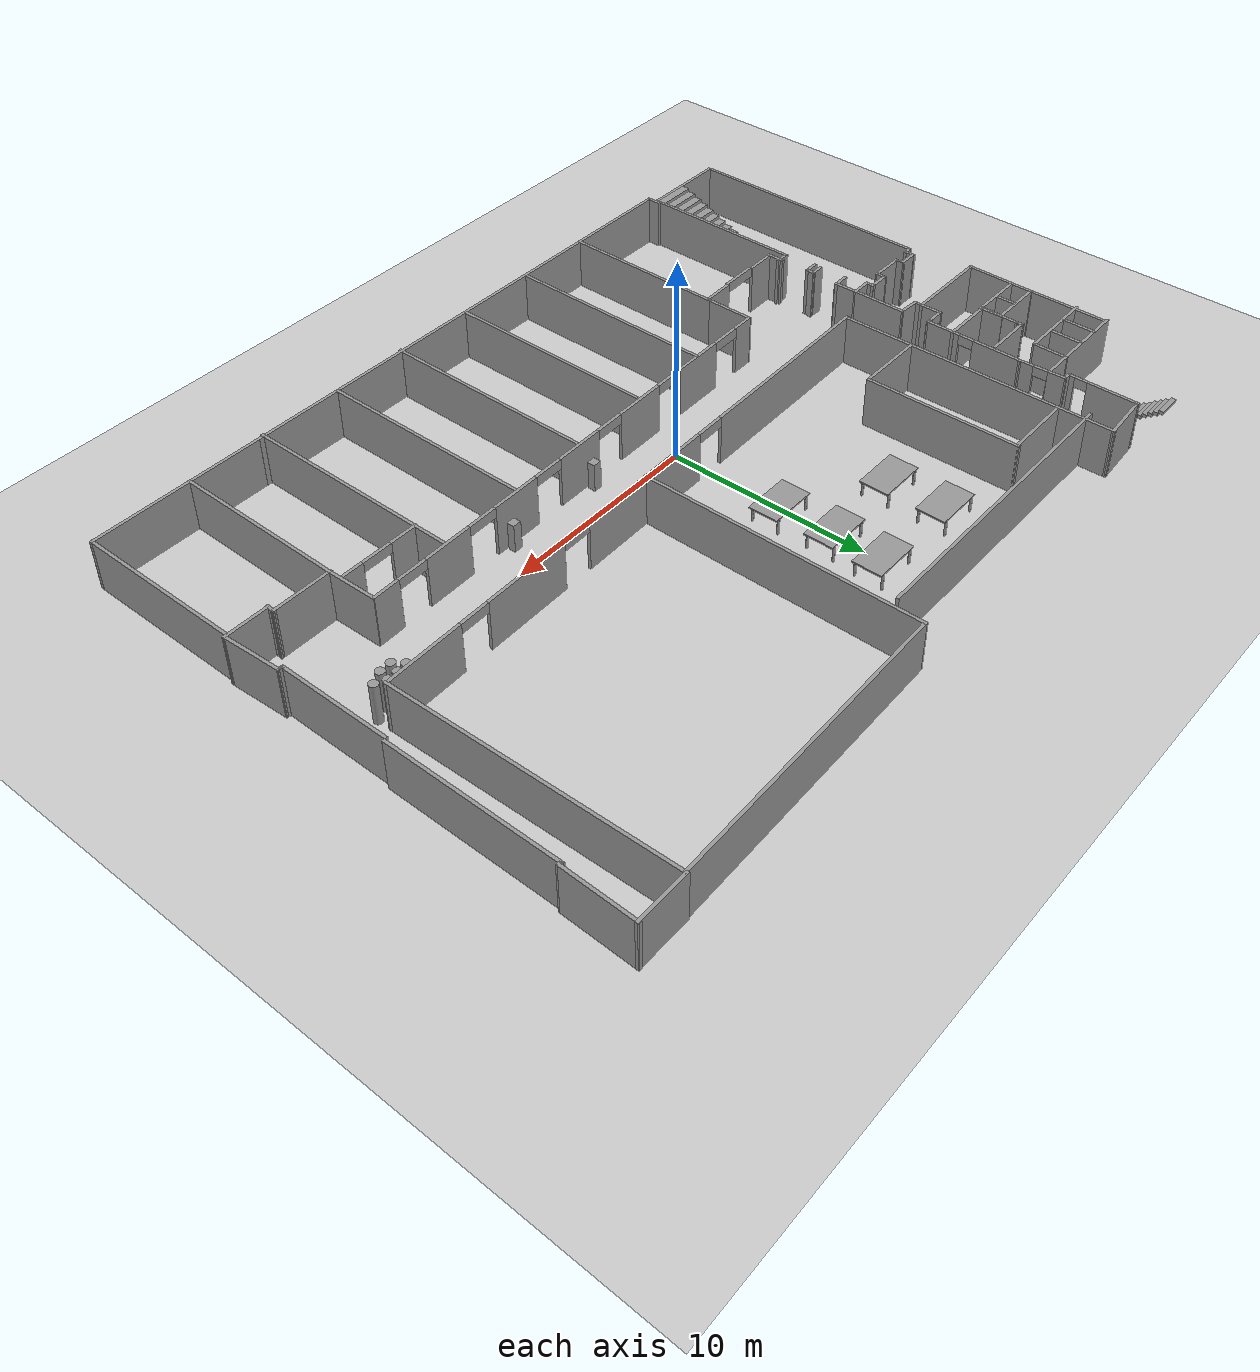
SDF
<sdf version="1.6">
 <world name="default">
  <light name="sun" type="directional">
   <pose>0 0 10 0 -0 0</pose>
   <diffuse>0.8 0.8 0.8 1</diffuse>
   <specular>0.2 0.2 0.2 1</specular>
   <attenuation>
    <range>1000</range>
    <constant>0.9</constant>
    <linear>0.01</linear>
    <quadratic>0.001</quadratic>
   </attenuation>
   <direction>-0.5 0.1 -0.9</direction>
  </light>
  <model name="ground_plane">
   <static>1</static>
   <link name="link">
    <collision name="collision">
     <geometry><plane><normal>0 0 1</normal><size>100 100</size></plane></geometry>
     <surface>
      <contact><collide_bitmask>65535</collide_bitmask></contact>
      <friction><ode><mu>100</mu><mu2>50</mu2></ode></friction>
     </surface>
    </collision>
    <visual name="visual">
     <cast_shadows>0</cast_shadows>
     <geometry><plane><normal>0 0 1</normal><size>100 100</size></plane></geometry>
     <material>
      <script><uri>file://media/materials/scripts/gazebo.material</uri><name>Gazebo/Grey</name></script>
     </material>
    </visual>
   </link>
  </model>
  <gravity>0 0 -9.8</gravity>
  <magnetic_field>6e-06 2.3e-05 -4.2e-05</magnetic_field>
  <atmosphere type="adiabatic"/>
  <physics name="default_physics" default="0" type="ode">
   <max_step_size>0.01</max_step_size>
   <real_time_factor>1</real_time_factor>
   <real_time_update_rate>100</real_time_update_rate>
  </physics>
  <scene><ambient>0.4 0.4 0.4 1</ambient><background>0.7 0.7 0.7 1</background><shadows>1</shadows></scene>
  <audio><device>default</device></audio>
  <spherical_coordinates>
   <surface_model>EARTH_WGS84</surface_model>
   <latitude_deg>0</latitude_deg>
   <longitude_deg>0</longitude_deg>
   <elevation>0</elevation>
   <heading_deg>0</heading_deg>
  </spherical_coordinates>
  <model name="six_floor">
   <link name="Stairs_0">
    <visual name="Stairs_0_Visual_1">
     <pose>-15.7467 -8.23125 0.25 0 -0 0</pose>
     <geometry><box><size>1.9122 0.405242 0.166667</size></box></geometry>
     <material>
      <script><uri>file://media/materials/scripts/gazebo.material</uri><name>Gazebo/Grey</name></script>
      <ambient>1 1 1 1</ambient>
     </material>
     <meta><layer>0</layer></meta>
    </visual>
    <visual name="Stairs_0_Visual_0">
     <pose>-15.7467 -7.82601 0.083333 0 -0 0</pose>
     <geometry><box><size>1.9122 0.405242 0.166667</size></box></geometry>
     <material>
      <script><uri>file://media/materials/scripts/gazebo.material</uri><name>Gazebo/Grey</name></script>
      <ambient>1 1 1 1</ambient>
     </material>
     <meta><layer>0</layer></meta>
    </visual>
    <visual name="Stairs_0_Visual_2">
     <pose>-15.7467 -8.63649 0.416667 0 -0 0</pose>
     <geometry><box><size>1.9122 0.405242 0.166667</size></box></geometry>
     <material>
      <script><uri>file://media/materials/scripts/gazebo.material</uri><name>Gazebo/Grey</name></script>
      <ambient>1 1 1 1</ambient>
     </material>
     <meta><layer>0</layer></meta>
    </visual>
    <visual name="Stairs_0_Visual_3">
     <pose>-15.7467 -9.04173 0.583333 0 -0 0</pose>
     <geometry><box><size>1.9122 0.405242 0.166667</size></box></geometry>
     <material>
      <script><uri>file://media/materials/scripts/gazebo.material</uri><name>Gazebo/Grey</name></script>
      <ambient>1 1 1 1</ambient>
     </material>
     <meta><layer>0</layer></meta>
    </visual>
    <visual name="Stairs_0_Visual_4">
     <pose>-15.7467 -9.44697 0.75 0 -0 0</pose>
     <geometry><box><size>1.9122 0.405242 0.166667</size></box></geometry>
     <material>
      <script><uri>file://media/materials/scripts/gazebo.material</uri><name>Gazebo/Grey</name></script>
      <ambient>1 1 1 1</ambient>
     </material>
     <meta><layer>0</layer></meta>
    </visual>
    <visual name="Stairs_0_Visual_5">
     <pose>-15.7467 -9.85222 0.916667 0 -0 0</pose>
     <geometry><box><size>1.9122 0.405242 0.166667</size></box></geometry>
     <material>
      <script><uri>file://media/materials/scripts/gazebo.material</uri><name>Gazebo/Grey</name></script>
      <ambient>1 1 1 1</ambient>
     </material>
     <meta><layer>0</layer></meta>
    </visual>
    <visual name="Stairs_0_Visual_6">
     <pose>-15.7467 -10.2575 1.08333 0 -0 0</pose>
     <geometry><box><size>1.9122 0.405242 0.166667</size></box></geometry>
     <material>
      <script><uri>file://media/materials/scripts/gazebo.material</uri><name>Gazebo/Grey</name></script>
      <ambient>1 1 1 1</ambient>
     </material>
     <meta><layer>0</layer></meta>
    </visual>
    <visual name="Stairs_0_Visual_7">
     <pose>-15.7467 -10.6627 1.25 0 -0 0</pose>
     <geometry><box><size>1.9122 0.405242 0.166667</size></box></geometry>
     <material>
      <script><uri>file://media/materials/scripts/gazebo.material</uri><name>Gazebo/Grey</name></script>
      <ambient>1 1 1 1</ambient>
     </material>
     <meta><layer>0</layer></meta>
    </visual>
    <visual name="Stairs_0_Visual_8">
     <pose>-15.7467 -11.0679 1.41667 0 -0 0</pose>
     <geometry><box><size>1.9122 0.405242 0.166667</size></box></geometry>
     <material>
      <script><uri>file://media/materials/scripts/gazebo.material</uri><name>Gazebo/Grey</name></script>
      <ambient>1 1 1 1</ambient>
     </material>
     <meta><layer>0</layer></meta>
    </visual>
    <visual name="Stairs_0_Visual_9">
     <pose>-15.7467 -11.4732 1.58333 0 -0 0</pose>
     <geometry><box><size>1.9122 0.405242 0.166667</size></box></geometry>
     <material>
      <script><uri>file://media/materials/scripts/gazebo.material</uri><name>Gazebo/Grey</name></script>
      <ambient>1 1 1 1</ambient>
     </material>
     <meta><layer>0</layer></meta>
    </visual>
    <visual name="Stairs_0_Visual_10">
     <pose>-15.7467 -11.8784 1.75 0 -0 0</pose>
     <geometry><box><size>1.9122 0.405242 0.166667</size></box></geometry>
     <material>
      <script><uri>file://media/materials/scripts/gazebo.material</uri><name>Gazebo/Grey</name></script>
      <ambient>1 1 1 1</ambient>
     </material>
     <meta><layer>0</layer></meta>
    </visual>
    <visual name="Stairs_0_Visual_11">
     <pose>-15.7467 -12.2837 1.91667 0 -0 0</pose>
     <geometry><box><size>1.9122 0.405242 0.166667</size></box></geometry>
     <material>
      <script><uri>file://media/materials/scripts/gazebo.material</uri><name>Gazebo/Grey</name></script>
      <ambient>1 1 1 1</ambient>
     </material>
     <meta><layer>0</layer></meta>
    </visual>
    <visual name="Stairs_0_Visual_12">
     <pose>-15.7467 -12.6889 2.08333 0 -0 0</pose>
     <geometry><box><size>1.9122 0.405242 0.166667</size></box></geometry>
     <material>
      <script><uri>file://media/materials/scripts/gazebo.material</uri><name>Gazebo/Grey</name></script>
      <ambient>1 1 1 1</ambient>
     </material>
     <meta><layer>0</layer></meta>
    </visual>
    <visual name="Stairs_0_Visual_13">
     <pose>-15.7467 -13.0942 2.25 0 -0 0</pose>
     <geometry><box><size>1.9122 0.405242 0.166667</size></box></geometry>
     <material>
      <script><uri>file://media/materials/scripts/gazebo.material</uri><name>Gazebo/Grey</name></script>
      <ambient>1 1 1 1</ambient>
     </material>
     <meta><layer>0</layer></meta>
    </visual>
    <visual name="Stairs_0_Visual_14">
     <pose>-15.7467 -13.4994 2.41667 0 -0 0</pose>
     <geometry><box><size>1.9122 0.405242 0.166667</size></box></geometry>
     <material>
      <script><uri>file://media/materials/scripts/gazebo.material</uri><name>Gazebo/Grey</name></script>
      <ambient>1 1 1 1</ambient>
     </material>
     <meta><layer>0</layer></meta>
    </visual>
    <collision name="Stairs_0_Collision_1">
     <pose>-15.7467 -8.23125 0.25 0 -0 0</pose>
     <geometry><box><size>1.9122 0.405242 0.166667</size></box></geometry>
     <surface>
      <friction>
       <ode><mu>1</mu><mu2>1</mu2><fdir1>0 0 0</fdir1><slip1>0</slip1><slip2>0</slip2></ode>
       <torsional>
        <coefficient>1</coefficient>
        <patch_radius>0</patch_radius>
        <surface_radius>0</surface_radius>
        <use_patch_radius>1</use_patch_radius>
        <ode><slip>0</slip></ode>
       </torsional>
      </friction>
      <bounce><restitution_coefficient>0</restitution_coefficient><threshold>1e+06</threshold></bounce>
      <contact>
       <collide_without_contact>0</collide_without_contact>
       <collide_without_contact_bitmask>1</collide_without_contact_bitmask>
       <collide_bitmask>1</collide_bitmask>
       <ode>
        <soft_cfm>0</soft_cfm>
        <soft_erp>0.2</soft_erp>
        <kp>1e+13</kp>
        <kd>1</kd>
        <max_vel>0.01</max_vel>
        <min_depth>0</min_depth>
       </ode>
       <bullet>
        <split_impulse>1</split_impulse>
        <split_impulse_penetration_threshold>-0.01</split_impulse_penetration_threshold>
        <soft_cfm>0</soft_cfm>
        <soft_erp>0.2</soft_erp>
        <kp>1e+13</kp>
        <kd>1</kd>
       </bullet>
      </contact>
     </surface>
    </collision>
    <collision name="Stairs_0_Collision_0">
     <pose>-15.7467 -7.82601 0.083333 0 -0 0</pose>
     <geometry><box><size>1.9122 0.405242 0.166667</size></box></geometry>
     <surface>
      <friction>
       <ode><mu>1</mu><mu2>1</mu2><fdir1>0 0 0</fdir1><slip1>0</slip1><slip2>0</slip2></ode>
       <torsional>
        <coefficient>1</coefficient>
        <patch_radius>0</patch_radius>
        <surface_radius>0</surface_radius>
        <use_patch_radius>1</use_patch_radius>
        <ode><slip>0</slip></ode>
       </torsional>
      </friction>
      <bounce><restitution_coefficient>0</restitution_coefficient><threshold>1e+06</threshold></bounce>
      <contact>
       <collide_without_contact>0</collide_without_contact>
       <collide_without_contact_bitmask>1</collide_without_contact_bitmask>
       <collide_bitmask>1</collide_bitmask>
       <ode>
        <soft_cfm>0</soft_cfm>
        <soft_erp>0.2</soft_erp>
        <kp>1e+13</kp>
        <kd>1</kd>
        <max_vel>0.01</max_vel>
        <min_depth>0</min_depth>
       </ode>
       <bullet>
        <split_impulse>1</split_impulse>
        <split_impulse_penetration_threshold>-0.01</split_impulse_penetration_threshold>
        <soft_cfm>0</soft_cfm>
        <soft_erp>0.2</soft_erp>
        <kp>1e+13</kp>
        <kd>1</kd>
       </bullet>
      </contact>
     </surface>
    </collision>
    <collision name="Stairs_0_Collision_3">
     <pose>-15.7467 -9.04173 0.583333 0 -0 0</pose>
     <geometry><box><size>1.9122 0.405242 0.166667</size></box></geometry>
     <surface>
      <friction>
       <ode><mu>1</mu><mu2>1</mu2><fdir1>0 0 0</fdir1><slip1>0</slip1><slip2>0</slip2></ode>
       <torsional>
        <coefficient>1</coefficient>
        <patch_radius>0</patch_radius>
        <surface_radius>0</surface_radius>
        <use_patch_radius>1</use_patch_radius>
        <ode><slip>0</slip></ode>
       </torsional>
      </friction>
      <bounce><restitution_coefficient>0</restitution_coefficient><threshold>1e+06</threshold></bounce>
      <contact>
       <collide_without_contact>0</collide_without_contact>
       <collide_without_contact_bitmask>1</collide_without_contact_bitmask>
       <collide_bitmask>1</collide_bitmask>
       <ode>
        <soft_cfm>0</soft_cfm>
        <soft_erp>0.2</soft_erp>
        <kp>1e+13</kp>
        <kd>1</kd>
        <max_vel>0.01</max_vel>
        <min_depth>0</min_depth>
       </ode>
       <bullet>
        <split_impulse>1</split_impulse>
        <split_impulse_penetration_threshold>-0.01</split_impulse_penetration_threshold>
        <soft_cfm>0</soft_cfm>
        <soft_erp>0.2</soft_erp>
        <kp>1e+13</kp>
        <kd>1</kd>
       </bullet>
      </contact>
     </surface>
    </collision>
    <collision name="Stairs_0_Collision_2">
     <pose>-15.7467 -8.63649 0.416667 0 -0 0</pose>
     <geometry><box><size>1.9122 0.405242 0.166667</size></box></geometry>
     <surface>
      <friction>
       <ode><mu>1</mu><mu2>1</mu2><fdir1>0 0 0</fdir1><slip1>0</slip1><slip2>0</slip2></ode>
       <torsional>
        <coefficient>1</coefficient>
        <patch_radius>0</patch_radius>
        <surface_radius>0</surface_radius>
        <use_patch_radius>1</use_patch_radius>
        <ode><slip>0</slip></ode>
       </torsional>
      </friction>
      <bounce><restitution_coefficient>0</restitution_coefficient><threshold>1e+06</threshold></bounce>
      <contact>
       <collide_without_contact>0</collide_without_contact>
       <collide_without_contact_bitmask>1</collide_without_contact_bitmask>
       <collide_bitmask>1</collide_bitmask>
       <ode>
        <soft_cfm>0</soft_cfm>
        <soft_erp>0.2</soft_erp>
        <kp>1e+13</kp>
        <kd>1</kd>
        <max_vel>0.01</max_vel>
        <min_depth>0</min_depth>
       </ode>
       <bullet>
        <split_impulse>1</split_impulse>
        <split_impulse_penetration_threshold>-0.01</split_impulse_penetration_threshold>
        <soft_cfm>0</soft_cfm>
        <soft_erp>0.2</soft_erp>
        <kp>1e+13</kp>
        <kd>1</kd>
       </bullet>
      </contact>
     </surface>
    </collision>
    <collision name="Stairs_0_Collision_4">
     <pose>-15.7467 -9.44697 0.75 0 -0 0</pose>
     <geometry><box><size>1.9122 0.405242 0.166667</size></box></geometry>
     <surface>
      <friction>
       <ode><mu>1</mu><mu2>1</mu2><fdir1>0 0 0</fdir1><slip1>0</slip1><slip2>0</slip2></ode>
       <torsional>
        <coefficient>1</coefficient>
        <patch_radius>0</patch_radius>
        <surface_radius>0</surface_radius>
        <use_patch_radius>1</use_patch_radius>
        <ode><slip>0</slip></ode>
       </torsional>
      </friction>
      <bounce><restitution_coefficient>0</restitution_coefficient><threshold>1e+06</threshold></bounce>
      <contact>
       <collide_without_contact>0</collide_without_contact>
       <collide_without_contact_bitmask>1</collide_without_contact_bitmask>
       <collide_bitmask>1</collide_bitmask>
       <ode>
        <soft_cfm>0</soft_cfm>
        <soft_erp>0.2</soft_erp>
        <kp>1e+13</kp>
        <kd>1</kd>
        <max_vel>0.01</max_vel>
        <min_depth>0</min_depth>
       </ode>
       <bullet>
        <split_impulse>1</split_impulse>
        <split_impulse_penetration_threshold>-0.01</split_impulse_penetration_threshold>
        <soft_cfm>0</soft_cfm>
        <soft_erp>0.2</soft_erp>
        <kp>1e+13</kp>
        <kd>1</kd>
       </bullet>
      </contact>
     </surface>
    </collision>
    <collision name="Stairs_0_Collision_7">
     <pose>-15.7467 -10.6627 1.25 0 -0 0</pose>
     <geometry><box><size>1.9122 0.405242 0.166667</size></box></geometry>
     <surface>
      <friction>
       <ode><mu>1</mu><mu2>1</mu2><fdir1>0 0 0</fdir1><slip1>0</slip1><slip2>0</slip2></ode>
       <torsional>
        <coefficient>1</coefficient>
        <patch_radius>0</patch_radius>
        <surface_radius>0</surface_radius>
        <use_patch_radius>1</use_patch_radius>
        <ode><slip>0</slip></ode>
       </torsional>
      </friction>
      <bounce><restitution_coefficient>0</restitution_coefficient><threshold>1e+06</threshold></bounce>
      <contact>
       <collide_without_contact>0</collide_without_contact>
       <collide_without_contact_bitmask>1</collide_without_contact_bitmask>
       <collide_bitmask>1</collide_bitmask>
       <ode>
        <soft_cfm>0</soft_cfm>
        <soft_erp>0.2</soft_erp>
        <kp>1e+13</kp>
        <kd>1</kd>
        <max_vel>0.01</max_vel>
        <min_depth>0</min_depth>
       </ode>
       <bullet>
        <split_impulse>1</split_impulse>
        <split_impulse_penetration_threshold>-0.01</split_impulse_penetration_threshold>
        <soft_cfm>0</soft_cfm>
        <soft_erp>0.2</soft_erp>
        <kp>1e+13</kp>
        <kd>1</kd>
       </bullet>
      </contact>
     </surface>
    </collision>
    <collision name="Stairs_0_Collision_5">
     <pose>-15.7467 -9.85222 0.916667 0 -0 0</pose>
     <geometry><box><size>1.9122 0.405242 0.166667</size></box></geometry>
     <surface>
      <friction>
       <ode><mu>1</mu><mu2>1</mu2><fdir1>0 0 0</fdir1><slip1>0</slip1><slip2>0</slip2></ode>
       <torsional>
        <coefficient>1</coefficient>
        <patch_radius>0</patch_radius>
        <surface_radius>0</surface_radius>
        <use_patch_radius>1</use_patch_radius>
        <ode><slip>0</slip></ode>
       </torsional>
      </friction>
      <bounce><restitution_coefficient>0</restitution_coefficient><threshold>1e+06</threshold></bounce>
      <contact>
       <collide_without_contact>0</collide_without_contact>
       <collide_without_contact_bitmask>1</collide_without_contact_bitmask>
       <collide_bitmask>1</collide_bitmask>
       <ode>
        <soft_cfm>0</soft_cfm>
        <soft_erp>0.2</soft_erp>
        <kp>1e+13</kp>
        <kd>1</kd>
        <max_vel>0.01</max_vel>
        <min_depth>0</min_depth>
       </ode>
       <bullet>
        <split_impulse>1</split_impulse>
        <split_impulse_penetration_threshold>-0.01</split_impulse_penetration_threshold>
        <soft_cfm>0</soft_cfm>
        <soft_erp>0.2</soft_erp>
        <kp>1e+13</kp>
        <kd>1</kd>
       </bullet>
      </contact>
     </surface>
    </collision>
    <collision name="Stairs_0_Collision_6">
     <pose>-15.7467 -10.2575 1.08333 0 -0 0</pose>
     <geometry><box><size>1.9122 0.405242 0.166667</size></box></geometry>
     <surface>
      <friction>
       <ode><mu>1</mu><mu2>1</mu2><fdir1>0 0 0</fdir1><slip1>0</slip1><slip2>0</slip2></ode>
       <torsional>
        <coefficient>1</coefficient>
        <patch_radius>0</patch_radius>
        <surface_radius>0</surface_radius>
        <use_patch_radius>1</use_patch_radius>
        <ode><slip>0</slip></ode>
       </torsional>
      </friction>
      <bounce><restitution_coefficient>0</restitution_coefficient><threshold>1e+06</threshold></bounce>
      <contact>
       <collide_without_contact>0</collide_without_contact>
       <collide_without_contact_bitmask>1</collide_without_contact_bitmask>
       <collide_bitmask>1</collide_bitmask>
       <ode>
        <soft_cfm>0</soft_cfm>
        <soft_erp>0.2</soft_erp>
        <kp>1e+13</kp>
        <kd>1</kd>
        <max_vel>0.01</max_vel>
        <min_depth>0</min_depth>
       </ode>
       <bullet>
        <split_impulse>1</split_impulse>
        <split_impulse_penetration_threshold>-0.01</split_impulse_penetration_threshold>
        <soft_cfm>0</soft_cfm>
        <soft_erp>0.2</soft_erp>
        <kp>1e+13</kp>
        <kd>1</kd>
       </bullet>
      </contact>
     </surface>
    </collision>
    <collision name="Stairs_0_Collision_8">
     <pose>-15.7467 -11.0679 1.41667 0 -0 0</pose>
     <geometry><box><size>1.9122 0.405242 0.166667</size></box></geometry>
     <surface>
      <friction>
       <ode><mu>1</mu><mu2>1</mu2><fdir1>0 0 0</fdir1><slip1>0</slip1><slip2>0</slip2></ode>
       <torsional>
        <coefficient>1</coefficient>
        <patch_radius>0</patch_radius>
        <surface_radius>0</surface_radius>
        <use_patch_radius>1</use_patch_radius>
        <ode><slip>0</slip></ode>
       </torsional>
      </friction>
      <bounce><restitution_coefficient>0</restitution_coefficient><threshold>1e+06</threshold></bounce>
      <contact>
       <collide_without_contact>0</collide_without_contact>
       <collide_without_contact_bitmask>1</collide_without_contact_bitmask>
       <collide_bitmask>1</collide_bitmask>
       <ode>
        <soft_cfm>0</soft_cfm>
        <soft_erp>0.2</soft_erp>
        <kp>1e+13</kp>
        <kd>1</kd>
        <max_vel>0.01</max_vel>
        <min_depth>0</min_depth>
       </ode>
       <bullet>
        <split_impulse>1</split_impulse>
        <split_impulse_penetration_threshold>-0.01</split_impulse_penetration_threshold>
        <soft_cfm>0</soft_cfm>
        <soft_erp>0.2</soft_erp>
        <kp>1e+13</kp>
        <kd>1</kd>
       </bullet>
      </contact>
     </surface>
    </collision>
    <collision name="Stairs_0_Collision_9">
     <pose>-15.7467 -11.4732 1.58333 0 -0 0</pose>
     <geometry><box><size>1.9122 0.405242 0.166667</size></box></geometry>
     <surface>
      <friction>
       <ode><mu>1</mu><mu2>1</mu2><fdir1>0 0 0</fdir1><slip1>0</slip1><slip2>0</slip2></ode>
       <torsional>
        <coefficient>1</coefficient>
        <patch_radius>0</patch_radius>
        <surface_radius>0</surface_radius>
        <use_patch_radius>1</use_patch_radius>
        <ode><slip>0</slip></ode>
       </torsional>
      </friction>
      <bounce><restitution_coefficient>0</restitution_coefficient><threshold>1e+06</threshold></bounce>
      <contact>
       <collide_without_contact>0</collide_without_contact>
       <collide_without_contact_bitmask>1</collide_without_contact_bitmask>
       <collide_bitmask>1</collide_bitmask>
       <ode>
        <soft_cfm>0</soft_cfm>
        <soft_erp>0.2</soft_erp>
        <kp>1e+13</kp>
        <kd>1</kd>
        <max_vel>0.01</max_vel>
        <min_depth>0</min_depth>
       </ode>
       <bullet>
        <split_impulse>1</split_impulse>
        <split_impulse_penetration_threshold>-0.01</split_impulse_penetration_threshold>
        <soft_cfm>0</soft_cfm>
        <soft_erp>0.2</soft_erp>
        <kp>1e+13</kp>
        <kd>1</kd>
       </bullet>
      </contact>
     </surface>
    </collision>
    <collision name="Stairs_0_Collision_10">
     <pose>-15.7467 -11.8784 1.75 0 -0 0</pose>
     <geometry><box><size>1.9122 0.405242 0.166667</size></box></geometry>
     <surface>
      <friction>
       <ode><mu>1</mu><mu2>1</mu2><fdir1>0 0 0</fdir1><slip1>0</slip1><slip2>0</slip2></ode>
       <torsional>
        <coefficient>1</coefficient>
        <patch_radius>0</patch_radius>
        <surface_radius>0</surface_radius>
        <use_patch_radius>1</use_patch_radius>
        <ode><slip>0</slip></ode>
       </torsional>
      </friction>
      <bounce><restitution_coefficient>0</restitution_coefficient><threshold>1e+06</threshold></bounce>
      <contact>
       <collide_without_contact>0</collide_without_contact>
       <collide_without_contact_bitmask>1</collide_without_contact_bitmask>
       <collide_bitmask>1</collide_bitmask>
       <ode>
        <soft_cfm>0</soft_cfm>
        <soft_erp>0.2</soft_erp>
        <kp>1e+13</kp>
        <kd>1</kd>
        <max_vel>0.01</max_vel>
        <min_depth>0</min_depth>
       </ode>
       <bullet>
        <split_impulse>1</split_impulse>
        <split_impulse_penetration_threshold>-0.01</split_impulse_penetration_threshold>
        <soft_cfm>0</soft_cfm>
        <soft_erp>0.2</soft_erp>
        <kp>1e+13</kp>
        <kd>1</kd>
       </bullet>
      </contact>
     </surface>
    </collision>
    <collision name="Stairs_0_Collision_11">
     <pose>-15.7467 -12.2837 1.91667 0 -0 0</pose>
     <geometry><box><size>1.9122 0.405242 0.166667</size></box></geometry>
     <surface>
      <friction>
       <ode><mu>1</mu><mu2>1</mu2><fdir1>0 0 0</fdir1><slip1>0</slip1><slip2>0</slip2></ode>
       <torsional>
        <coefficient>1</coefficient>
        <patch_radius>0</patch_radius>
        <surface_radius>0</surface_radius>
        <use_patch_radius>1</use_patch_radius>
        <ode><slip>0</slip></ode>
       </torsional>
      </friction>
      <bounce><restitution_coefficient>0</restitution_coefficient><threshold>1e+06</threshold></bounce>
      <contact>
       <collide_without_contact>0</collide_without_contact>
       <collide_without_contact_bitmask>1</collide_without_contact_bitmask>
       <collide_bitmask>1</collide_bitmask>
       <ode>
        <soft_cfm>0</soft_cfm>
        <soft_erp>0.2</soft_erp>
        <kp>1e+13</kp>
        <kd>1</kd>
        <max_vel>0.01</max_vel>
        <min_depth>0</min_depth>
       </ode>
       <bullet>
        <split_impulse>1</split_impulse>
        <split_impulse_penetration_threshold>-0.01</split_impulse_penetration_threshold>
        <soft_cfm>0</soft_cfm>
        <soft_erp>0.2</soft_erp>
        <kp>1e+13</kp>
        <kd>1</kd>
       </bullet>
      </contact>
     </surface>
    </collision>
    <collision name="Stairs_0_Collision_12">
     <pose>-15.7467 -12.6889 2.08333 0 -0 0</pose>
     <geometry><box><size>1.9122 0.405242 0.166667</size></box></geometry>
     <surface>
      <friction>
       <ode><mu>1</mu><mu2>1</mu2><fdir1>0 0 0</fdir1><slip1>0</slip1><slip2>0</slip2></ode>
       <torsional>
        <coefficient>1</coefficient>
        <patch_radius>0</patch_radius>
        <surface_radius>0</surface_radius>
        <use_patch_radius>1</use_patch_radius>
        <ode><slip>0</slip></ode>
       </torsional>
      </friction>
      <bounce><restitution_coefficient>0</restitution_coefficient><threshold>1e+06</threshold></bounce>
      <contact>
       <collide_without_contact>0</collide_without_contact>
       <collide_without_contact_bitmask>1</collide_without_contact_bitmask>
       <collide_bitmask>1</collide_bitmask>
       <ode>
        <soft_cfm>0</soft_cfm>
        <soft_erp>0.2</soft_erp>
        <kp>1e+13</kp>
        <kd>1</kd>
        <max_vel>0.01</max_vel>
        <min_depth>0</min_depth>
       </ode>
       <bullet>
        <split_impulse>1</split_impulse>
        <split_impulse_penetration_threshold>-0.01</split_impulse_penetration_threshold>
        <soft_cfm>0</soft_cfm>
        <soft_erp>0.2</soft_erp>
        <kp>1e+13</kp>
        <kd>1</kd>
       </bullet>
      </contact>
     </surface>
    </collision>
    <collision name="Stairs_0_Collision_13">
     <pose>-15.7467 -13.0942 2.25 0 -0 0</pose>
     <geometry><box><size>1.9122 0.405242 0.166667</size></box></geometry>
     <surface>
      <friction>
       <ode><mu>1</mu><mu2>1</mu2><fdir1>0 0 0</fdir1><slip1>0</slip1><slip2>0</slip2></ode>
       <torsional>
        <coefficient>1</coefficient>
        <patch_radius>0</patch_radius>
        <surface_radius>0</surface_radius>
        <use_patch_radius>1</use_patch_radius>
        <ode><slip>0</slip></ode>
       </torsional>
      </friction>
      <bounce><restitution_coefficient>0</restitution_coefficient><threshold>1e+06</threshold></bounce>
      <contact>
       <collide_without_contact>0</collide_without_contact>
       <collide_without_contact_bitmask>1</collide_without_contact_bitmask>
       <collide_bitmask>1</collide_bitmask>
       <ode>
        <soft_cfm>0</soft_cfm>
        <soft_erp>0.2</soft_erp>
        <kp>1e+13</kp>
        <kd>1</kd>
        <max_vel>0.01</max_vel>
        <min_depth>0</min_depth>
       </ode>
       <bullet>
        <split_impulse>1</split_impulse>
        <split_impulse_penetration_threshold>-0.01</split_impulse_penetration_threshold>
        <soft_cfm>0</soft_cfm>
        <soft_erp>0.2</soft_erp>
        <kp>1e+13</kp>
        <kd>1</kd>
       </bullet>
      </contact>
     </surface>
    </collision>
    <collision name="Stairs_0_Collision_14">
     <pose>-15.7467 -13.4994 2.41667 0 -0 0</pose>
     <geometry><box><size>1.9122 0.405242 0.166667</size></box></geometry>
     <surface>
      <friction>
       <ode><mu>1</mu><mu2>1</mu2><fdir1>0 0 0</fdir1><slip1>0</slip1><slip2>0</slip2></ode>
       <torsional>
        <coefficient>1</coefficient>
        <patch_radius>0</patch_radius>
        <surface_radius>0</surface_radius>
        <use_patch_radius>1</use_patch_radius>
        <ode><slip>0</slip></ode>
       </torsional>
      </friction>
      <bounce><restitution_coefficient>0</restitution_coefficient><threshold>1e+06</threshold></bounce>
      <contact>
       <collide_without_contact>0</collide_without_contact>
       <collide_without_contact_bitmask>1</collide_without_contact_bitmask>
       <collide_bitmask>1</collide_bitmask>
       <ode>
        <soft_cfm>0</soft_cfm>
        <soft_erp>0.2</soft_erp>
        <kp>1e+13</kp>
        <kd>1</kd>
        <max_vel>0.01</max_vel>
        <min_depth>0</min_depth>
       </ode>
       <bullet>
        <split_impulse>1</split_impulse>
        <split_impulse_penetration_threshold>-0.01</split_impulse_penetration_threshold>
        <soft_cfm>0</soft_cfm>
        <soft_erp>0.2</soft_erp>
        <kp>1e+13</kp>
        <kd>1</kd>
       </bullet>
      </contact>
     </surface>
    </collision>
   </link>
   <link name="Stairs_1">
    <visual name="Stairs_1_Visual_4">
     <pose>-15.4859 11.9319 0.75 0 -0 -3.14159</pose>
     <geometry><box><size>1.18504 0.233333 0.166667</size></box></geometry>
     <material>
      <script><uri>file://media/materials/scripts/gazebo.material</uri><name>Gazebo/Grey</name></script>
      <ambient>1 1 1 1</ambient>
     </material>
     <meta><layer>0</layer></meta>
    </visual>
    <visual name="Stairs_1_Visual_0">
     <pose>-15.4859 10.9986 0.083333 0 -0 -3.14159</pose>
     <geometry><box><size>1.18504 0.233333 0.166667</size></box></geometry>
     <material>
      <script><uri>file://media/materials/scripts/gazebo.material</uri><name>Gazebo/Grey</name></script>
      <ambient>1 1 1 1</ambient>
     </material>
     <meta><layer>0</layer></meta>
    </visual>
    <visual name="Stairs_1_Visual_1">
     <pose>-15.4859 11.2319 0.25 0 -0 -3.14159</pose>
     <geometry><box><size>1.18504 0.233333 0.166667</size></box></geometry>
     <material>
      <script><uri>file://media/materials/scripts/gazebo.material</uri><name>Gazebo/Grey</name></script>
      <ambient>1 1 1 1</ambient>
     </material>
     <meta><layer>0</layer></meta>
    </visual>
    <visual name="Stairs_1_Visual_2">
     <pose>-15.4859 11.4653 0.416667 0 -0 -3.14159</pose>
     <geometry><box><size>1.18504 0.233333 0.166667</size></box></geometry>
     <material>
      <script><uri>file://media/materials/scripts/gazebo.material</uri><name>Gazebo/Grey</name></script>
      <ambient>1 1 1 1</ambient>
     </material>
     <meta><layer>0</layer></meta>
    </visual>
    <visual name="Stairs_1_Visual_3">
     <pose>-15.4859 11.6986 0.583333 0 -0 -3.14159</pose>
     <geometry><box><size>1.18504 0.233333 0.166667</size></box></geometry>
     <material>
      <script><uri>file://media/materials/scripts/gazebo.material</uri><name>Gazebo/Grey</name></script>
      <ambient>1 1 1 1</ambient>
     </material>
     <meta><layer>0</layer></meta>
    </visual>
    <visual name="Stairs_1_Visual_5">
     <pose>-15.4859 12.1653 0.916667 0 -0 -3.14159</pose>
     <geometry><box><size>1.18504 0.233333 0.166667</size></box></geometry>
     <material>
      <script><uri>file://media/materials/scripts/gazebo.material</uri><name>Gazebo/Grey</name></script>
      <ambient>1 1 1 1</ambient>
     </material>
     <meta><layer>0</layer></meta>
    </visual>
    <visual name="Stairs_1_Visual_6">
     <pose>-15.4859 12.3986 1.08333 0 -0 -3.14159</pose>
     <geometry><box><size>1.18504 0.233333 0.166667</size></box></geometry>
     <material>
      <script><uri>file://media/materials/scripts/gazebo.material</uri><name>Gazebo/Grey</name></script>
      <ambient>1 1 1 1</ambient>
     </material>
     <meta><layer>0</layer></meta>
    </visual>
    <visual name="Stairs_1_Visual_7">
     <pose>-15.4859 12.6319 1.25 0 -0 -3.14159</pose>
     <geometry><box><size>1.18504 0.233333 0.166667</size></box></geometry>
     <material>
      <script><uri>file://media/materials/scripts/gazebo.material</uri><name>Gazebo/Grey</name></script>
      <ambient>1 1 1 1</ambient>
     </material>
     <meta><layer>0</layer></meta>
    </visual>
    <visual name="Stairs_1_Visual_8">
     <pose>-15.4859 12.8653 1.41667 0 -0 -3.14159</pose>
     <geometry><box><size>1.18504 0.233333 0.166667</size></box></geometry>
     <material>
      <script><uri>file://media/materials/scripts/gazebo.material</uri><name>Gazebo/Grey</name></script>
      <ambient>1 1 1 1</ambient>
     </material>
     <meta><layer>0</layer></meta>
    </visual>
    <visual name="Stairs_1_Visual_9">
     <pose>-15.4859 13.0986 1.58333 0 -0 -3.14159</pose>
     <geometry><box><size>1.18504 0.233333 0.166667</size></box></geometry>
     <material>
      <script><uri>file://media/materials/scripts/gazebo.material</uri><name>Gazebo/Grey</name></script>
      <ambient>1 1 1 1</ambient>
     </material>
     <meta><layer>0</layer></meta>
    </visual>
    <visual name="Stairs_1_Visual_10">
     <pose>-15.4859 13.3319 1.75 0 -0 -3.14159</pose>
     <geometry><box><size>1.18504 0.233333 0.166667</size></box></geometry>
     <material>
      <script><uri>file://media/materials/scripts/gazebo.material</uri><name>Gazebo/Grey</name></script>
      <ambient>1 1 1 1</ambient>
     </material>
     <meta><layer>0</layer></meta>
    </visual>
    <visual name="Stairs_1_Visual_11">
     <pose>-15.4859 13.5653 1.91667 0 -0 -3.14159</pose>
     <geometry><box><size>1.18504 0.233333 0.166667</size></box></geometry>
     <material>
      <script><uri>file://media/materials/scripts/gazebo.material</uri><name>Gazebo/Grey</name></script>
      <ambient>1 1 1 1</ambient>
     </material>
     <meta><layer>0</layer></meta>
    </visual>
    <visual name="Stairs_1_Visual_12">
     <pose>-15.4859 13.7986 2.08333 0 -0 -3.14159</pose>
     <geometry><box><size>1.18504 0.233333 0.166667</size></box></geometry>
     <material>
      <script><uri>file://media/materials/scripts/gazebo.material</uri><name>Gazebo/Grey</name></script>
      <ambient>1 1 1 1</ambient>
     </material>
     <meta><layer>0</layer></meta>
    </visual>
    <visual name="Stairs_1_Visual_13">
     <pose>-15.4859 14.0319 2.25 0 -0 -3.14159</pose>
     <geometry><box><size>1.18504 0.233333 0.166667</size></box></geometry>
     <material>
      <script><uri>file://media/materials/scripts/gazebo.material</uri><name>Gazebo/Grey</name></script>
      <ambient>1 1 1 1</ambient>
     </material>
     <meta><layer>0</layer></meta>
    </visual>
    <visual name="Stairs_1_Visual_14">
     <pose>-15.4859 14.2653 2.41667 0 -0 -3.14159</pose>
     <geometry><box><size>1.18504 0.233333 0.166667</size></box></geometry>
     <material>
      <script><uri>file://media/materials/scripts/gazebo.material</uri><name>Gazebo/Grey</name></script>
      <ambient>1 1 1 1</ambient>
     </material>
     <meta><layer>0</layer></meta>
    </visual>
    <collision name="Stairs_1_Collision_8">
     <pose>-15.4859 12.8653 1.41667 0 0 -3.14159</pose>
     <geometry><box><size>1.18504 0.233333 0.166667</size></box></geometry>
     <surface>
      <friction>
       <ode><mu>1</mu><mu2>1</mu2><fdir1>0 0 0</fdir1><slip1>0</slip1><slip2>0</slip2></ode>
       <torsional>
        <coefficient>1</coefficient>
        <patch_radius>0</patch_radius>
        <surface_radius>0</surface_radius>
        <use_patch_radius>1</use_patch_radius>
        <ode><slip>0</slip></ode>
       </torsional>
      </friction>
      <bounce><restitution_coefficient>0</restitution_coefficient><threshold>1e+06</threshold></bounce>
      <contact>
       <collide_without_contact>0</collide_without_contact>
       <collide_without_contact_bitmask>1</collide_without_contact_bitmask>
       <collide_bitmask>1</collide_bitmask>
       <ode>
        <soft_cfm>0</soft_cfm>
        <soft_erp>0.2</soft_erp>
        <kp>1e+13</kp>
        <kd>1</kd>
        <max_vel>0.01</max_vel>
        <min_depth>0</min_depth>
       </ode>
       <bullet>
        <split_impulse>1</split_impulse>
        <split_impulse_penetration_threshold>-0.01</split_impulse_penetration_threshold>
        <soft_cfm>0</soft_cfm>
        <soft_erp>0.2</soft_erp>
        <kp>1e+13</kp>
        <kd>1</kd>
       </bullet>
      </contact>
     </surface>
    </collision>
    <collision name="Stairs_1_Collision_0">
     <pose>-15.4859 10.9986 0.083333 0 0 -3.14159</pose>
     <geometry><box><size>1.18504 0.233333 0.166667</size></box></geometry>
     <surface>
      <friction>
       <ode><mu>1</mu><mu2>1</mu2><fdir1>0 0 0</fdir1><slip1>0</slip1><slip2>0</slip2></ode>
       <torsional>
        <coefficient>1</coefficient>
        <patch_radius>0</patch_radius>
        <surface_radius>0</surface_radius>
        <use_patch_radius>1</use_patch_radius>
        <ode><slip>0</slip></ode>
       </torsional>
      </friction>
      <bounce><restitution_coefficient>0</restitution_coefficient><threshold>1e+06</threshold></bounce>
      <contact>
       <collide_without_contact>0</collide_without_contact>
       <collide_without_contact_bitmask>1</collide_without_contact_bitmask>
       <collide_bitmask>1</collide_bitmask>
       <ode>
        <soft_cfm>0</soft_cfm>
        <soft_erp>0.2</soft_erp>
        <kp>1e+13</kp>
        <kd>1</kd>
        <max_vel>0.01</max_vel>
        <min_depth>0</min_depth>
       </ode>
       <bullet>
        <split_impulse>1</split_impulse>
        <split_impulse_penetration_threshold>-0.01</split_impulse_penetration_threshold>
        <soft_cfm>0</soft_cfm>
        <soft_erp>0.2</soft_erp>
        <kp>1e+13</kp>
        <kd>1</kd>
       </bullet>
      </contact>
     </surface>
    </collision>
    <collision name="Stairs_1_Collision_1">
     <pose>-15.4859 11.2319 0.25 0 0 -3.14159</pose>
     <geometry><box><size>1.18504 0.233333 0.166667</size></box></geometry>
     <surface>
      <friction>
       <ode><mu>1</mu><mu2>1</mu2><fdir1>0 0 0</fdir1><slip1>0</slip1><slip2>0</slip2></ode>
       <torsional>
        <coefficient>1</coefficient>
        <patch_radius>0</patch_radius>
        <surface_radius>0</surface_radius>
        <use_patch_radius>1</use_patch_radius>
        <ode><slip>0</slip></ode>
       </torsional>
      </friction>
      <bounce><restitution_coefficient>0</restitution_coefficient><threshold>1e+06</threshold></bounce>
      <contact>
       <collide_without_contact>0</collide_without_contact>
       <collide_without_contact_bitmask>1</collide_without_contact_bitmask>
       <collide_bitmask>1</collide_bitmask>
       <ode>
        <soft_cfm>0</soft_cfm>
        <soft_erp>0.2</soft_erp>
        <kp>1e+13</kp>
        <kd>1</kd>
        <max_vel>0.01</max_vel>
        <min_depth>0</min_depth>
       </ode>
       <bullet>
        <split_impulse>1</split_impulse>
        <split_impulse_penetration_threshold>-0.01</split_impulse_penetration_threshold>
        <soft_cfm>0</soft_cfm>
        <soft_erp>0.2</soft_erp>
        <kp>1e+13</kp>
        <kd>1</kd>
       </bullet>
      </contact>
     </surface>
    </collision>
    <collision name="Stairs_1_Collision_2">
     <pose>-15.4859 11.4653 0.416667 0 0 -3.14159</pose>
     <geometry><box><size>1.18504 0.233333 0.166667</size></box></geometry>
     <surface>
      <friction>
       <ode><mu>1</mu><mu2>1</mu2><fdir1>0 0 0</fdir1><slip1>0</slip1><slip2>0</slip2></ode>
       <torsional>
        <coefficient>1</coefficient>
        <patch_radius>0</patch_radius>
        <surface_radius>0</surface_radius>
        <use_patch_radius>1</use_patch_radius>
        <ode><slip>0</slip></ode>
       </torsional>
      </friction>
      <bounce><restitution_coefficient>0</restitution_coefficient><threshold>1e+06</threshold></bounce>
      <contact>
       <collide_without_contact>0</collide_without_contact>
       <collide_without_contact_bitmask>1</collide_without_contact_bitmask>
       <collide_bitmask>1</collide_bitmask>
       <ode>
        <soft_cfm>0</soft_cfm>
        <soft_erp>0.2</soft_erp>
        <kp>1e+13</kp>
        <kd>1</kd>
        <max_vel>0.01</max_vel>
        <min_depth>0</min_depth>
       </ode>
       <bullet>
        <split_impulse>1</split_impulse>
        <split_impulse_penetration_threshold>-0.01</split_impulse_penetration_threshold>
        <soft_cfm>0</soft_cfm>
        <soft_erp>0.2</soft_erp>
        <kp>1e+13</kp>
        <kd>1</kd>
       </bullet>
      </contact>
     </surface>
    </collision>
    <collision name="Stairs_1_Collision_3">
     <pose>-15.4859 11.6986 0.583333 0 0 -3.14159</pose>
     <geometry><box><size>1.18504 0.233333 0.166667</size></box></geometry>
     <surface>
      <friction>
       <ode><mu>1</mu><mu2>1</mu2><fdir1>0 0 0</fdir1><slip1>0</slip1><slip2>0</slip2></ode>
       <torsional>
        <coefficient>1</coefficient>
        <patch_radius>0</patch_radius>
        <surface_radius>0</surface_radius>
        <use_patch_radius>1</use_patch_radius>
        <ode><slip>0</slip></ode>
       </torsional>
      </friction>
      <bounce><restitution_coefficient>0</restitution_coefficient><threshold>1e+06</threshold></bounce>
      <contact>
       <collide_without_contact>0</collide_without_contact>
       <collide_without_contact_bitmask>1</collide_without_contact_bitmask>
       <collide_bitmask>1</collide_bitmask>
       <ode>
        <soft_cfm>0</soft_cfm>
        <soft_erp>0.2</soft_erp>
        <kp>1e+13</kp>
        <kd>1</kd>
        <max_vel>0.01</max_vel>
        <min_depth>0</min_depth>
       </ode>
       <bullet>
        <split_impulse>1</split_impulse>
        <split_impulse_penetration_threshold>-0.01</split_impulse_penetration_threshold>
        <soft_cfm>0</soft_cfm>
        <soft_erp>0.2</soft_erp>
        <kp>1e+13</kp>
        <kd>1</kd>
       </bullet>
      </contact>
     </surface>
    </collision>
    <collision name="Stairs_1_Collision_4">
     <pose>-15.4859 11.9319 0.75 0 0 -3.14159</pose>
     <geometry><box><size>1.18504 0.233333 0.166667</size></box></geometry>
     <surface>
      <friction>
       <ode><mu>1</mu><mu2>1</mu2><fdir1>0 0 0</fdir1><slip1>0</slip1><slip2>0</slip2></ode>
       <torsional>
        <coefficient>1</coefficient>
        <patch_radius>0</patch_radius>
        <surface_radius>0</surface_radius>
        <use_patch_radius>1</use_patch_radius>
        <ode><slip>0</slip></ode>
       </torsional>
      </friction>
      <bounce><restitution_coefficient>0</restitution_coefficient><threshold>1e+06</threshold></bounce>
      <contact>
       <collide_without_contact>0</collide_without_contact>
       <collide_without_contact_bitmask>1</collide_without_contact_bitmask>
       <collide_bitmask>1</collide_bitmask>
       <ode>
        <soft_cfm>0</soft_cfm>
        <soft_erp>0.2</soft_erp>
        <kp>1e+13</kp>
        <kd>1</kd>
        <max_vel>0.01</max_vel>
        <min_depth>0</min_depth>
       </ode>
       <bullet>
        <split_impulse>1</split_impulse>
        <split_impulse_penetration_threshold>-0.01</split_impulse_penetration_threshold>
        <soft_cfm>0</soft_cfm>
        <soft_erp>0.2</soft_erp>
        <kp>1e+13</kp>
        <kd>1</kd>
       </bullet>
      </contact>
     </surface>
    </collision>
    <collision name="Stairs_1_Collision_5">
     <pose>-15.4859 12.1653 0.916667 0 0 -3.14159</pose>
     <geometry><box><size>1.18504 0.233333 0.166667</size></box></geometry>
     <surface>
      <friction>
       <ode><mu>1</mu><mu2>1</mu2><fdir1>0 0 0</fdir1><slip1>0</slip1><slip2>0</slip2></ode>
       <torsional>
        <coefficient>1</coefficient>
        <patch_radius>0</patch_radius>
        <surface_radius>0</surface_radius>
        <use_patch_radius>1</use_patch_radius>
        <ode><slip>0</slip></ode>
       </torsional>
      </friction>
      <bounce><restitution_coefficient>0</restitution_coefficient><threshold>1e+06</threshold></bounce>
      <contact>
       <collide_without_contact>0</collide_without_contact>
       <collide_without_contact_bitmask>1</collide_without_contact_bitmask>
       <collide_bitmask>1</collide_bitmask>
       <ode>
        <soft_cfm>0</soft_cfm>
        <soft_erp>0.2</soft_erp>
        <kp>1e+13</kp>
        <kd>1</kd>
        <max_vel>0.01</max_vel>
        <min_depth>0</min_depth>
       </ode>
       <bullet>
        <split_impulse>1</split_impulse>
        <split_impulse_penetration_threshold>-0.01</split_impulse_penetration_threshold>
        <soft_cfm>0</soft_cfm>
        <soft_erp>0.2</soft_erp>
        <kp>1e+13</kp>
        <kd>1</kd>
       </bullet>
      </contact>
     </surface>
    </collision>
    <collision name="Stairs_1_Collision_6">
     <pose>-15.4859 12.3986 1.08333 0 0 -3.14159</pose>
     <geometry><box><size>1.18504 0.233333 0.166667</size></box></geometry>
     <surface>
      <friction>
       <ode><mu>1</mu><mu2>1</mu2><fdir1>0 0 0</fdir1><slip1>0</slip1><slip2>0</slip2></ode>
       <torsional>
        <coefficient>1</coefficient>
        <patch_radius>0</patch_radius>
        <surface_radius>0</surface_radius>
        <use_patch_radius>1</use_patch_radius>
        <ode><slip>0</slip></ode>
       </torsional>
      </friction>
      <bounce><restitution_coefficient>0</restitution_coefficient><threshold>1e+06</threshold></bounce>
      <contact>
       <collide_without_contact>0</collide_without_contact>
       <collide_without_contact_bitmask>1</collide_without_contact_bitmask>
       <collide_bitmask>1</collide_bitmask>
       <ode>
        <soft_cfm>0</soft_cfm>
        <soft_erp>0.2</soft_erp>
        <kp>1e+13</kp>
        <kd>1</kd>
        <max_vel>0.01</max_vel>
        <min_depth>0</min_depth>
       </ode>
       <bullet>
        <split_impulse>1</split_impulse>
        <split_impulse_penetration_threshold>-0.01</split_impulse_penetration_threshold>
        <soft_cfm>0</soft_cfm>
        <soft_erp>0.2</soft_erp>
        <kp>1e+13</kp>
        <kd>1</kd>
       </bullet>
      </contact>
     </surface>
    </collision>
    <collision name="Stairs_1_Collision_7">
     <pose>-15.4859 12.6319 1.25 0 0 -3.14159</pose>
     <geometry><box><size>1.18504 0.233333 0.166667</size></box></geometry>
     <surface>
      <friction>
       <ode><mu>1</mu><mu2>1</mu2><fdir1>0 0 0</fdir1><slip1>0</slip1><slip2>0</slip2></ode>
       <torsional>
        <coefficient>1</coefficient>
        <patch_radius>0</patch_radius>
        <surface_radius>0</surface_radius>
        <use_patch_radius>1</use_patch_radius>
        <ode><slip>0</slip></ode>
       </torsional>
      </friction>
      <bounce><restitution_coefficient>0</restitution_coefficient><threshold>1e+06</threshold></bounce>
      <contact>
       <collide_without_contact>0</collide_without_contact>
       <collide_without_contact_bitmask>1</collide_without_contact_bitmask>
       <collide_bitmask>1</collide_bitmask>
       <ode>
        <soft_cfm>0</soft_cfm>
        <soft_erp>0.2</soft_erp>
        <kp>1e+13</kp>
        <kd>1</kd>
        <max_vel>0.01</max_vel>
        <min_depth>0</min_depth>
       </ode>
       <bullet>
        <split_impulse>1</split_impulse>
        <split_impulse_penetration_threshold>-0.01</split_impulse_penetration_threshold>
        <soft_cfm>0</soft_cfm>
        <soft_erp>0.2</soft_erp>
        <kp>1e+13</kp>
        <kd>1</kd>
       </bullet>
      </contact>
     </surface>
    </collision>
    <collision name="Stairs_1_Collision_10">
     <pose>-15.4859 13.3319 1.75 0 0 -3.14159</pose>
     <geometry><box><size>1.18504 0.233333 0.166667</size></box></geometry>
     <surface>
      <friction>
       <ode><mu>1</mu><mu2>1</mu2><fdir1>0 0 0</fdir1><slip1>0</slip1><slip2>0</slip2></ode>
       <torsional>
        <coefficient>1</coefficient>
        <patch_radius>0</patch_radius>
        <surface_radius>0</surface_radius>
        <use_patch_radius>1</use_patch_radius>
        <ode><slip>0</slip></ode>
       </torsional>
      </friction>
      <bounce><restitution_coefficient>0</restitution_coefficient><threshold>1e+06</threshold></bounce>
      <contact>
       <collide_without_contact>0</collide_without_contact>
       <collide_without_contact_bitmask>1</collide_without_contact_bitmask>
       <collide_bitmask>1</collide_bitmask>
       <ode>
        <soft_cfm>0</soft_cfm>
        <soft_erp>0.2</soft_erp>
        <kp>1e+13</kp>
        <kd>1</kd>
        <max_vel>0.01</max_vel>
        <min_depth>0</min_depth>
       </ode>
       <bullet>
        <split_impulse>1</split_impulse>
        <split_impulse_penetration_threshold>-0.01</split_impulse_penetration_threshold>
        <soft_cfm>0</soft_cfm>
        <soft_erp>0.2</soft_erp>
        <kp>1e+13</kp>
        <kd>1</kd>
       </bullet>
      </contact>
     </surface>
    </collision>
    <collision name="Stairs_1_Collision_9">
     <pose>-15.4859 13.0986 1.58333 0 0 -3.14159</pose>
     <geometry><box><size>1.18504 0.233333 0.166667</size></box></geometry>
     <surface>
      <friction>
       <ode><mu>1</mu><mu2>1</mu2><fdir1>0 0 0</fdir1><slip1>0</slip1><slip2>0</slip2></ode>
       <torsional>
        <coefficient>1</coefficient>
        <patch_radius>0</patch_radius>
        <surface_radius>0</surface_radius>
        <use_patch_radius>1</use_patch_radius>
        <ode><slip>0</slip></ode>
       </torsional>
      </friction>
      <bounce><restitution_coefficient>0</restitution_coefficient><threshold>1e+06</threshold></bounce>
      <contact>
       <collide_without_contact>0</collide_without_contact>
       <collide_without_contact_bitmask>1</collide_without_contact_bitmask>
       <collide_bitmask>1</collide_bitmask>
       <ode>
        <soft_cfm>0</soft_cfm>
        <soft_erp>0.2</soft_erp>
        <kp>1e+13</kp>
        <kd>1</kd>
        <max_vel>0.01</max_vel>
        <min_depth>0</min_depth>
       </ode>
       <bullet>
        <split_impulse>1</split_impulse>
        <split_impulse_penetration_threshold>-0.01</split_impulse_penetration_threshold>
        <soft_cfm>0</soft_cfm>
        <soft_erp>0.2</soft_erp>
        <kp>1e+13</kp>
        <kd>1</kd>
       </bullet>
      </contact>
     </surface>
    </collision>
    <collision name="Stairs_1_Collision_11">
     <pose>-15.4859 13.5653 1.91667 0 0 -3.14159</pose>
     <geometry><box><size>1.18504 0.233333 0.166667</size></box></geometry>
     <surface>
      <friction>
       <ode><mu>1</mu><mu2>1</mu2><fdir1>0 0 0</fdir1><slip1>0</slip1><slip2>0</slip2></ode>
       <torsional>
        <coefficient>1</coefficient>
        <patch_radius>0</patch_radius>
        <surface_radius>0</surface_radius>
        <use_patch_radius>1</use_patch_radius>
        <ode><slip>0</slip></ode>
       </torsional>
      </friction>
      <bounce><restitution_coefficient>0</restitution_coefficient><threshold>1e+06</threshold></bounce>
      <contact>
       <collide_without_contact>0</collide_without_contact>
       <collide_without_contact_bitmask>1</collide_without_contact_bitmask>
       <collide_bitmask>1</collide_bitmask>
       <ode>
        <soft_cfm>0</soft_cfm>
        <soft_erp>0.2</soft_erp>
        <kp>1e+13</kp>
        <kd>1</kd>
        <max_vel>0.01</max_vel>
        <min_depth>0</min_depth>
       </ode>
       <bullet>
        <split_impulse>1</split_impulse>
        <split_impulse_penetration_threshold>-0.01</split_impulse_penetration_threshold>
        <soft_cfm>0</soft_cfm>
        <soft_erp>0.2</soft_erp>
        <kp>1e+13</kp>
        <kd>1</kd>
       </bullet>
      </contact>
     </surface>
    </collision>
    <collision name="Stairs_1_Collision_12">
     <pose>-15.4859 13.7986 2.08333 0 0 -3.14159</pose>
     <geometry><box><size>1.18504 0.233333 0.166667</size></box></geometry>
     <surface>
      <friction>
       <ode><mu>1</mu><mu2>1</mu2><fdir1>0 0 0</fdir1><slip1>0</slip1><slip2>0</slip2></ode>
       <torsional>
        <coefficient>1</coefficient>
        <patch_radius>0</patch_radius>
        <surface_radius>0</surface_radius>
        <use_patch_radius>1</use_patch_radius>
        <ode><slip>0</slip></ode>
       </torsional>
      </friction>
      <bounce><restitution_coefficient>0</restitution_coefficient><threshold>1e+06</threshold></bounce>
      <contact>
       <collide_without_contact>0</collide_without_contact>
       <collide_without_contact_bitmask>1</collide_without_contact_bitmask>
       <collide_bitmask>1</collide_bitmask>
       <ode>
        <soft_cfm>0</soft_cfm>
        <soft_erp>0.2</soft_erp>
        <kp>1e+13</kp>
        <kd>1</kd>
        <max_vel>0.01</max_vel>
        <min_depth>0</min_depth>
       </ode>
       <bullet>
        <split_impulse>1</split_impulse>
        <split_impulse_penetration_threshold>-0.01</split_impulse_penetration_threshold>
        <soft_cfm>0</soft_cfm>
        <soft_erp>0.2</soft_erp>
        <kp>1e+13</kp>
        <kd>1</kd>
       </bullet>
      </contact>
     </surface>
    </collision>
    <collision name="Stairs_1_Collision_13">
     <pose>-15.4859 14.0319 2.25 0 0 -3.14159</pose>
     <geometry><box><size>1.18504 0.233333 0.166667</size></box></geometry>
     <surface>
      <friction>
       <ode><mu>1</mu><mu2>1</mu2><fdir1>0 0 0</fdir1><slip1>0</slip1><slip2>0</slip2></ode>
       <torsional>
        <coefficient>1</coefficient>
        <patch_radius>0</patch_radius>
        <surface_radius>0</surface_radius>
        <use_patch_radius>1</use_patch_radius>
        <ode><slip>0</slip></ode>
       </torsional>
      </friction>
      <bounce><restitution_coefficient>0</restitution_coefficient><threshold>1e+06</threshold></bounce>
      <contact>
       <collide_without_contact>0</collide_without_contact>
       <collide_without_contact_bitmask>1</collide_without_contact_bitmask>
       <collide_bitmask>1</collide_bitmask>
       <ode>
        <soft_cfm>0</soft_cfm>
        <soft_erp>0.2</soft_erp>
        <kp>1e+13</kp>
        <kd>1</kd>
        <max_vel>0.01</max_vel>
        <min_depth>0</min_depth>
       </ode>
       <bullet>
        <split_impulse>1</split_impulse>
        <split_impulse_penetration_threshold>-0.01</split_impulse_penetration_threshold>
        <soft_cfm>0</soft_cfm>
        <soft_erp>0.2</soft_erp>
        <kp>1e+13</kp>
        <kd>1</kd>
       </bullet>
      </contact>
     </surface>
    </collision>
    <collision name="Stairs_1_Collision_14">
     <pose>-15.4859 14.2653 2.41667 0 0 -3.14159</pose>
     <geometry><box><size>1.18504 0.233333 0.166667</size></box></geometry>
     <surface>
      <friction>
       <ode><mu>1</mu><mu2>1</mu2><fdir1>0 0 0</fdir1><slip1>0</slip1><slip2>0</slip2></ode>
       <torsional>
        <coefficient>1</coefficient>
        <patch_radius>0</patch_radius>
        <surface_radius>0</surface_radius>
        <use_patch_radius>1</use_patch_radius>
        <ode><slip>0</slip></ode>
       </torsional>
      </friction>
      <bounce><restitution_coefficient>0</restitution_coefficient><threshold>1e+06</threshold></bounce>
      <contact>
       <collide_without_contact>0</collide_without_contact>
       <collide_without_contact_bitmask>1</collide_without_contact_bitmask>
       <collide_bitmask>1</collide_bitmask>
       <ode>
        <soft_cfm>0</soft_cfm>
        <soft_erp>0.2</soft_erp>
        <kp>1e+13</kp>
        <kd>1</kd>
        <max_vel>0.01</max_vel>
        <min_depth>0</min_depth>
       </ode>
       <bullet>
        <split_impulse>1</split_impulse>
        <split_impulse_penetration_threshold>-0.01</split_impulse_penetration_threshold>
        <soft_cfm>0</soft_cfm>
        <soft_erp>0.2</soft_erp>
        <kp>1e+13</kp>
        <kd>1</kd>
       </bullet>
      </contact>
     </surface>
    </collision>
   </link>
   <link name="Wall_0">
    <pose>-19.0386 -7.49444 0 0 -0 1.5708</pose>
    <visual name="Wall_0_Visual">
     <pose>0 0 1.25 0 -0 0</pose>
     <geometry><box><size>12.5 0.15 2.5</size></box></geometry>
     <material>
      <script><uri>file://media/materials/scripts/gazebo.material</uri><name>Gazebo/Grey</name></script>
      <ambient>1 1 1 1</ambient>
     </material>
     <meta><layer>0</layer></meta>
    </visual>
    <collision name="Wall_0_Collision">
     <pose>0 0 1.25 0 -0 0</pose>
     <geometry><box><size>12.5 0.15 2.5</size></box></geometry>
     <surface>
      <friction>
       <ode><mu>1</mu><mu2>1</mu2><fdir1>0 0 0</fdir1><slip1>0</slip1><slip2>0</slip2></ode>
       <torsional>
        <coefficient>1</coefficient>
        <patch_radius>0</patch_radius>
        <surface_radius>0</surface_radius>
        <use_patch_radius>1</use_patch_radius>
        <ode><slip>0</slip></ode>
       </torsional>
      </friction>
      <bounce><restitution_coefficient>0</restitution_coefficient><threshold>1e+06</threshold></bounce>
      <contact>
       <collide_without_contact>0</collide_without_contact>
       <collide_without_contact_bitmask>1</collide_without_contact_bitmask>
       <collide_bitmask>1</collide_bitmask>
       <ode>
        <soft_cfm>0</soft_cfm>
        <soft_erp>0.2</soft_erp>
        <kp>1e+13</kp>
        <kd>1</kd>
        <max_vel>0.01</max_vel>
        <min_depth>0</min_depth>
       </ode>
       <bullet>
        <split_impulse>1</split_impulse>
        <split_impulse_penetration_threshold>-0.01</split_impulse_penetration_threshold>
        <soft_cfm>0</soft_cfm>
        <soft_erp>0.2</soft_erp>
        <kp>1e+13</kp>
        <kd>1</kd>
       </bullet>
      </contact>
     </surface>
    </collision>
   </link>
   <link name="Wall_1">
    <pose>-18.8636 -1.31944 0 0 -0 0</pose>
    <visual name="Wall_1_Visual">
     <pose>0 0 1.25 0 -0 0</pose>
     <geometry><box><size>0.5 0.15 2.5</size></box></geometry>
     <material>
      <script><uri>file://media/materials/scripts/gazebo.material</uri><name>Gazebo/Grey</name></script>
      <ambient>1 1 1 1</ambient>
     </material>
     <meta><layer>0</layer></meta>
    </visual>
    <collision name="Wall_1_Collision">
     <pose>0 0 1.25 0 -0 0</pose>
     <geometry><box><size>0.5 0.15 2.5</size></box></geometry>
     <surface>
      <friction>
       <ode><mu>1</mu><mu2>1</mu2><fdir1>0 0 0</fdir1><slip1>0</slip1><slip2>0</slip2></ode>
       <torsional>
        <coefficient>1</coefficient>
        <patch_radius>0</patch_radius>
        <surface_radius>0</surface_radius>
        <use_patch_radius>1</use_patch_radius>
        <ode><slip>0</slip></ode>
       </torsional>
      </friction>
      <bounce><restitution_coefficient>0</restitution_coefficient><threshold>1e+06</threshold></bounce>
      <contact>
       <collide_without_contact>0</collide_without_contact>
       <collide_without_contact_bitmask>1</collide_without_contact_bitmask>
       <collide_bitmask>1</collide_bitmask>
       <ode>
        <soft_cfm>0</soft_cfm>
        <soft_erp>0.2</soft_erp>
        <kp>1e+13</kp>
        <kd>1</kd>
        <max_vel>0.01</max_vel>
        <min_depth>0</min_depth>
       </ode>
       <bullet>
        <split_impulse>1</split_impulse>
        <split_impulse_penetration_threshold>-0.01</split_impulse_penetration_threshold>
        <soft_cfm>0</soft_cfm>
        <soft_erp>0.2</soft_erp>
        <kp>1e+13</kp>
        <kd>1</kd>
       </bullet>
      </contact>
     </surface>
    </collision>
   </link>
   <link name="Wall_10">
    <pose>-14.2467 -1.76551 0 0 0 -1.53484</pose>
    <visual name="Wall_10_Visual">
     <pose>0 0 1.25 0 -0 0</pose>
     <geometry><box><size>1.22409 0.15 2.5</size></box></geometry>
     <material>
      <script><uri>file://media/materials/scripts/gazebo.material</uri><name>Gazebo/Grey</name></script>
      <ambient>1 1 1 1</ambient>
     </material>
     <meta><layer>0</layer></meta>
    </visual>
    <collision name="Wall_10_Collision">
     <pose>0 0 1.25 0 -0 0</pose>
     <geometry><box><size>1.22409 0.15 2.5</size></box></geometry>
     <surface>
      <friction>
       <ode><mu>1</mu><mu2>1</mu2><fdir1>0 0 0</fdir1><slip1>0</slip1><slip2>0</slip2></ode>
       <torsional>
        <coefficient>1</coefficient>
        <patch_radius>0</patch_radius>
        <surface_radius>0</surface_radius>
        <use_patch_radius>1</use_patch_radius>
        <ode><slip>0</slip></ode>
       </torsional>
      </friction>
      <bounce><restitution_coefficient>0</restitution_coefficient><threshold>1e+06</threshold></bounce>
      <contact>
       <collide_without_contact>0</collide_without_contact>
       <collide_without_contact_bitmask>1</collide_without_contact_bitmask>
       <collide_bitmask>1</collide_bitmask>
       <ode>
        <soft_cfm>0</soft_cfm>
        <soft_erp>0.2</soft_erp>
        <kp>1e+13</kp>
        <kd>1</kd>
        <max_vel>0.01</max_vel>
        <min_depth>0</min_depth>
       </ode>
       <bullet>
        <split_impulse>1</split_impulse>
        <split_impulse_penetration_threshold>-0.01</split_impulse_penetration_threshold>
        <soft_cfm>0</soft_cfm>
        <soft_erp>0.2</soft_erp>
        <kp>1e+13</kp>
        <kd>1</kd>
       </bullet>
      </contact>
     </surface>
    </collision>
   </link>
   <link name="Wall_100">
    <pose>14.7874 -4.51634 0 0 0 -1.5457</pose>
    <visual name="Wall_100_Visual">
     <pose>0 0 1.25 0 -0 0</pose>
     <geometry><box><size>2.5526 0.15 2.5</size></box></geometry>
     <material>
      <script><uri>file://media/materials/scripts/gazebo.material</uri><name>Gazebo/Grey</name></script>
      <ambient>1 1 1 1</ambient>
     </material>
     <meta><layer>0</layer></meta>
    </visual>
    <collision name="Wall_100_Collision">
     <pose>0 0 1.25 0 -0 0</pose>
     <geometry><box><size>2.5526 0.15 2.5</size></box></geometry>
     <surface>
      <friction>
       <ode><mu>1</mu><mu2>1</mu2><fdir1>0 0 0</fdir1><slip1>0</slip1><slip2>0</slip2></ode>
       <torsional>
        <coefficient>1</coefficient>
        <patch_radius>0</patch_radius>
        <surface_radius>0</surface_radius>
        <use_patch_radius>1</use_patch_radius>
        <ode><slip>0</slip></ode>
       </torsional>
      </friction>
      <bounce><restitution_coefficient>0</restitution_coefficient><threshold>1e+06</threshold></bounce>
      <contact>
       <collide_without_contact>0</collide_without_contact>
       <collide_without_contact_bitmask>1</collide_without_contact_bitmask>
       <collide_bitmask>1</collide_bitmask>
       <ode>
        <soft_cfm>0</soft_cfm>
        <soft_erp>0.2</soft_erp>
        <kp>1e+13</kp>
        <kd>1</kd>
        <max_vel>0.01</max_vel>
        <min_depth>0</min_depth>
       </ode>
       <bullet>
        <split_impulse>1</split_impulse>
        <split_impulse_penetration_threshold>-0.01</split_impulse_penetration_threshold>
        <soft_cfm>0</soft_cfm>
        <soft_erp>0.2</soft_erp>
        <kp>1e+13</kp>
        <kd>1</kd>
       </bullet>
      </contact>
     </surface>
    </collision>
   </link>
   <link name="Wall_101">
    <pose>16.2119 -5.71764 0 0 -0 0</pose>
    <visual name="Wall_101_Visual">
     <pose>0 0 1.25 0 -0 0</pose>
     <geometry><box><size>3 0.15 2.5</size></box></geometry>
     <material>
      <script><uri>file://media/materials/scripts/gazebo.material</uri><name>Gazebo/Grey</name></script>
      <ambient>1 1 1 1</ambient>
     </material>
     <meta><layer>0</layer></meta>
    </visual>
    <collision name="Wall_101_Collision">
     <pose>0 0 1.25 0 -0 0</pose>
     <geometry><box><size>3 0.15 2.5</size></box></geometry>
     <surface>
      <friction>
       <ode><mu>1</mu><mu2>1</mu2><fdir1>0 0 0</fdir1><slip1>0</slip1><slip2>0</slip2></ode>
       <torsional>
        <coefficient>1</coefficient>
        <patch_radius>0</patch_radius>
        <surface_radius>0</surface_radius>
        <use_patch_radius>1</use_patch_radius>
        <ode><slip>0</slip></ode>
       </torsional>
      </friction>
      <bounce><restitution_coefficient>0</restitution_coefficient><threshold>1e+06</threshold></bounce>
      <contact>
       <collide_without_contact>0</collide_without_contact>
       <collide_without_contact_bitmask>1</collide_without_contact_bitmask>
       <collide_bitmask>1</collide_bitmask>
       <ode>
        <soft_cfm>0</soft_cfm>
        <soft_erp>0.2</soft_erp>
        <kp>1e+13</kp>
        <kd>1</kd>
        <max_vel>0.01</max_vel>
        <min_depth>0</min_depth>
       </ode>
       <bullet>
        <split_impulse>1</split_impulse>
        <split_impulse_penetration_threshold>-0.01</split_impulse_penetration_threshold>
        <soft_cfm>0</soft_cfm>
        <soft_erp>0.2</soft_erp>
        <kp>1e+13</kp>
        <kd>1</kd>
       </bullet>
      </contact>
     </surface>
    </collision>
   </link>
   <link name="Wall_102">
    <pose>17.6215 -5.89128 0 0 0 -1.65909</pose>
    <visual name="Wall_102_Visual">
     <pose>0 0 1.25 0 -0 0</pose>
     <geometry><box><size>0.498641 0.15 2.5</size></box></geometry>
     <material>
      <script><uri>file://media/materials/scripts/gazebo.material</uri><name>Gazebo/Grey</name></script>
      <ambient>1 1 1 1</ambient>
     </material>
     <meta><layer>0</layer></meta>
    </visual>
    <collision name="Wall_102_Collision">
     <pose>0 0 1.25 0 -0 0</pose>
     <geometry><box><size>0.498641 0.15 2.5</size></box></geometry>
     <surface>
      <friction>
       <ode><mu>1</mu><mu2>1</mu2><fdir1>0 0 0</fdir1><slip1>0</slip1><slip2>0</slip2></ode>
       <torsional>
        <coefficient>1</coefficient>
        <patch_radius>0</patch_radius>
        <surface_radius>0</surface_radius>
        <use_patch_radius>1</use_patch_radius>
        <ode><slip>0</slip></ode>
       </torsional>
      </friction>
      <bounce><restitution_coefficient>0</restitution_coefficient><threshold>1e+06</threshold></bounce>
      <contact>
       <collide_without_contact>0</collide_without_contact>
       <collide_without_contact_bitmask>1</collide_without_contact_bitmask>
       <collide_bitmask>1</collide_bitmask>
       <ode>
        <soft_cfm>0</soft_cfm>
        <soft_erp>0.2</soft_erp>
        <kp>1e+13</kp>
        <kd>1</kd>
        <max_vel>0.01</max_vel>
        <min_depth>0</min_depth>
       </ode>
       <bullet>
        <split_impulse>1</split_impulse>
        <split_impulse_penetration_threshold>-0.01</split_impulse_penetration_threshold>
        <soft_cfm>0</soft_cfm>
        <soft_erp>0.2</soft_erp>
        <kp>1e+13</kp>
        <kd>1</kd>
       </bullet>
      </contact>
     </surface>
    </collision>
   </link>
   <link name="Wall_105">
    <pose>18.6561 -6.03426 0 0 -0 0</pose>
    <visual name="Wall_105_Visual">
     <pose>0 0 1.25 0 -0 0</pose>
     <geometry><box><size>2.25 0.15 2.5</size></box></geometry>
     <material>
      <script><uri>file://media/materials/scripts/gazebo.material</uri><name>Gazebo/Grey</name></script>
      <ambient>1 1 1 1</ambient>
     </material>
     <meta><layer>0</layer></meta>
    </visual>
    <collision name="Wall_105_Collision">
     <pose>0 0 1.25 0 -0 0</pose>
     <geometry><box><size>2.25 0.15 2.5</size></box></geometry>
     <surface>
      <friction>
       <ode><mu>1</mu><mu2>1</mu2><fdir1>0 0 0</fdir1><slip1>0</slip1><slip2>0</slip2></ode>
       <torsional>
        <coefficient>1</coefficient>
        <patch_radius>0</patch_radius>
        <surface_radius>0</surface_radius>
        <use_patch_radius>1</use_patch_radius>
        <ode><slip>0</slip></ode>
       </torsional>
      </friction>
      <bounce><restitution_coefficient>0</restitution_coefficient><threshold>1e+06</threshold></bounce>
      <contact>
       <collide_without_contact>0</collide_without_contact>
       <collide_without_contact_bitmask>1</collide_without_contact_bitmask>
       <collide_bitmask>1</collide_bitmask>
       <ode>
        <soft_cfm>0</soft_cfm>
        <soft_erp>0.2</soft_erp>
        <kp>1e+13</kp>
        <kd>1</kd>
        <max_vel>0.01</max_vel>
        <min_depth>0</min_depth>
       </ode>
       <bullet>
        <split_impulse>1</split_impulse>
        <split_impulse_penetration_threshold>-0.01</split_impulse_penetration_threshold>
        <soft_cfm>0</soft_cfm>
        <soft_erp>0.2</soft_erp>
        <kp>1e+13</kp>
        <kd>1</kd>
       </bullet>
      </contact>
     </surface>
    </collision>
   </link>
   <link name="Wall_107">
    <pose>19.6274 -4.62914 0 0 -0 1.62675</pose>
    <visual name="Wall_107_Visual">
     <pose>0 0 1.25 0 -0 0</pose>
     <geometry><box><size>2.96463 0.15 2.5</size></box></geometry>
     <material>
      <script><uri>file://media/materials/scripts/gazebo.material</uri><name>Gazebo/Grey</name></script>
      <ambient>1 1 1 1</ambient>
     </material>
     <meta><layer>0</layer></meta>
    </visual>
    <collision name="Wall_107_Collision">
     <pose>0 0 1.25 0 -0 0</pose>
     <geometry><box><size>2.96463 0.15 2.5</size></box></geometry>
     <surface>
      <friction>
       <ode><mu>1</mu><mu2>1</mu2><fdir1>0 0 0</fdir1><slip1>0</slip1><slip2>0</slip2></ode>
       <torsional>
        <coefficient>1</coefficient>
        <patch_radius>0</patch_radius>
        <surface_radius>0</surface_radius>
        <use_patch_radius>1</use_patch_radius>
        <ode><slip>0</slip></ode>
       </torsional>
      </friction>
      <bounce><restitution_coefficient>0</restitution_coefficient><threshold>1e+06</threshold></bounce>
      <contact>
       <collide_without_contact>0</collide_without_contact>
       <collide_without_contact_bitmask>1</collide_without_contact_bitmask>
       <collide_bitmask>1</collide_bitmask>
       <ode>
        <soft_cfm>0</soft_cfm>
        <soft_erp>0.2</soft_erp>
        <kp>1e+13</kp>
        <kd>1</kd>
        <max_vel>0.01</max_vel>
        <min_depth>0</min_depth>
       </ode>
       <bullet>
        <split_impulse>1</split_impulse>
        <split_impulse_penetration_threshold>-0.01</split_impulse_penetration_threshold>
        <soft_cfm>0</soft_cfm>
        <soft_erp>0.2</soft_erp>
        <kp>1e+13</kp>
        <kd>1</kd>
       </bullet>
      </contact>
     </surface>
    </collision>
   </link>
   <link name="Wall_109">
    <pose>19.4835 6.39823 0 0 -0 1.57224</pose>
    <visual name="Wall_109_Visual">
     <pose>0 0 1.25 0 -0 0</pose>
     <geometry><box><size>8.40942 0.15 2.5</size></box></geometry>
     <material>
      <script><uri>file://media/materials/scripts/gazebo.material</uri><name>Gazebo/Grey</name></script>
      <ambient>1 1 1 1</ambient>
     </material>
     <meta><layer>0</layer></meta>
    </visual>
    <collision name="Wall_109_Collision">
     <pose>0 0 1.25 0 -0 0</pose>
     <geometry><box><size>8.40942 0.15 2.5</size></box></geometry>
     <surface>
      <friction>
       <ode><mu>1</mu><mu2>1</mu2><fdir1>0 0 0</fdir1><slip1>0</slip1><slip2>0</slip2></ode>
       <torsional>
        <coefficient>1</coefficient>
        <patch_radius>0</patch_radius>
        <surface_radius>0</surface_radius>
        <use_patch_radius>1</use_patch_radius>
        <ode><slip>0</slip></ode>
       </torsional>
      </friction>
      <bounce><restitution_coefficient>0</restitution_coefficient><threshold>1e+06</threshold></bounce>
      <contact>
       <collide_without_contact>0</collide_without_contact>
       <collide_without_contact_bitmask>1</collide_without_contact_bitmask>
       <collide_bitmask>1</collide_bitmask>
       <ode>
        <soft_cfm>0</soft_cfm>
        <soft_erp>0.2</soft_erp>
        <kp>1e+13</kp>
        <kd>1</kd>
        <max_vel>0.01</max_vel>
        <min_depth>0</min_depth>
       </ode>
       <bullet>
        <split_impulse>1</split_impulse>
        <split_impulse_penetration_threshold>-0.01</split_impulse_penetration_threshold>
        <soft_cfm>0</soft_cfm>
        <soft_erp>0.2</soft_erp>
        <kp>1e+13</kp>
        <kd>1</kd>
       </bullet>
      </contact>
     </surface>
    </collision>
   </link>
   <link name="Wall_110">
    <pose>19.5332 10.4882 0 0 -0 0</pose>
    <visual name="Wall_110_Visual">
     <pose>0 0 1.25 0 -0 0</pose>
     <geometry><box><size>0.261355 0.15 2.5</size></box></geometry>
     <material>
      <script><uri>file://media/materials/scripts/gazebo.material</uri><name>Gazebo/Grey</name></script>
      <ambient>1 1 1 1</ambient>
     </material>
     <meta><layer>0</layer></meta>
    </visual>
    <collision name="Wall_110_Collision">
     <pose>0 0 1.25 0 -0 0</pose>
     <geometry><box><size>0.261355 0.15 2.5</size></box></geometry>
     <surface>
      <friction>
       <ode><mu>1</mu><mu2>1</mu2><fdir1>0 0 0</fdir1><slip1>0</slip1><slip2>0</slip2></ode>
       <torsional>
        <coefficient>1</coefficient>
        <patch_radius>0</patch_radius>
        <surface_radius>0</surface_radius>
        <use_patch_radius>1</use_patch_radius>
        <ode><slip>0</slip></ode>
       </torsional>
      </friction>
      <bounce><restitution_coefficient>0</restitution_coefficient><threshold>1e+06</threshold></bounce>
      <contact>
       <collide_without_contact>0</collide_without_contact>
       <collide_without_contact_bitmask>1</collide_without_contact_bitmask>
       <collide_bitmask>1</collide_bitmask>
       <ode>
        <soft_cfm>0</soft_cfm>
        <soft_erp>0.2</soft_erp>
        <kp>1e+13</kp>
        <kd>1</kd>
        <max_vel>0.01</max_vel>
        <min_depth>0</min_depth>
       </ode>
       <bullet>
        <split_impulse>1</split_impulse>
        <split_impulse_penetration_threshold>-0.01</split_impulse_penetration_threshold>
        <soft_cfm>0</soft_cfm>
        <soft_erp>0.2</soft_erp>
        <kp>1e+13</kp>
        <kd>1</kd>
       </bullet>
      </contact>
     </surface>
    </collision>
   </link>
   <link name="Wall_112">
    <pose>19.617 12.2059 0 0 -0 1.55443</pose>
    <visual name="Wall_112_Visual">
     <pose>0 0 1.25 0 -0 0</pose>
     <geometry><box><size>3.58602 0.15 2.5</size></box></geometry>
     <material>
      <script><uri>file://media/materials/scripts/gazebo.material</uri><name>Gazebo/Grey</name></script>
      <ambient>1 1 1 1</ambient>
     </material>
     <meta><layer>0</layer></meta>
    </visual>
    <collision name="Wall_112_Collision">
     <pose>0 0 1.25 0 -0 0</pose>
     <geometry><box><size>3.58602 0.15 2.5</size></box></geometry>
     <surface>
      <friction>
       <ode><mu>1</mu><mu2>1</mu2><fdir1>0 0 0</fdir1><slip1>0</slip1><slip2>0</slip2></ode>
       <torsional>
        <coefficient>1</coefficient>
        <patch_radius>0</patch_radius>
        <surface_radius>0</surface_radius>
        <use_patch_radius>1</use_patch_radius>
        <ode><slip>0</slip></ode>
       </torsional>
      </friction>
      <bounce><restitution_coefficient>0</restitution_coefficient><threshold>1e+06</threshold></bounce>
      <contact>
       <collide_without_contact>0</collide_without_contact>
       <collide_without_contact_bitmask>1</collide_without_contact_bitmask>
       <collide_bitmask>1</collide_bitmask>
       <ode>
        <soft_cfm>0</soft_cfm>
        <soft_erp>0.2</soft_erp>
        <kp>1e+13</kp>
        <kd>1</kd>
        <max_vel>0.01</max_vel>
        <min_depth>0</min_depth>
       </ode>
       <bullet>
        <split_impulse>1</split_impulse>
        <split_impulse_penetration_threshold>-0.01</split_impulse_penetration_threshold>
        <soft_cfm>0</soft_cfm>
        <soft_erp>0.2</soft_erp>
        <kp>1e+13</kp>
        <kd>1</kd>
       </bullet>
      </contact>
     </surface>
    </collision>
   </link>
   <link name="Wall_113">
    <pose>18.4241 13.8889 0 0 -0 3.14159</pose>
    <visual name="Wall_113_Visual">
     <pose>0 0 1.25 0 -0 0</pose>
     <geometry><box><size>2.59243 0.15 2.5</size></box></geometry>
     <material>
      <script><uri>file://media/materials/scripts/gazebo.material</uri><name>Gazebo/Grey</name></script>
      <ambient>1 1 1 1</ambient>
     </material>
     <meta><layer>0</layer></meta>
    </visual>
    <collision name="Wall_113_Collision">
     <pose>0 0 1.25 0 -0 0</pose>
     <geometry><box><size>2.59243 0.15 2.5</size></box></geometry>
     <surface>
      <friction>
       <ode><mu>1</mu><mu2>1</mu2><fdir1>0 0 0</fdir1><slip1>0</slip1><slip2>0</slip2></ode>
       <torsional>
        <coefficient>1</coefficient>
        <patch_radius>0</patch_radius>
        <surface_radius>0</surface_radius>
        <use_patch_radius>1</use_patch_radius>
        <ode><slip>0</slip></ode>
       </torsional>
      </friction>
      <bounce><restitution_coefficient>0</restitution_coefficient><threshold>1e+06</threshold></bounce>
      <contact>
       <collide_without_contact>0</collide_without_contact>
       <collide_without_contact_bitmask>1</collide_without_contact_bitmask>
       <collide_bitmask>1</collide_bitmask>
       <ode>
        <soft_cfm>0</soft_cfm>
        <soft_erp>0.2</soft_erp>
        <kp>1e+13</kp>
        <kd>1</kd>
        <max_vel>0.01</max_vel>
        <min_depth>0</min_depth>
       </ode>
       <bullet>
        <split_impulse>1</split_impulse>
        <split_impulse_penetration_threshold>-0.01</split_impulse_penetration_threshold>
        <soft_cfm>0</soft_cfm>
        <soft_erp>0.2</soft_erp>
        <kp>1e+13</kp>
        <kd>1</kd>
       </bullet>
      </contact>
     </surface>
    </collision>
   </link>
   <link name="Wall_118">
    <pose>2.65142 -0.016842 0 0 0 -3.12143</pose>
    <inertial>
     <inertia><ixx>0</ixx><ixy>0</ixy><ixz>0</ixz><iyy>0</iyy><iyz>0</iyz><izz>0</izz></inertia>
     <mass>0</mass>
    </inertial>
    <visual name="Wall_118_Visual_0">
     <pose>-12.9979 0 1.25 0 -0 0</pose>
     <geometry><box><size>3.91824 0.15 2.5</size></box></geometry>
     <material>
      <script><uri>file://media/materials/scripts/gazebo.material</uri><name>Gazebo/Grey</name></script>
      <ambient>1 1 1 1</ambient>
     </material>
     <meta><layer>0</layer></meta>
    </visual>
    <visual name="Wall_118_Visual_1">
     <pose>-7.34373 0 1.25 0 -0 0</pose>
     <geometry><box><size>4.39013 0.15 2.5</size></box></geometry>
     <material>
      <script><uri>file://media/materials/scripts/gazebo.material</uri><name>Gazebo/Grey</name></script>
      <ambient>1 1 1 1</ambient>
     </material>
     <meta><layer>0</layer></meta>
    </visual>
    <visual name="Wall_118_Visual_2">
     <pose>-0.014227 0 1.25 0 -0 0</pose>
     <geometry><box><size>7.26889 0.15 2.5</size></box></geometry>
     <material>
      <script><uri>file://media/materials/scripts/gazebo.material</uri><name>Gazebo/Grey</name></script>
      <ambient>1 1 1 1</ambient>
     </material>
     <meta><layer>0</layer></meta>
    </visual>
    <visual name="Wall_118_Visual_3">
     <pose>10.0386 0 1.25 0 -0 0</pose>
     <geometry><box><size>9.83681 0.15 2.5</size></box></geometry>
     <material>
      <script><uri>file://media/materials/scripts/gazebo.material</uri><name>Gazebo/Grey</name></script>
      <ambient>1 1 1 1</ambient>
     </material>
     <meta><layer>0</layer></meta>
    </visual>
    <visual name="Wall_118_Visual_4">
     <pose>-10.2888 0 2.25 0 -0 0</pose>
     <geometry><box><size>1.5 0.15 0.5</size></box></geometry>
     <material>
      <script><uri>file://media/materials/scripts/gazebo.material</uri><name>Gazebo/Grey</name></script>
      <ambient>1 1 1 1</ambient>
     </material>
     <meta><layer>0</layer></meta>
    </visual>
    <visual name="Wall_118_Visual_5">
     <pose>-4.39867 0 2.25 0 -0 0</pose>
     <geometry><box><size>1.5 0.15 0.5</size></box></geometry>
     <material>
      <script><uri>file://media/materials/scripts/gazebo.material</uri><name>Gazebo/Grey</name></script>
      <ambient>1 1 1 1</ambient>
     </material>
     <meta><layer>0</layer></meta>
    </visual>
    <visual name="Wall_118_Visual_6">
     <pose>4.37022 0 2.25 0 -0 0</pose>
     <geometry><box><size>1.5 0.15 0.5</size></box></geometry>
     <material>
      <script><uri>file://media/materials/scripts/gazebo.material</uri><name>Gazebo/Grey</name></script>
      <ambient>1 1 1 1</ambient>
     </material>
     <meta><layer>0</layer></meta>
    </visual>
    <collision name="Wall_118_Collision_0">
     <pose>-12.9979 0 1.25 0 -0 0</pose>
     <geometry><box><size>3.91824 0.15 2.5</size></box></geometry>
     <surface>
      <friction>
       <ode><mu>1</mu><mu2>1</mu2><fdir1>0 0 0</fdir1><slip1>0</slip1><slip2>0</slip2></ode>
       <torsional>
        <coefficient>1</coefficient>
        <patch_radius>0</patch_radius>
        <surface_radius>0</surface_radius>
        <use_patch_radius>1</use_patch_radius>
        <ode><slip>0</slip></ode>
       </torsional>
      </friction>
      <bounce><restitution_coefficient>0</restitution_coefficient><threshold>1e+06</threshold></bounce>
      <contact>
       <collide_without_contact>0</collide_without_contact>
       <collide_without_contact_bitmask>1</collide_without_contact_bitmask>
       <collide_bitmask>1</collide_bitmask>
       <ode>
        <soft_cfm>0</soft_cfm>
        <soft_erp>0.2</soft_erp>
        <kp>1e+13</kp>
        <kd>1</kd>
        <max_vel>0.01</max_vel>
        <min_depth>0</min_depth>
       </ode>
       <bullet>
        <split_impulse>1</split_impulse>
        <split_impulse_penetration_threshold>-0.01</split_impulse_penetration_threshold>
        <soft_cfm>0</soft_cfm>
        <soft_erp>0.2</soft_erp>
        <kp>1e+13</kp>
        <kd>1</kd>
       </bullet>
      </contact>
     </surface>
    </collision>
    <collision name="Wall_118_Collision_1">
     <pose>-7.34373 0 1.25 0 -0 0</pose>
     <geometry><box><size>4.39013 0.15 2.5</size></box></geometry>
     <surface>
      <friction>
       <ode><mu>1</mu><mu2>1</mu2><fdir1>0 0 0</fdir1><slip1>0</slip1><slip2>0</slip2></ode>
       <torsional>
        <coefficient>1</coefficient>
        <patch_radius>0</patch_radius>
        <surface_radius>0</surface_radius>
        <use_patch_radius>1</use_patch_radius>
        <ode><slip>0</slip></ode>
       </torsional>
      </friction>
      <bounce><restitution_coefficient>0</restitution_coefficient><threshold>1e+06</threshold></bounce>
      <contact>
       <collide_without_contact>0</collide_without_contact>
       <collide_without_contact_bitmask>1</collide_without_contact_bitmask>
       <collide_bitmask>1</collide_bitmask>
       <ode>
        <soft_cfm>0</soft_cfm>
        <soft_erp>0.2</soft_erp>
        <kp>1e+13</kp>
        <kd>1</kd>
        <max_vel>0.01</max_vel>
        <min_depth>0</min_depth>
       </ode>
       <bullet>
        <split_impulse>1</split_impulse>
        <split_impulse_penetration_threshold>-0.01</split_impulse_penetration_threshold>
        <soft_cfm>0</soft_cfm>
        <soft_erp>0.2</soft_erp>
        <kp>1e+13</kp>
        <kd>1</kd>
       </bullet>
      </contact>
     </surface>
    </collision>
    <collision name="Wall_118_Collision_2">
     <pose>-0.014227 0 1.25 0 -0 0</pose>
     <geometry><box><size>7.26889 0.15 2.5</size></box></geometry>
     <surface>
      <friction>
       <ode><mu>1</mu><mu2>1</mu2><fdir1>0 0 0</fdir1><slip1>0</slip1><slip2>0</slip2></ode>
       <torsional>
        <coefficient>1</coefficient>
        <patch_radius>0</patch_radius>
        <surface_radius>0</surface_radius>
        <use_patch_radius>1</use_patch_radius>
        <ode><slip>0</slip></ode>
       </torsional>
      </friction>
      <bounce><restitution_coefficient>0</restitution_coefficient><threshold>1e+06</threshold></bounce>
      <contact>
       <collide_without_contact>0</collide_without_contact>
       <collide_without_contact_bitmask>1</collide_without_contact_bitmask>
       <collide_bitmask>1</collide_bitmask>
       <ode>
        <soft_cfm>0</soft_cfm>
        <soft_erp>0.2</soft_erp>
        <kp>1e+13</kp>
        <kd>1</kd>
        <max_vel>0.01</max_vel>
        <min_depth>0</min_depth>
       </ode>
       <bullet>
        <split_impulse>1</split_impulse>
        <split_impulse_penetration_threshold>-0.01</split_impulse_penetration_threshold>
        <soft_cfm>0</soft_cfm>
        <soft_erp>0.2</soft_erp>
        <kp>1e+13</kp>
        <kd>1</kd>
       </bullet>
      </contact>
     </surface>
    </collision>
    <collision name="Wall_118_Collision_4">
     <pose>-10.2888 0 2.25 0 -0 0</pose>
     <geometry><box><size>1.5 0.15 0.5</size></box></geometry>
     <surface>
      <friction>
       <ode><mu>1</mu><mu2>1</mu2><fdir1>0 0 0</fdir1><slip1>0</slip1><slip2>0</slip2></ode>
       <torsional>
        <coefficient>1</coefficient>
        <patch_radius>0</patch_radius>
        <surface_radius>0</surface_radius>
        <use_patch_radius>1</use_patch_radius>
        <ode><slip>0</slip></ode>
       </torsional>
      </friction>
      <bounce><restitution_coefficient>0</restitution_coefficient><threshold>1e+06</threshold></bounce>
      <contact>
       <collide_without_contact>0</collide_without_contact>
       <collide_without_contact_bitmask>1</collide_without_contact_bitmask>
       <collide_bitmask>1</collide_bitmask>
       <ode>
        <soft_cfm>0</soft_cfm>
        <soft_erp>0.2</soft_erp>
        <kp>1e+13</kp>
        <kd>1</kd>
        <max_vel>0.01</max_vel>
        <min_depth>0</min_depth>
       </ode>
       <bullet>
        <split_impulse>1</split_impulse>
        <split_impulse_penetration_threshold>-0.01</split_impulse_penetration_threshold>
        <soft_cfm>0</soft_cfm>
        <soft_erp>0.2</soft_erp>
        <kp>1e+13</kp>
        <kd>1</kd>
       </bullet>
      </contact>
     </surface>
    </collision>
    <collision name="Wall_118_Collision_3">
     <pose>10.0386 0 1.25 0 -0 0</pose>
     <geometry><box><size>9.83681 0.15 2.5</size></box></geometry>
     <surface>
      <friction>
       <ode><mu>1</mu><mu2>1</mu2><fdir1>0 0 0</fdir1><slip1>0</slip1><slip2>0</slip2></ode>
       <torsional>
        <coefficient>1</coefficient>
        <patch_radius>0</patch_radius>
        <surface_radius>0</surface_radius>
        <use_patch_radius>1</use_patch_radius>
        <ode><slip>0</slip></ode>
       </torsional>
      </friction>
      <bounce><restitution_coefficient>0</restitution_coefficient><threshold>1e+06</threshold></bounce>
      <contact>
       <collide_without_contact>0</collide_without_contact>
       <collide_without_contact_bitmask>1</collide_without_contact_bitmask>
       <collide_bitmask>1</collide_bitmask>
       <ode>
        <soft_cfm>0</soft_cfm>
        <soft_erp>0.2</soft_erp>
        <kp>1e+13</kp>
        <kd>1</kd>
        <max_vel>0.01</max_vel>
        <min_depth>0</min_depth>
       </ode>
       <bullet>
        <split_impulse>1</split_impulse>
        <split_impulse_penetration_threshold>-0.01</split_impulse_penetration_threshold>
        <soft_cfm>0</soft_cfm>
        <soft_erp>0.2</soft_erp>
        <kp>1e+13</kp>
        <kd>1</kd>
       </bullet>
      </contact>
     </surface>
    </collision>
    <collision name="Wall_118_Collision_5">
     <pose>-4.39867 0 2.25 0 -0 0</pose>
     <geometry><box><size>1.5 0.15 0.5</size></box></geometry>
     <surface>
      <friction>
       <ode><mu>1</mu><mu2>1</mu2><fdir1>0 0 0</fdir1><slip1>0</slip1><slip2>0</slip2></ode>
       <torsional>
        <coefficient>1</coefficient>
        <patch_radius>0</patch_radius>
        <surface_radius>0</surface_radius>
        <use_patch_radius>1</use_patch_radius>
        <ode><slip>0</slip></ode>
       </torsional>
      </friction>
      <bounce><restitution_coefficient>0</restitution_coefficient><threshold>1e+06</threshold></bounce>
      <contact>
       <collide_without_contact>0</collide_without_contact>
       <collide_without_contact_bitmask>1</collide_without_contact_bitmask>
       <collide_bitmask>1</collide_bitmask>
       <ode>
        <soft_cfm>0</soft_cfm>
        <soft_erp>0.2</soft_erp>
        <kp>1e+13</kp>
        <kd>1</kd>
        <max_vel>0.01</max_vel>
        <min_depth>0</min_depth>
       </ode>
       <bullet>
        <split_impulse>1</split_impulse>
        <split_impulse_penetration_threshold>-0.01</split_impulse_penetration_threshold>
        <soft_cfm>0</soft_cfm>
        <soft_erp>0.2</soft_erp>
        <kp>1e+13</kp>
        <kd>1</kd>
       </bullet>
      </contact>
     </surface>
    </collision>
    <collision name="Wall_118_Collision_6">
     <pose>4.37022 0 2.25 0 -0 0</pose>
     <geometry><box><size>1.5 0.15 0.5</size></box></geometry>
     <surface>
      <friction>
       <ode><mu>1</mu><mu2>1</mu2><fdir1>0 0 0</fdir1><slip1>0</slip1><slip2>0</slip2></ode>
       <torsional>
        <coefficient>1</coefficient>
        <patch_radius>0</patch_radius>
        <surface_radius>0</surface_radius>
        <use_patch_radius>1</use_patch_radius>
        <ode><slip>0</slip></ode>
       </torsional>
      </friction>
      <bounce><restitution_coefficient>0</restitution_coefficient><threshold>1e+06</threshold></bounce>
      <contact>
       <collide_without_contact>0</collide_without_contact>
       <collide_without_contact_bitmask>1</collide_without_contact_bitmask>
       <collide_bitmask>1</collide_bitmask>
       <ode>
        <soft_cfm>0</soft_cfm>
        <soft_erp>0.2</soft_erp>
        <kp>1e+13</kp>
        <kd>1</kd>
        <max_vel>0.01</max_vel>
        <min_depth>0</min_depth>
       </ode>
       <bullet>
        <split_impulse>1</split_impulse>
        <split_impulse_penetration_threshold>-0.01</split_impulse_penetration_threshold>
        <soft_cfm>0</soft_cfm>
        <soft_erp>0.2</soft_erp>
        <kp>1e+13</kp>
        <kd>1</kd>
       </bullet>
      </contact>
     </surface>
    </collision>
   </link>
   <link name="Wall_12">
    <pose>-14.5731 -2.29078 0 0 0 -3.10853</pose>
    <visual name="Wall_12_Visual">
     <pose>0 0 1.25 0 -0 0</pose>
     <geometry><box><size>0.841859 0.15 2.5</size></box></geometry>
     <material>
      <script><uri>file://media/materials/scripts/gazebo.material</uri><name>Gazebo/Grey</name></script>
      <ambient>1 1 1 1</ambient>
     </material>
     <meta><layer>0</layer></meta>
    </visual>
    <collision name="Wall_12_Collision">
     <pose>0 0 1.25 0 -0 0</pose>
     <geometry><box><size>0.841859 0.15 2.5</size></box></geometry>
     <surface>
      <friction>
       <ode><mu>1</mu><mu2>1</mu2><fdir1>0 0 0</fdir1><slip1>0</slip1><slip2>0</slip2></ode>
       <torsional>
        <coefficient>1</coefficient>
        <patch_radius>0</patch_radius>
        <surface_radius>0</surface_radius>
        <use_patch_radius>1</use_patch_radius>
        <ode><slip>0</slip></ode>
       </torsional>
      </friction>
      <bounce><restitution_coefficient>0</restitution_coefficient><threshold>1e+06</threshold></bounce>
      <contact>
       <collide_without_contact>0</collide_without_contact>
       <collide_without_contact_bitmask>1</collide_without_contact_bitmask>
       <collide_bitmask>1</collide_bitmask>
       <ode>
        <soft_cfm>0</soft_cfm>
        <soft_erp>0.2</soft_erp>
        <kp>1e+13</kp>
        <kd>1</kd>
        <max_vel>0.01</max_vel>
        <min_depth>0</min_depth>
       </ode>
       <bullet>
        <split_impulse>1</split_impulse>
        <split_impulse_penetration_threshold>-0.01</split_impulse_penetration_threshold>
        <soft_cfm>0</soft_cfm>
        <soft_erp>0.2</soft_erp>
        <kp>1e+13</kp>
        <kd>1</kd>
       </bullet>
      </contact>
     </surface>
    </collision>
   </link>
   <link name="Wall_120">
    <pose>19.3579 -0.52297 0 0 0 -1.5708</pose>
    <visual name="Wall_120_Visual">
     <pose>0 0 1.25 0 -0 0</pose>
     <geometry><box><size>5.5 0.15 2.5</size></box></geometry>
     <material>
      <script><uri>file://media/materials/scripts/gazebo.material</uri><name>Gazebo/Grey</name></script>
      <ambient>1 1 1 1</ambient>
     </material>
     <meta><layer>0</layer></meta>
    </visual>
    <collision name="Wall_120_Collision">
     <pose>0 0 1.25 0 -0 0</pose>
     <geometry><box><size>5.5 0.15 2.5</size></box></geometry>
     <surface>
      <friction>
       <ode><mu>1</mu><mu2>1</mu2><fdir1>0 0 0</fdir1><slip1>0</slip1><slip2>0</slip2></ode>
       <torsional>
        <coefficient>1</coefficient>
        <patch_radius>0</patch_radius>
        <surface_radius>0</surface_radius>
        <use_patch_radius>1</use_patch_radius>
        <ode><slip>0</slip></ode>
       </torsional>
      </friction>
      <bounce><restitution_coefficient>0</restitution_coefficient><threshold>1e+06</threshold></bounce>
      <contact>
       <collide_without_contact>0</collide_without_contact>
       <collide_without_contact_bitmask>1</collide_without_contact_bitmask>
       <collide_bitmask>1</collide_bitmask>
       <ode>
        <soft_cfm>0</soft_cfm>
        <soft_erp>0.2</soft_erp>
        <kp>1e+13</kp>
        <kd>1</kd>
        <max_vel>0.01</max_vel>
        <min_depth>0</min_depth>
       </ode>
       <bullet>
        <split_impulse>1</split_impulse>
        <split_impulse_penetration_threshold>-0.01</split_impulse_penetration_threshold>
        <soft_cfm>0</soft_cfm>
        <soft_erp>0.2</soft_erp>
        <kp>1e+13</kp>
        <kd>1</kd>
       </bullet>
      </contact>
     </surface>
    </collision>
   </link>
   <link name="Wall_122">
    <pose>6.66142 -8.90846 0 0 0 -1.5708</pose>
    <visual name="Wall_122_Visual">
     <pose>0 0 1.25 0 -0 0</pose>
     <geometry><box><size>10.75 0.15 2.5</size></box></geometry>
     <material>
      <script><uri>file://media/materials/scripts/gazebo.material</uri><name>Gazebo/Grey</name></script>
      <ambient>1 1 1 1</ambient>
     </material>
     <meta><layer>0</layer></meta>
    </visual>
    <collision name="Wall_122_Collision">
     <pose>0 0 1.25 0 -0 0</pose>
     <geometry><box><size>10.75 0.15 2.5</size></box></geometry>
     <surface>
      <friction>
       <ode><mu>1</mu><mu2>1</mu2><fdir1>0 0 0</fdir1><slip1>0</slip1><slip2>0</slip2></ode>
       <torsional>
        <coefficient>1</coefficient>
        <patch_radius>0</patch_radius>
        <surface_radius>0</surface_radius>
        <use_patch_radius>1</use_patch_radius>
        <ode><slip>0</slip></ode>
       </torsional>
      </friction>
      <bounce><restitution_coefficient>0</restitution_coefficient><threshold>1e+06</threshold></bounce>
      <contact>
       <collide_without_contact>0</collide_without_contact>
       <collide_without_contact_bitmask>1</collide_without_contact_bitmask>
       <collide_bitmask>1</collide_bitmask>
       <ode>
        <soft_cfm>0</soft_cfm>
        <soft_erp>0.2</soft_erp>
        <kp>1e+13</kp>
        <kd>1</kd>
        <max_vel>0.01</max_vel>
        <min_depth>0</min_depth>
       </ode>
       <bullet>
        <split_impulse>1</split_impulse>
        <split_impulse_penetration_threshold>-0.01</split_impulse_penetration_threshold>
        <soft_cfm>0</soft_cfm>
        <soft_erp>0.2</soft_erp>
        <kp>1e+13</kp>
        <kd>1</kd>
       </bullet>
      </contact>
     </surface>
    </collision>
   </link>
   <link name="Wall_124">
    <pose>-1.27766 -8.99797 0 0 0 -1.5708</pose>
    <visual name="Wall_124_Visual">
     <pose>0 0 1.25 0 -0 0</pose>
     <geometry><box><size>10.5 0.15 2.5</size></box></geometry>
     <material>
      <script><uri>file://media/materials/scripts/gazebo.material</uri><name>Gazebo/Grey</name></script>
      <ambient>1 1 1 1</ambient>
     </material>
     <meta><layer>0</layer></meta>
    </visual>
    <collision name="Wall_124_Collision">
     <pose>0 0 1.25 0 -0 0</pose>
     <geometry><box><size>10.5 0.15 2.5</size></box></geometry>
     <surface>
      <friction>
       <ode><mu>1</mu><mu2>1</mu2><fdir1>0 0 0</fdir1><slip1>0</slip1><slip2>0</slip2></ode>
       <torsional>
        <coefficient>1</coefficient>
        <patch_radius>0</patch_radius>
        <surface_radius>0</surface_radius>
        <use_patch_radius>1</use_patch_radius>
        <ode><slip>0</slip></ode>
       </torsional>
      </friction>
      <bounce><restitution_coefficient>0</restitution_coefficient><threshold>1e+06</threshold></bounce>
      <contact>
       <collide_without_contact>0</collide_without_contact>
       <collide_without_contact_bitmask>1</collide_without_contact_bitmask>
       <collide_bitmask>1</collide_bitmask>
       <ode>
        <soft_cfm>0</soft_cfm>
        <soft_erp>0.2</soft_erp>
        <kp>1e+13</kp>
        <kd>1</kd>
        <max_vel>0.01</max_vel>
        <min_depth>0</min_depth>
       </ode>
       <bullet>
        <split_impulse>1</split_impulse>
        <split_impulse_penetration_threshold>-0.01</split_impulse_penetration_threshold>
        <soft_cfm>0</soft_cfm>
        <soft_erp>0.2</soft_erp>
        <kp>1e+13</kp>
        <kd>1</kd>
       </bullet>
      </contact>
     </surface>
    </collision>
   </link>
   <link name="Wall_126">
    <pose>2.77713 -9.00436 0 0 0 -1.5708</pose>
    <visual name="Wall_126_Visual">
     <pose>0 0 1.25 0 -0 0</pose>
     <geometry><box><size>10.75 0.15 2.5</size></box></geometry>
     <material>
      <script><uri>file://media/materials/scripts/gazebo.material</uri><name>Gazebo/Grey</name></script>
      <ambient>1 1 1 1</ambient>
     </material>
     <meta><layer>0</layer></meta>
    </visual>
    <collision name="Wall_126_Collision">
     <pose>0 0 1.25 0 -0 0</pose>
     <geometry><box><size>10.75 0.15 2.5</size></box></geometry>
     <surface>
      <friction>
       <ode><mu>1</mu><mu2>1</mu2><fdir1>0 0 0</fdir1><slip1>0</slip1><slip2>0</slip2></ode>
       <torsional>
        <coefficient>1</coefficient>
        <patch_radius>0</patch_radius>
        <surface_radius>0</surface_radius>
        <use_patch_radius>1</use_patch_radius>
        <ode><slip>0</slip></ode>
       </torsional>
      </friction>
      <bounce><restitution_coefficient>0</restitution_coefficient><threshold>1e+06</threshold></bounce>
      <contact>
       <collide_without_contact>0</collide_without_contact>
       <collide_without_contact_bitmask>1</collide_without_contact_bitmask>
       <collide_bitmask>1</collide_bitmask>
       <ode>
        <soft_cfm>0</soft_cfm>
        <soft_erp>0.2</soft_erp>
        <kp>1e+13</kp>
        <kd>1</kd>
        <max_vel>0.01</max_vel>
        <min_depth>0</min_depth>
       </ode>
       <bullet>
        <split_impulse>1</split_impulse>
        <split_impulse_penetration_threshold>-0.01</split_impulse_penetration_threshold>
        <soft_cfm>0</soft_cfm>
        <soft_erp>0.2</soft_erp>
        <kp>1e+13</kp>
        <kd>1</kd>
       </bullet>
      </contact>
     </surface>
    </collision>
   </link>
   <link name="Wall_128">
    <pose>-5.37153 -8.90735 0 0 0 -1.5708</pose>
    <visual name="Wall_128_Visual">
     <pose>0 0 1.25 0 -0 0</pose>
     <geometry><box><size>10.5 0.15 2.5</size></box></geometry>
     <material>
      <script><uri>file://media/materials/scripts/gazebo.material</uri><name>Gazebo/Grey</name></script>
      <ambient>1 1 1 1</ambient>
     </material>
     <meta><layer>0</layer></meta>
    </visual>
    <collision name="Wall_128_Collision">
     <pose>0 0 1.25 0 -0 0</pose>
     <geometry><box><size>10.5 0.15 2.5</size></box></geometry>
     <surface>
      <friction>
       <ode><mu>1</mu><mu2>1</mu2><fdir1>0 0 0</fdir1><slip1>0</slip1><slip2>0</slip2></ode>
       <torsional>
        <coefficient>1</coefficient>
        <patch_radius>0</patch_radius>
        <surface_radius>0</surface_radius>
        <use_patch_radius>1</use_patch_radius>
        <ode><slip>0</slip></ode>
       </torsional>
      </friction>
      <bounce><restitution_coefficient>0</restitution_coefficient><threshold>1e+06</threshold></bounce>
      <contact>
       <collide_without_contact>0</collide_without_contact>
       <collide_without_contact_bitmask>1</collide_without_contact_bitmask>
       <collide_bitmask>1</collide_bitmask>
       <ode>
        <soft_cfm>0</soft_cfm>
        <soft_erp>0.2</soft_erp>
        <kp>1e+13</kp>
        <kd>1</kd>
        <max_vel>0.01</max_vel>
        <min_depth>0</min_depth>
       </ode>
       <bullet>
        <split_impulse>1</split_impulse>
        <split_impulse_penetration_threshold>-0.01</split_impulse_penetration_threshold>
        <soft_cfm>0</soft_cfm>
        <soft_erp>0.2</soft_erp>
        <kp>1e+13</kp>
        <kd>1</kd>
       </bullet>
      </contact>
     </surface>
    </collision>
   </link>
   <link name="Wall_138">
    <pose>-18.2446 5.1436 0 0 -0 0</pose>
    <visual name="Wall_138_Visual">
     <pose>0 0 1.25 0 -0 0</pose>
     <geometry><box><size>2.75 0.15 2.5</size></box></geometry>
     <material>
      <script><uri>file://media/materials/scripts/gazebo.material</uri><name>Gazebo/Grey</name></script>
      <ambient>1 1 1 1</ambient>
     </material>
     <meta><layer>0</layer></meta>
    </visual>
    <collision name="Wall_138_Collision">
     <pose>0 0 1.25 0 -0 0</pose>
     <geometry><box><size>2.75 0.15 2.5</size></box></geometry>
     <surface>
      <friction>
       <ode><mu>1</mu><mu2>1</mu2><fdir1>0 0 0</fdir1><slip1>0</slip1><slip2>0</slip2></ode>
       <torsional>
        <coefficient>1</coefficient>
        <patch_radius>0</patch_radius>
        <surface_radius>0</surface_radius>
        <use_patch_radius>1</use_patch_radius>
        <ode><slip>0</slip></ode>
       </torsional>
      </friction>
      <bounce><restitution_coefficient>0</restitution_coefficient><threshold>1e+06</threshold></bounce>
      <contact>
       <collide_without_contact>0</collide_without_contact>
       <collide_without_contact_bitmask>1</collide_without_contact_bitmask>
       <collide_bitmask>1</collide_bitmask>
       <ode>
        <soft_cfm>0</soft_cfm>
        <soft_erp>0.2</soft_erp>
        <kp>1e+13</kp>
        <kd>1</kd>
        <max_vel>0.01</max_vel>
        <min_depth>0</min_depth>
       </ode>
       <bullet>
        <split_impulse>1</split_impulse>
        <split_impulse_penetration_threshold>-0.01</split_impulse_penetration_threshold>
        <soft_cfm>0</soft_cfm>
        <soft_erp>0.2</soft_erp>
        <kp>1e+13</kp>
        <kd>1</kd>
       </bullet>
      </contact>
     </surface>
    </collision>
   </link>
   <link name="Wall_14">
    <pose>-14.3197 -3.87944 0 0 0 -1.77692</pose>
    <visual name="Wall_14_Visual">
     <pose>0 0 1.25 0 -0 0</pose>
     <geometry><box><size>0.489902 0.15 2.5</size></box></geometry>
     <material>
      <script><uri>file://media/materials/scripts/gazebo.material</uri><name>Gazebo/Grey</name></script>
      <ambient>1 1 1 1</ambient>
     </material>
     <meta><layer>0</layer></meta>
    </visual>
    <collision name="Wall_14_Collision">
     <pose>0 0 1.25 0 -0 0</pose>
     <geometry><box><size>0.489902 0.15 2.5</size></box></geometry>
     <surface>
      <friction>
       <ode><mu>1</mu><mu2>1</mu2><fdir1>0 0 0</fdir1><slip1>0</slip1><slip2>0</slip2></ode>
       <torsional>
        <coefficient>1</coefficient>
        <patch_radius>0</patch_radius>
        <surface_radius>0</surface_radius>
        <use_patch_radius>1</use_patch_radius>
        <ode><slip>0</slip></ode>
       </torsional>
      </friction>
      <bounce><restitution_coefficient>0</restitution_coefficient><threshold>1e+06</threshold></bounce>
      <contact>
       <collide_without_contact>0</collide_without_contact>
       <collide_without_contact_bitmask>1</collide_without_contact_bitmask>
       <collide_bitmask>1</collide_bitmask>
       <ode>
        <soft_cfm>0</soft_cfm>
        <soft_erp>0.2</soft_erp>
        <kp>1e+13</kp>
        <kd>1</kd>
        <max_vel>0.01</max_vel>
        <min_depth>0</min_depth>
       </ode>
       <bullet>
        <split_impulse>1</split_impulse>
        <split_impulse_penetration_threshold>-0.01</split_impulse_penetration_threshold>
        <soft_cfm>0</soft_cfm>
        <soft_erp>0.2</soft_erp>
        <kp>1e+13</kp>
        <kd>1</kd>
       </bullet>
      </contact>
     </surface>
    </collision>
   </link>
   <link name="Wall_141">
    <pose>19.4533 -3.211 0 0 0 -0.135701</pose>
    <visual name="Wall_141_Visual">
     <pose>0 0 1.25 0 -0 0</pose>
     <geometry><box><size>0.342635 0.15 2.5</size></box></geometry>
     <material>
      <script><uri>file://media/materials/scripts/gazebo.material</uri><name>Gazebo/Grey</name></script>
      <ambient>1 1 1 1</ambient>
     </material>
     <meta><layer>0</layer></meta>
    </visual>
    <collision name="Wall_141_Collision">
     <pose>0 0 1.25 0 -0 0</pose>
     <geometry><box><size>0.342635 0.15 2.5</size></box></geometry>
     <surface>
      <friction>
       <ode><mu>1</mu><mu2>1</mu2><fdir1>0 0 0</fdir1><slip1>0</slip1><slip2>0</slip2></ode>
       <torsional>
        <coefficient>1</coefficient>
        <patch_radius>0</patch_radius>
        <surface_radius>0</surface_radius>
        <use_patch_radius>1</use_patch_radius>
        <ode><slip>0</slip></ode>
       </torsional>
      </friction>
      <bounce><restitution_coefficient>0</restitution_coefficient><threshold>1e+06</threshold></bounce>
      <contact>
       <collide_without_contact>0</collide_without_contact>
       <collide_without_contact_bitmask>1</collide_without_contact_bitmask>
       <collide_bitmask>1</collide_bitmask>
       <ode>
        <soft_cfm>0</soft_cfm>
        <soft_erp>0.2</soft_erp>
        <kp>1e+13</kp>
        <kd>1</kd>
        <max_vel>0.01</max_vel>
        <min_depth>0</min_depth>
       </ode>
       <bullet>
        <split_impulse>1</split_impulse>
        <split_impulse_penetration_threshold>-0.01</split_impulse_penetration_threshold>
        <soft_cfm>0</soft_cfm>
        <soft_erp>0.2</soft_erp>
        <kp>1e+13</kp>
        <kd>1</kd>
       </bullet>
      </contact>
     </surface>
    </collision>
   </link>
   <link name="Wall_143">
    <pose>17.3668 7.04005 0 0 0 -1.54675</pose>
    <visual name="Wall_143_Visual">
     <pose>0 0 1.25 0 -0 0</pose>
     <geometry><box><size>13.7597 0.15 2.5</size></box></geometry>
     <material>
      <script><uri>file://media/materials/scripts/gazebo.material</uri><name>Gazebo/Grey</name></script>
      <ambient>1 1 1 1</ambient>
     </material>
     <meta><layer>0</layer></meta>
    </visual>
    <collision name="Wall_143_Collision">
     <pose>0 0 1.25 0 -0 0</pose>
     <geometry><box><size>13.7597 0.15 2.5</size></box></geometry>
     <surface>
      <friction>
       <ode><mu>1</mu><mu2>1</mu2><fdir1>0 0 0</fdir1><slip1>0</slip1><slip2>0</slip2></ode>
       <torsional>
        <coefficient>1</coefficient>
        <patch_radius>0</patch_radius>
        <surface_radius>0</surface_radius>
        <use_patch_radius>1</use_patch_radius>
        <ode><slip>0</slip></ode>
       </torsional>
      </friction>
      <bounce><restitution_coefficient>0</restitution_coefficient><threshold>1e+06</threshold></bounce>
      <contact>
       <collide_without_contact>0</collide_without_contact>
       <collide_without_contact_bitmask>1</collide_without_contact_bitmask>
       <collide_bitmask>1</collide_bitmask>
       <ode>
        <soft_cfm>0</soft_cfm>
        <soft_erp>0.2</soft_erp>
        <kp>1e+13</kp>
        <kd>1</kd>
        <max_vel>0.01</max_vel>
        <min_depth>0</min_depth>
       </ode>
       <bullet>
        <split_impulse>1</split_impulse>
        <split_impulse_penetration_threshold>-0.01</split_impulse_penetration_threshold>
        <soft_cfm>0</soft_cfm>
        <soft_erp>0.2</soft_erp>
        <kp>1e+13</kp>
        <kd>1</kd>
       </bullet>
      </contact>
     </surface>
    </collision>
   </link>
   <link name="Wall_145">
    <pose>-9.28262 -10.1662 0 0 0 -1.5708</pose>
    <visual name="Wall_145_Visual">
     <pose>0 0 1.25 0 -0 0</pose>
     <geometry><box><size>8.25 0.15 2.5</size></box></geometry>
     <material>
      <script><uri>file://media/materials/scripts/gazebo.material</uri><name>Gazebo/Grey</name></script>
      <ambient>1 1 1 1</ambient>
     </material>
     <meta><layer>0</layer></meta>
    </visual>
    <collision name="Wall_145_Collision">
     <pose>0 0 1.25 0 -0 0</pose>
     <geometry><box><size>8.25 0.15 2.5</size></box></geometry>
     <surface>
      <friction>
       <ode><mu>1</mu><mu2>1</mu2><fdir1>0 0 0</fdir1><slip1>0</slip1><slip2>0</slip2></ode>
       <torsional>
        <coefficient>1</coefficient>
        <patch_radius>0</patch_radius>
        <surface_radius>0</surface_radius>
        <use_patch_radius>1</use_patch_radius>
        <ode><slip>0</slip></ode>
       </torsional>
      </friction>
      <bounce><restitution_coefficient>0</restitution_coefficient><threshold>1e+06</threshold></bounce>
      <contact>
       <collide_without_contact>0</collide_without_contact>
       <collide_without_contact_bitmask>1</collide_without_contact_bitmask>
       <collide_bitmask>1</collide_bitmask>
       <ode>
        <soft_cfm>0</soft_cfm>
        <soft_erp>0.2</soft_erp>
        <kp>1e+13</kp>
        <kd>1</kd>
        <max_vel>0.01</max_vel>
        <min_depth>0</min_depth>
       </ode>
       <bullet>
        <split_impulse>1</split_impulse>
        <split_impulse_penetration_threshold>-0.01</split_impulse_penetration_threshold>
        <soft_cfm>0</soft_cfm>
        <soft_erp>0.2</soft_erp>
        <kp>1e+13</kp>
        <kd>1</kd>
       </bullet>
      </contact>
     </surface>
    </collision>
   </link>
   <link name="Wall_146">
    <pose>-11.9576 -14.2162 0 0 -0 3.14159</pose>
    <visual name="Wall_146_Visual">
     <pose>0 0 1.25 0 -0 0</pose>
     <geometry><box><size>5.5 0.15 2.5</size></box></geometry>
     <material>
      <script><uri>file://media/materials/scripts/gazebo.material</uri><name>Gazebo/Grey</name></script>
      <ambient>1 1 1 1</ambient>
     </material>
     <meta><layer>0</layer></meta>
    </visual>
    <collision name="Wall_146_Collision">
     <pose>0 0 1.25 0 -0 0</pose>
     <geometry><box><size>5.5 0.15 2.5</size></box></geometry>
     <surface>
      <friction>
       <ode><mu>1</mu><mu2>1</mu2><fdir1>0 0 0</fdir1><slip1>0</slip1><slip2>0</slip2></ode>
       <torsional>
        <coefficient>1</coefficient>
        <patch_radius>0</patch_radius>
        <surface_radius>0</surface_radius>
        <use_patch_radius>1</use_patch_radius>
        <ode><slip>0</slip></ode>
       </torsional>
      </friction>
      <bounce><restitution_coefficient>0</restitution_coefficient><threshold>1e+06</threshold></bounce>
      <contact>
       <collide_without_contact>0</collide_without_contact>
       <collide_without_contact_bitmask>1</collide_without_contact_bitmask>
       <collide_bitmask>1</collide_bitmask>
       <ode>
        <soft_cfm>0</soft_cfm>
        <soft_erp>0.2</soft_erp>
        <kp>1e+13</kp>
        <kd>1</kd>
        <max_vel>0.01</max_vel>
        <min_depth>0</min_depth>
       </ode>
       <bullet>
        <split_impulse>1</split_impulse>
        <split_impulse_penetration_threshold>-0.01</split_impulse_penetration_threshold>
        <soft_cfm>0</soft_cfm>
        <soft_erp>0.2</soft_erp>
        <kp>1e+13</kp>
        <kd>1</kd>
       </bullet>
      </contact>
     </surface>
    </collision>
   </link>
   <link name="Wall_147">
    <pose>-14.6326 -13.9162 0 0 -0 1.5708</pose>
    <visual name="Wall_147_Visual">
     <pose>0 0 1.25 0 -0 0</pose>
     <geometry><box><size>0.75 0.15 2.5</size></box></geometry>
     <material>
      <script><uri>file://media/materials/scripts/gazebo.material</uri><name>Gazebo/Grey</name></script>
      <ambient>1 1 1 1</ambient>
     </material>
     <meta><layer>0</layer></meta>
    </visual>
    <collision name="Wall_147_Collision">
     <pose>0 0 1.25 0 -0 0</pose>
     <geometry><box><size>0.75 0.15 2.5</size></box></geometry>
     <surface>
      <friction>
       <ode><mu>1</mu><mu2>1</mu2><fdir1>0 0 0</fdir1><slip1>0</slip1><slip2>0</slip2></ode>
       <torsional>
        <coefficient>1</coefficient>
        <patch_radius>0</patch_radius>
        <surface_radius>0</surface_radius>
        <use_patch_radius>1</use_patch_radius>
        <ode><slip>0</slip></ode>
       </torsional>
      </friction>
      <bounce><restitution_coefficient>0</restitution_coefficient><threshold>1e+06</threshold></bounce>
      <contact>
       <collide_without_contact>0</collide_without_contact>
       <collide_without_contact_bitmask>1</collide_without_contact_bitmask>
       <collide_bitmask>1</collide_bitmask>
       <ode>
        <soft_cfm>0</soft_cfm>
        <soft_erp>0.2</soft_erp>
        <kp>1e+13</kp>
        <kd>1</kd>
        <max_vel>0.01</max_vel>
        <min_depth>0</min_depth>
       </ode>
       <bullet>
        <split_impulse>1</split_impulse>
        <split_impulse_penetration_threshold>-0.01</split_impulse_penetration_threshold>
        <soft_cfm>0</soft_cfm>
        <soft_erp>0.2</soft_erp>
        <kp>1e+13</kp>
        <kd>1</kd>
       </bullet>
      </contact>
     </surface>
    </collision>
   </link>
   <link name="Wall_149">
    <pose>0.892383 -14.2162 0 0 -0 0</pose>
    <visual name="Wall_149_Visual">
     <pose>0 0 1.25 0 -0 0</pose>
     <geometry><box><size>20.5 0.15 2.5</size></box></geometry>
     <material>
      <script><uri>file://media/materials/scripts/gazebo.material</uri><name>Gazebo/Grey</name></script>
      <ambient>1 1 1 1</ambient>
     </material>
     <meta><layer>0</layer></meta>
    </visual>
    <collision name="Wall_149_Collision">
     <pose>0 0 1.25 0 -0 0</pose>
     <geometry><box><size>20.5 0.15 2.5</size></box></geometry>
     <surface>
      <friction>
       <ode><mu>1</mu><mu2>1</mu2><fdir1>0 0 0</fdir1><slip1>0</slip1><slip2>0</slip2></ode>
       <torsional>
        <coefficient>1</coefficient>
        <patch_radius>0</patch_radius>
        <surface_radius>0</surface_radius>
        <use_patch_radius>1</use_patch_radius>
        <ode><slip>0</slip></ode>
       </torsional>
      </friction>
      <bounce><restitution_coefficient>0</restitution_coefficient><threshold>1e+06</threshold></bounce>
      <contact>
       <collide_without_contact>0</collide_without_contact>
       <collide_without_contact_bitmask>1</collide_without_contact_bitmask>
       <collide_bitmask>1</collide_bitmask>
       <ode>
        <soft_cfm>0</soft_cfm>
        <soft_erp>0.2</soft_erp>
        <kp>1e+13</kp>
        <kd>1</kd>
        <max_vel>0.01</max_vel>
        <min_depth>0</min_depth>
       </ode>
       <bullet>
        <split_impulse>1</split_impulse>
        <split_impulse_penetration_threshold>-0.01</split_impulse_penetration_threshold>
        <soft_cfm>0</soft_cfm>
        <soft_erp>0.2</soft_erp>
        <kp>1e+13</kp>
        <kd>1</kd>
       </bullet>
      </contact>
     </surface>
    </collision>
   </link>
   <link name="Wall_152">
    <pose>2.59557 6.74158 0 0 0 -1.5708</pose>
    <visual name="Wall_152_Visual">
     <pose>0 0 1.25 0 -0 0</pose>
     <geometry><box><size>13.75 0.15 2.5</size></box></geometry>
     <material>
      <script><uri>file://media/materials/scripts/gazebo.material</uri><name>Gazebo/Grey</name></script>
      <ambient>1 1 1 1</ambient>
     </material>
     <meta><layer>0</layer></meta>
    </visual>
    <collision name="Wall_152_Collision">
     <pose>0 0 1.25 0 -0 0</pose>
     <geometry><box><size>13.75 0.15 2.5</size></box></geometry>
     <surface>
      <friction>
       <ode><mu>1</mu><mu2>1</mu2><fdir1>0 0 0</fdir1><slip1>0</slip1><slip2>0</slip2></ode>
       <torsional>
        <coefficient>1</coefficient>
        <patch_radius>0</patch_radius>
        <surface_radius>0</surface_radius>
        <use_patch_radius>1</use_patch_radius>
        <ode><slip>0</slip></ode>
       </torsional>
      </friction>
      <bounce><restitution_coefficient>0</restitution_coefficient><threshold>1e+06</threshold></bounce>
      <contact>
       <collide_without_contact>0</collide_without_contact>
       <collide_without_contact_bitmask>1</collide_without_contact_bitmask>
       <collide_bitmask>1</collide_bitmask>
       <ode>
        <soft_cfm>0</soft_cfm>
        <soft_erp>0.2</soft_erp>
        <kp>1e+13</kp>
        <kd>1</kd>
        <max_vel>0.01</max_vel>
        <min_depth>0</min_depth>
       </ode>
       <bullet>
        <split_impulse>1</split_impulse>
        <split_impulse_penetration_threshold>-0.01</split_impulse_penetration_threshold>
        <soft_cfm>0</soft_cfm>
        <soft_erp>0.2</soft_erp>
        <kp>1e+13</kp>
        <kd>1</kd>
       </bullet>
      </contact>
     </surface>
    </collision>
   </link>
   <link name="Wall_154">
    <pose>-5.35025 12.0071 0 0 -0 0</pose>
    <visual name="Wall_154_Visual">
     <pose>0 0 1.25 0 -0 0</pose>
     <geometry><box><size>15 0.15 2.5</size></box></geometry>
     <material>
      <script><uri>file://media/materials/scripts/gazebo.material</uri><name>Gazebo/Grey</name></script>
      <ambient>1 1 1 1</ambient>
     </material>
     <meta><layer>0</layer></meta>
    </visual>
    <collision name="Wall_154_Collision">
     <pose>0 0 1.25 0 -0 0</pose>
     <geometry><box><size>15 0.15 2.5</size></box></geometry>
     <surface>
      <friction>
       <ode><mu>1</mu><mu2>1</mu2><fdir1>0 0 0</fdir1><slip1>0</slip1><slip2>0</slip2></ode>
       <torsional>
        <coefficient>1</coefficient>
        <patch_radius>0</patch_radius>
        <surface_radius>0</surface_radius>
        <use_patch_radius>1</use_patch_radius>
        <ode><slip>0</slip></ode>
       </torsional>
      </friction>
      <bounce><restitution_coefficient>0</restitution_coefficient><threshold>1e+06</threshold></bounce>
      <contact>
       <collide_without_contact>0</collide_without_contact>
       <collide_without_contact_bitmask>1</collide_without_contact_bitmask>
       <collide_bitmask>1</collide_bitmask>
       <ode>
        <soft_cfm>0</soft_cfm>
        <soft_erp>0.2</soft_erp>
        <kp>1e+13</kp>
        <kd>1</kd>
        <max_vel>0.01</max_vel>
        <min_depth>0</min_depth>
       </ode>
       <bullet>
        <split_impulse>1</split_impulse>
        <split_impulse_penetration_threshold>-0.01</split_impulse_penetration_threshold>
        <soft_cfm>0</soft_cfm>
        <soft_erp>0.2</soft_erp>
        <kp>1e+13</kp>
        <kd>1</kd>
       </bullet>
      </contact>
     </surface>
    </collision>
   </link>
   <link name="Wall_157">
    <pose>9.89935 13.6923 0 0 -0 0.020628</pose>
    <visual name="Wall_157_Visual">
     <pose>0 0 1.25 0 -0 0</pose>
     <geometry><box><size>14.7607 0.15 2.5</size></box></geometry>
     <material>
      <script><uri>file://media/materials/scripts/gazebo.material</uri><name>Gazebo/Grey</name></script>
      <ambient>1 1 1 1</ambient>
     </material>
     <meta><layer>0</layer></meta>
    </visual>
    <collision name="Wall_157_Collision">
     <pose>0 0 1.25 0 -0 0</pose>
     <geometry><box><size>14.7607 0.15 2.5</size></box></geometry>
     <surface>
      <friction>
       <ode><mu>1</mu><mu2>1</mu2><fdir1>0 0 0</fdir1><slip1>0</slip1><slip2>0</slip2></ode>
       <torsional>
        <coefficient>1</coefficient>
        <patch_radius>0</patch_radius>
        <surface_radius>0</surface_radius>
        <use_patch_radius>1</use_patch_radius>
        <ode><slip>0</slip></ode>
       </torsional>
      </friction>
      <bounce><restitution_coefficient>0</restitution_coefficient><threshold>1e+06</threshold></bounce>
      <contact>
       <collide_without_contact>0</collide_without_contact>
       <collide_without_contact_bitmask>1</collide_without_contact_bitmask>
       <collide_bitmask>1</collide_bitmask>
       <ode>
        <soft_cfm>0</soft_cfm>
        <soft_erp>0.2</soft_erp>
        <kp>1e+13</kp>
        <kd>1</kd>
        <max_vel>0.01</max_vel>
        <min_depth>0</min_depth>
       </ode>
       <bullet>
        <split_impulse>1</split_impulse>
        <split_impulse_penetration_threshold>-0.01</split_impulse_penetration_threshold>
        <soft_cfm>0</soft_cfm>
        <soft_erp>0.2</soft_erp>
        <kp>1e+13</kp>
        <kd>1</kd>
       </bullet>
      </contact>
     </surface>
    </collision>
   </link>
   <link name="Wall_159">
    <pose>10.8267 -8.88193 0 0 0 -1.5708</pose>
    <visual name="Wall_159_Visual">
     <pose>0 0 1.25 0 -0 0</pose>
     <geometry><box><size>11 0.15 2.5</size></box></geometry>
     <material>
      <script><uri>file://media/materials/scripts/gazebo.material</uri><name>Gazebo/Grey</name></script>
      <ambient>1 1 1 1</ambient>
     </material>
     <meta><layer>0</layer></meta>
    </visual>
    <collision name="Wall_159_Collision">
     <pose>0 0 1.25 0 -0 0</pose>
     <geometry><box><size>11 0.15 2.5</size></box></geometry>
     <surface>
      <friction>
       <ode><mu>1</mu><mu2>1</mu2><fdir1>0 0 0</fdir1><slip1>0</slip1><slip2>0</slip2></ode>
       <torsional>
        <coefficient>1</coefficient>
        <patch_radius>0</patch_radius>
        <surface_radius>0</surface_radius>
        <use_patch_radius>1</use_patch_radius>
        <ode><slip>0</slip></ode>
       </torsional>
      </friction>
      <bounce><restitution_coefficient>0</restitution_coefficient><threshold>1e+06</threshold></bounce>
      <contact>
       <collide_without_contact>0</collide_without_contact>
       <collide_without_contact_bitmask>1</collide_without_contact_bitmask>
       <collide_bitmask>1</collide_bitmask>
       <ode>
        <soft_cfm>0</soft_cfm>
        <soft_erp>0.2</soft_erp>
        <kp>1e+13</kp>
        <kd>1</kd>
        <max_vel>0.01</max_vel>
        <min_depth>0</min_depth>
       </ode>
       <bullet>
        <split_impulse>1</split_impulse>
        <split_impulse_penetration_threshold>-0.01</split_impulse_penetration_threshold>
        <soft_cfm>0</soft_cfm>
        <soft_erp>0.2</soft_erp>
        <kp>1e+13</kp>
        <kd>1</kd>
       </bullet>
      </contact>
     </surface>
    </collision>
   </link>
   <link name="Wall_16">
    <pose>-14.6022 -3.71309 0 0 -0 0</pose>
    <visual name="Wall_16_Visual">
     <pose>0 0 1.25 0 -0 0</pose>
     <geometry><box><size>0.75 0.15 2.5</size></box></geometry>
     <material>
      <script><uri>file://media/materials/scripts/gazebo.material</uri><name>Gazebo/Grey</name></script>
      <ambient>1 1 1 1</ambient>
     </material>
     <meta><layer>0</layer></meta>
    </visual>
    <collision name="Wall_16_Collision">
     <pose>0 0 1.25 0 -0 0</pose>
     <geometry><box><size>0.75 0.15 2.5</size></box></geometry>
     <surface>
      <friction>
       <ode><mu>1</mu><mu2>1</mu2><fdir1>0 0 0</fdir1><slip1>0</slip1><slip2>0</slip2></ode>
       <torsional>
        <coefficient>1</coefficient>
        <patch_radius>0</patch_radius>
        <surface_radius>0</surface_radius>
        <use_patch_radius>1</use_patch_radius>
        <ode><slip>0</slip></ode>
       </torsional>
      </friction>
      <bounce><restitution_coefficient>0</restitution_coefficient><threshold>1e+06</threshold></bounce>
      <contact>
       <collide_without_contact>0</collide_without_contact>
       <collide_without_contact_bitmask>1</collide_without_contact_bitmask>
       <collide_bitmask>1</collide_bitmask>
       <ode>
        <soft_cfm>0</soft_cfm>
        <soft_erp>0.2</soft_erp>
        <kp>1e+13</kp>
        <kd>1</kd>
        <max_vel>0.01</max_vel>
        <min_depth>0</min_depth>
       </ode>
       <bullet>
        <split_impulse>1</split_impulse>
        <split_impulse_penetration_threshold>-0.01</split_impulse_penetration_threshold>
        <soft_cfm>0</soft_cfm>
        <soft_erp>0.2</soft_erp>
        <kp>1e+13</kp>
        <kd>1</kd>
       </bullet>
      </contact>
     </surface>
    </collision>
   </link>
   <link name="Wall_161">
    <pose>12.7394 -5.12095 0 0 -0 0</pose>
    <visual name="Wall_161_Visual_0">
     <pose>-1.28547 0 1.25 0 -0 0</pose>
     <geometry><box><size>1.42906 0.15 2.5</size></box></geometry>
     <material>
      <script><uri>file://media/materials/scripts/gazebo.material</uri><name>Gazebo/Grey</name></script>
      <ambient>1 1 1 1</ambient>
     </material>
     <meta><layer>0</layer></meta>
    </visual>
    <visual name="Wall_161_Visual_1">
     <pose>1.46453 0 1.25 0 -0 0</pose>
     <geometry><box><size>1.07094 0.15 2.5</size></box></geometry>
     <material>
      <script><uri>file://media/materials/scripts/gazebo.material</uri><name>Gazebo/Grey</name></script>
      <ambient>1 1 1 1</ambient>
     </material>
     <meta><layer>0</layer></meta>
    </visual>
    <visual name="Wall_161_Visual_2">
     <pose>0.179062 0 2.25 0 -0 0</pose>
     <geometry><box><size>1.5 0.15 0.5</size></box></geometry>
     <material>
      <script><uri>file://media/materials/scripts/gazebo.material</uri><name>Gazebo/Grey</name></script>
      <ambient>1 1 1 1</ambient>
     </material>
     <meta><layer>0</layer></meta>
    </visual>
    <collision name="Wall_161_Collision_0">
     <pose>-1.28547 0 1.25 0 -0 0</pose>
     <geometry><box><size>1.42906 0.15 2.5</size></box></geometry>
     <surface>
      <friction>
       <ode><mu>1</mu><mu2>1</mu2><fdir1>0 0 0</fdir1><slip1>0</slip1><slip2>0</slip2></ode>
       <torsional>
        <coefficient>1</coefficient>
        <patch_radius>0</patch_radius>
        <surface_radius>0</surface_radius>
        <use_patch_radius>1</use_patch_radius>
        <ode><slip>0</slip></ode>
       </torsional>
      </friction>
      <bounce><restitution_coefficient>0</restitution_coefficient><threshold>1e+06</threshold></bounce>
      <contact>
       <collide_without_contact>0</collide_without_contact>
       <collide_without_contact_bitmask>1</collide_without_contact_bitmask>
       <collide_bitmask>1</collide_bitmask>
       <ode>
        <soft_cfm>0</soft_cfm>
        <soft_erp>0.2</soft_erp>
        <kp>1e+13</kp>
        <kd>1</kd>
        <max_vel>0.01</max_vel>
        <min_depth>0</min_depth>
       </ode>
       <bullet>
        <split_impulse>1</split_impulse>
        <split_impulse_penetration_threshold>-0.01</split_impulse_penetration_threshold>
        <soft_cfm>0</soft_cfm>
        <soft_erp>0.2</soft_erp>
        <kp>1e+13</kp>
        <kd>1</kd>
       </bullet>
      </contact>
     </surface>
    </collision>
    <collision name="Wall_161_Collision_1">
     <pose>1.46453 0 1.25 0 -0 0</pose>
     <geometry><box><size>1.07094 0.15 2.5</size></box></geometry>
     <surface>
      <friction>
       <ode><mu>1</mu><mu2>1</mu2><fdir1>0 0 0</fdir1><slip1>0</slip1><slip2>0</slip2></ode>
       <torsional>
        <coefficient>1</coefficient>
        <patch_radius>0</patch_radius>
        <surface_radius>0</surface_radius>
        <use_patch_radius>1</use_patch_radius>
        <ode><slip>0</slip></ode>
       </torsional>
      </friction>
      <bounce><restitution_coefficient>0</restitution_coefficient><threshold>1e+06</threshold></bounce>
      <contact>
       <collide_without_contact>0</collide_without_contact>
       <collide_without_contact_bitmask>1</collide_without_contact_bitmask>
       <collide_bitmask>1</collide_bitmask>
       <ode>
        <soft_cfm>0</soft_cfm>
        <soft_erp>0.2</soft_erp>
        <kp>1e+13</kp>
        <kd>1</kd>
        <max_vel>0.01</max_vel>
        <min_depth>0</min_depth>
       </ode>
       <bullet>
        <split_impulse>1</split_impulse>
        <split_impulse_penetration_threshold>-0.01</split_impulse_penetration_threshold>
        <soft_cfm>0</soft_cfm>
        <soft_erp>0.2</soft_erp>
        <kp>1e+13</kp>
        <kd>1</kd>
       </bullet>
      </contact>
     </surface>
    </collision>
    <collision name="Wall_161_Collision_2">
     <pose>0.179062 0 2.25 0 -0 0</pose>
     <geometry><box><size>1.5 0.15 0.5</size></box></geometry>
     <surface>
      <friction>
       <ode><mu>1</mu><mu2>1</mu2><fdir1>0 0 0</fdir1><slip1>0</slip1><slip2>0</slip2></ode>
       <torsional>
        <coefficient>1</coefficient>
        <patch_radius>0</patch_radius>
        <surface_radius>0</surface_radius>
        <use_patch_radius>1</use_patch_radius>
        <ode><slip>0</slip></ode>
       </torsional>
      </friction>
      <bounce><restitution_coefficient>0</restitution_coefficient><threshold>1e+06</threshold></bounce>
      <contact>
       <collide_without_contact>0</collide_without_contact>
       <collide_without_contact_bitmask>1</collide_without_contact_bitmask>
       <collide_bitmask>1</collide_bitmask>
       <ode>
        <soft_cfm>0</soft_cfm>
        <soft_erp>0.2</soft_erp>
        <kp>1e+13</kp>
        <kd>1</kd>
        <max_vel>0.01</max_vel>
        <min_depth>0</min_depth>
       </ode>
       <bullet>
        <split_impulse>1</split_impulse>
        <split_impulse_penetration_threshold>-0.01</split_impulse_penetration_threshold>
        <soft_cfm>0</soft_cfm>
        <soft_erp>0.2</soft_erp>
        <kp>1e+13</kp>
        <kd>1</kd>
       </bullet>
      </contact>
     </surface>
    </collision>
   </link>
   <link name="Wall_163">
    <pose>-10.5409 3.22741 0 0 -0 0</pose>
    <visual name="Wall_163_Visual">
     <pose>0 0 1.25 0 -0 0</pose>
     <geometry><box><size>3.5 0.15 2.5</size></box></geometry>
     <material>
      <script><uri>file://media/materials/scripts/gazebo.material</uri><name>Gazebo/Grey</name></script>
      <ambient>1 1 1 1</ambient>
     </material>
     <meta><layer>0</layer></meta>
    </visual>
    <collision name="Wall_163_Collision">
     <pose>0 0 1.25 0 -0 0</pose>
     <geometry><box><size>3.5 0.15 2.5</size></box></geometry>
     <surface>
      <friction>
       <ode><mu>1</mu><mu2>1</mu2><fdir1>0 0 0</fdir1><slip1>0</slip1><slip2>0</slip2></ode>
       <torsional>
        <coefficient>1</coefficient>
        <patch_radius>0</patch_radius>
        <surface_radius>0</surface_radius>
        <use_patch_radius>1</use_patch_radius>
        <ode><slip>0</slip></ode>
       </torsional>
      </friction>
      <bounce><restitution_coefficient>0</restitution_coefficient><threshold>1e+06</threshold></bounce>
      <contact>
       <collide_without_contact>0</collide_without_contact>
       <collide_without_contact_bitmask>1</collide_without_contact_bitmask>
       <collide_bitmask>1</collide_bitmask>
       <ode>
        <soft_cfm>0</soft_cfm>
        <soft_erp>0.2</soft_erp>
        <kp>1e+13</kp>
        <kd>1</kd>
        <max_vel>0.01</max_vel>
        <min_depth>0</min_depth>
       </ode>
       <bullet>
        <split_impulse>1</split_impulse>
        <split_impulse_penetration_threshold>-0.01</split_impulse_penetration_threshold>
        <soft_cfm>0</soft_cfm>
        <soft_erp>0.2</soft_erp>
        <kp>1e+13</kp>
        <kd>1</kd>
       </bullet>
      </contact>
     </surface>
    </collision>
   </link>
   <link name="Wall_164">
    <pose>-8.84778 6.9915 0 0 -0 1.58022</pose>
    <visual name="Wall_164_Visual">
     <pose>0 0 1.25 0 -0 0</pose>
     <geometry><box><size>7.67852 0.15 2.5</size></box></geometry>
     <material>
      <script><uri>file://media/materials/scripts/gazebo.material</uri><name>Gazebo/Grey</name></script>
      <ambient>1 1 1 1</ambient>
     </material>
     <meta><layer>0</layer></meta>
    </visual>
    <collision name="Wall_164_Collision">
     <pose>0 0 1.25 0 -0 0</pose>
     <geometry><box><size>7.67852 0.15 2.5</size></box></geometry>
     <surface>
      <friction>
       <ode><mu>1</mu><mu2>1</mu2><fdir1>0 0 0</fdir1><slip1>0</slip1><slip2>0</slip2></ode>
       <torsional>
        <coefficient>1</coefficient>
        <patch_radius>0</patch_radius>
        <surface_radius>0</surface_radius>
        <use_patch_radius>1</use_patch_radius>
        <ode><slip>0</slip></ode>
       </torsional>
      </friction>
      <bounce><restitution_coefficient>0</restitution_coefficient><threshold>1e+06</threshold></bounce>
      <contact>
       <collide_without_contact>0</collide_without_contact>
       <collide_without_contact_bitmask>1</collide_without_contact_bitmask>
       <collide_bitmask>1</collide_bitmask>
       <ode>
        <soft_cfm>0</soft_cfm>
        <soft_erp>0.2</soft_erp>
        <kp>1e+13</kp>
        <kd>1</kd>
        <max_vel>0.01</max_vel>
        <min_depth>0</min_depth>
       </ode>
       <bullet>
        <split_impulse>1</split_impulse>
        <split_impulse_penetration_threshold>-0.01</split_impulse_penetration_threshold>
        <soft_cfm>0</soft_cfm>
        <soft_erp>0.2</soft_erp>
        <kp>1e+13</kp>
        <kd>1</kd>
       </bullet>
      </contact>
     </surface>
    </collision>
   </link>
   <link name="Wall_165">
    <pose>-10.5582 10.702 0 0 -0 3.14159</pose>
    <visual name="Wall_165_Visual">
     <pose>0 0 1.25 0 -0 0</pose>
     <geometry><box><size>3.5 0.15 2.5</size></box></geometry>
     <material>
      <script><uri>file://media/materials/scripts/gazebo.material</uri><name>Gazebo/Grey</name></script>
      <ambient>1 1 1 1</ambient>
     </material>
     <meta><layer>0</layer></meta>
    </visual>
    <collision name="Wall_165_Collision">
     <pose>0 0 1.25 0 -0 0</pose>
     <geometry><box><size>3.5 0.15 2.5</size></box></geometry>
     <surface>
      <friction>
       <ode><mu>1</mu><mu2>1</mu2><fdir1>0 0 0</fdir1><slip1>0</slip1><slip2>0</slip2></ode>
       <torsional>
        <coefficient>1</coefficient>
        <patch_radius>0</patch_radius>
        <surface_radius>0</surface_radius>
        <use_patch_radius>1</use_patch_radius>
        <ode><slip>0</slip></ode>
       </torsional>
      </friction>
      <bounce><restitution_coefficient>0</restitution_coefficient><threshold>1e+06</threshold></bounce>
      <contact>
       <collide_without_contact>0</collide_without_contact>
       <collide_without_contact_bitmask>1</collide_without_contact_bitmask>
       <collide_bitmask>1</collide_bitmask>
       <ode>
        <soft_cfm>0</soft_cfm>
        <soft_erp>0.2</soft_erp>
        <kp>1e+13</kp>
        <kd>1</kd>
        <max_vel>0.01</max_vel>
        <min_depth>0</min_depth>
       </ode>
       <bullet>
        <split_impulse>1</split_impulse>
        <split_impulse_penetration_threshold>-0.01</split_impulse_penetration_threshold>
        <soft_cfm>0</soft_cfm>
        <soft_erp>0.2</soft_erp>
        <kp>1e+13</kp>
        <kd>1</kd>
       </bullet>
      </contact>
     </surface>
    </collision>
   </link>
   <link name="Wall_167">
    <pose>-14.3723 8.75538 0 0 0 -1.51974</pose>
    <visual name="Wall_167_Visual_0">
     <pose>-0.733465 0 1.25 0 -0 0</pose>
     <geometry><box><size>0.895207 0.15 2.5</size></box></geometry>
     <material>
      <script><uri>file://media/materials/scripts/gazebo.material</uri><name>Gazebo/Grey</name></script>
      <ambient>1 1 1 1</ambient>
     </material>
     <meta><layer>0</layer></meta>
    </visual>
    <visual name="Wall_167_Visual_1">
     <pose>0.807756 0 1.25 0 -0 0</pose>
     <geometry><box><size>0.746624 0.15 2.5</size></box></geometry>
     <material>
      <script><uri>file://media/materials/scripts/gazebo.material</uri><name>Gazebo/Grey</name></script>
      <ambient>1 1 1 1</ambient>
     </material>
     <meta><layer>0</layer></meta>
    </visual>
    <visual name="Wall_167_Visual_2">
     <pose>0.074292 0 2.25 0 -0 0</pose>
     <geometry><box><size>0.720305 0.15 0.5</size></box></geometry>
     <material>
      <script><uri>file://media/materials/scripts/gazebo.material</uri><name>Gazebo/Grey</name></script>
      <ambient>1 1 1 1</ambient>
     </material>
     <meta><layer>0</layer></meta>
    </visual>
    <collision name="Wall_167_Collision_0">
     <pose>-0.733465 0 1.25 0 -0 0</pose>
     <geometry><box><size>0.895207 0.15 2.5</size></box></geometry>
     <surface>
      <friction>
       <ode><mu>1</mu><mu2>1</mu2><fdir1>0 0 0</fdir1><slip1>0</slip1><slip2>0</slip2></ode>
       <torsional>
        <coefficient>1</coefficient>
        <patch_radius>0</patch_radius>
        <surface_radius>0</surface_radius>
        <use_patch_radius>1</use_patch_radius>
        <ode><slip>0</slip></ode>
       </torsional>
      </friction>
      <bounce><restitution_coefficient>0</restitution_coefficient><threshold>1e+06</threshold></bounce>
      <contact>
       <collide_without_contact>0</collide_without_contact>
       <collide_without_contact_bitmask>1</collide_without_contact_bitmask>
       <collide_bitmask>1</collide_bitmask>
       <ode>
        <soft_cfm>0</soft_cfm>
        <soft_erp>0.2</soft_erp>
        <kp>1e+13</kp>
        <kd>1</kd>
        <max_vel>0.01</max_vel>
        <min_depth>0</min_depth>
       </ode>
       <bullet>
        <split_impulse>1</split_impulse>
        <split_impulse_penetration_threshold>-0.01</split_impulse_penetration_threshold>
        <soft_cfm>0</soft_cfm>
        <soft_erp>0.2</soft_erp>
        <kp>1e+13</kp>
        <kd>1</kd>
       </bullet>
      </contact>
     </surface>
    </collision>
    <collision name="Wall_167_Collision_1">
     <pose>0.807756 0 1.25 0 -0 0</pose>
     <geometry><box><size>0.746624 0.15 2.5</size></box></geometry>
     <surface>
      <friction>
       <ode><mu>1</mu><mu2>1</mu2><fdir1>0 0 0</fdir1><slip1>0</slip1><slip2>0</slip2></ode>
       <torsional>
        <coefficient>1</coefficient>
        <patch_radius>0</patch_radius>
        <surface_radius>0</surface_radius>
        <use_patch_radius>1</use_patch_radius>
        <ode><slip>0</slip></ode>
       </torsional>
      </friction>
      <bounce><restitution_coefficient>0</restitution_coefficient><threshold>1e+06</threshold></bounce>
      <contact>
       <collide_without_contact>0</collide_without_contact>
       <collide_without_contact_bitmask>1</collide_without_contact_bitmask>
       <collide_bitmask>1</collide_bitmask>
       <ode>
        <soft_cfm>0</soft_cfm>
        <soft_erp>0.2</soft_erp>
        <kp>1e+13</kp>
        <kd>1</kd>
        <max_vel>0.01</max_vel>
        <min_depth>0</min_depth>
       </ode>
       <bullet>
        <split_impulse>1</split_impulse>
        <split_impulse_penetration_threshold>-0.01</split_impulse_penetration_threshold>
        <soft_cfm>0</soft_cfm>
        <soft_erp>0.2</soft_erp>
        <kp>1e+13</kp>
        <kd>1</kd>
       </bullet>
      </contact>
     </surface>
    </collision>
    <collision name="Wall_167_Collision_2">
     <pose>0.074292 0 2.25 0 -0 0</pose>
     <geometry><box><size>0.720305 0.15 0.5</size></box></geometry>
     <surface>
      <friction>
       <ode><mu>1</mu><mu2>1</mu2><fdir1>0 0 0</fdir1><slip1>0</slip1><slip2>0</slip2></ode>
       <torsional>
        <coefficient>1</coefficient>
        <patch_radius>0</patch_radius>
        <surface_radius>0</surface_radius>
        <use_patch_radius>1</use_patch_radius>
        <ode><slip>0</slip></ode>
       </torsional>
      </friction>
      <bounce><restitution_coefficient>0</restitution_coefficient><threshold>1e+06</threshold></bounce>
      <contact>
       <collide_without_contact>0</collide_without_contact>
       <collide_without_contact_bitmask>1</collide_without_contact_bitmask>
       <collide_bitmask>1</collide_bitmask>
       <ode>
        <soft_cfm>0</soft_cfm>
        <soft_erp>0.2</soft_erp>
        <kp>1e+13</kp>
        <kd>1</kd>
        <max_vel>0.01</max_vel>
        <min_depth>0</min_depth>
       </ode>
       <bullet>
        <split_impulse>1</split_impulse>
        <split_impulse_penetration_threshold>-0.01</split_impulse_penetration_threshold>
        <soft_cfm>0</soft_cfm>
        <soft_erp>0.2</soft_erp>
        <kp>1e+13</kp>
        <kd>1</kd>
       </bullet>
      </contact>
     </surface>
    </collision>
   </link>
   <link name="Wall_169">
    <pose>-14.6001 9.85875 0 0 -0 0.007397</pose>
    <visual name="Wall_169_Visual">
     <pose>0 0 1.25 0 -0 0</pose>
     <geometry><box><size>0.492569 0.15 2.5</size></box></geometry>
     <material>
      <script><uri>file://media/materials/scripts/gazebo.material</uri><name>Gazebo/Grey</name></script>
      <ambient>1 1 1 1</ambient>
     </material>
     <meta><layer>0</layer></meta>
    </visual>
    <collision name="Wall_169_Collision">
     <pose>0 0 1.25 0 -0 0</pose>
     <geometry><box><size>0.492569 0.15 2.5</size></box></geometry>
     <surface>
      <friction>
       <ode><mu>1</mu><mu2>1</mu2><fdir1>0 0 0</fdir1><slip1>0</slip1><slip2>0</slip2></ode>
       <torsional>
        <coefficient>1</coefficient>
        <patch_radius>0</patch_radius>
        <surface_radius>0</surface_radius>
        <use_patch_radius>1</use_patch_radius>
        <ode><slip>0</slip></ode>
       </torsional>
      </friction>
      <bounce><restitution_coefficient>0</restitution_coefficient><threshold>1e+06</threshold></bounce>
      <contact>
       <collide_without_contact>0</collide_without_contact>
       <collide_without_contact_bitmask>1</collide_without_contact_bitmask>
       <collide_bitmask>1</collide_bitmask>
       <ode>
        <soft_cfm>0</soft_cfm>
        <soft_erp>0.2</soft_erp>
        <kp>1e+13</kp>
        <kd>1</kd>
        <max_vel>0.01</max_vel>
        <min_depth>0</min_depth>
       </ode>
       <bullet>
        <split_impulse>1</split_impulse>
        <split_impulse_penetration_threshold>-0.01</split_impulse_penetration_threshold>
        <soft_cfm>0</soft_cfm>
        <soft_erp>0.2</soft_erp>
        <kp>1e+13</kp>
        <kd>1</kd>
       </bullet>
      </contact>
     </surface>
    </collision>
   </link>
   <link name="Wall_171">
    <pose>-15.1186 9.09421 0 0 -0 3.14159</pose>
    <visual name="Wall_171_Visual">
     <pose>0 0 1.25 0 -0 0</pose>
     <geometry><box><size>1.58 0.15 2.5</size></box></geometry>
     <material>
      <script><uri>file://media/materials/scripts/gazebo.material</uri><name>Gazebo/Grey</name></script>
      <ambient>1 1 1 1</ambient>
     </material>
     <meta><layer>0</layer></meta>
    </visual>
    <collision name="Wall_171_Collision">
     <pose>0 0 1.25 0 -0 0</pose>
     <geometry><box><size>1.58 0.15 2.5</size></box></geometry>
     <surface>
      <friction>
       <ode><mu>1</mu><mu2>1</mu2><fdir1>0 0 0</fdir1><slip1>0</slip1><slip2>0</slip2></ode>
       <torsional>
        <coefficient>1</coefficient>
        <patch_radius>0</patch_radius>
        <surface_radius>0</surface_radius>
        <use_patch_radius>1</use_patch_radius>
        <ode><slip>0</slip></ode>
       </torsional>
      </friction>
      <bounce><restitution_coefficient>0</restitution_coefficient><threshold>1e+06</threshold></bounce>
      <contact>
       <collide_without_contact>0</collide_without_contact>
       <collide_without_contact_bitmask>1</collide_without_contact_bitmask>
       <collide_bitmask>1</collide_bitmask>
       <ode>
        <soft_cfm>0</soft_cfm>
        <soft_erp>0.2</soft_erp>
        <kp>1e+13</kp>
        <kd>1</kd>
        <max_vel>0.01</max_vel>
        <min_depth>0</min_depth>
       </ode>
       <bullet>
        <split_impulse>1</split_impulse>
        <split_impulse_penetration_threshold>-0.01</split_impulse_penetration_threshold>
        <soft_cfm>0</soft_cfm>
        <soft_erp>0.2</soft_erp>
        <kp>1e+13</kp>
        <kd>1</kd>
       </bullet>
      </contact>
     </surface>
    </collision>
   </link>
   <link name="Wall_172">
    <pose>-15.8469 8.29421 0 0 0 -1.58746</pose>
    <visual name="Wall_172_Visual">
     <pose>0 0 1.25 0 -0 0</pose>
     <geometry><box><size>1.75089 0.15 2.5</size></box></geometry>
     <material>
      <script><uri>file://media/materials/scripts/gazebo.material</uri><name>Gazebo/Grey</name></script>
      <ambient>1 1 1 1</ambient>
     </material>
     <meta><layer>0</layer></meta>
    </visual>
    <collision name="Wall_172_Collision">
     <pose>0 0 1.25 0 -0 0</pose>
     <geometry><box><size>1.75089 0.15 2.5</size></box></geometry>
     <surface>
      <friction>
       <ode><mu>1</mu><mu2>1</mu2><fdir1>0 0 0</fdir1><slip1>0</slip1><slip2>0</slip2></ode>
       <torsional>
        <coefficient>1</coefficient>
        <patch_radius>0</patch_radius>
        <surface_radius>0</surface_radius>
        <use_patch_radius>1</use_patch_radius>
        <ode><slip>0</slip></ode>
       </torsional>
      </friction>
      <bounce><restitution_coefficient>0</restitution_coefficient><threshold>1e+06</threshold></bounce>
      <contact>
       <collide_without_contact>0</collide_without_contact>
       <collide_without_contact_bitmask>1</collide_without_contact_bitmask>
       <collide_bitmask>1</collide_bitmask>
       <ode>
        <soft_cfm>0</soft_cfm>
        <soft_erp>0.2</soft_erp>
        <kp>1e+13</kp>
        <kd>1</kd>
        <max_vel>0.01</max_vel>
        <min_depth>0</min_depth>
       </ode>
       <bullet>
        <split_impulse>1</split_impulse>
        <split_impulse_penetration_threshold>-0.01</split_impulse_penetration_threshold>
        <soft_cfm>0</soft_cfm>
        <soft_erp>0.2</soft_erp>
        <kp>1e+13</kp>
        <kd>1</kd>
       </bullet>
      </contact>
     </surface>
    </collision>
   </link>
   <link name="Wall_174">
    <pose>-15.6852 6.24087 0 0 -0 3.14159</pose>
    <visual name="Wall_174_Visual">
     <pose>0 0 1.25 0 -0 0</pose>
     <geometry><box><size>2.5 0.15 2.5</size></box></geometry>
     <material>
      <script><uri>file://media/materials/scripts/gazebo.material</uri><name>Gazebo/Grey</name></script>
      <ambient>1 1 1 1</ambient>
     </material>
     <meta><layer>0</layer></meta>
    </visual>
    <collision name="Wall_174_Collision">
     <pose>0 0 1.25 0 -0 0</pose>
     <geometry><box><size>2.5 0.15 2.5</size></box></geometry>
     <surface>
      <friction>
       <ode><mu>1</mu><mu2>1</mu2><fdir1>0 0 0</fdir1><slip1>0</slip1><slip2>0</slip2></ode>
       <torsional>
        <coefficient>1</coefficient>
        <patch_radius>0</patch_radius>
        <surface_radius>0</surface_radius>
        <use_patch_radius>1</use_patch_radius>
        <ode><slip>0</slip></ode>
       </torsional>
      </friction>
      <bounce><restitution_coefficient>0</restitution_coefficient><threshold>1e+06</threshold></bounce>
      <contact>
       <collide_without_contact>0</collide_without_contact>
       <collide_without_contact_bitmask>1</collide_without_contact_bitmask>
       <collide_bitmask>1</collide_bitmask>
       <ode>
        <soft_cfm>0</soft_cfm>
        <soft_erp>0.2</soft_erp>
        <kp>1e+13</kp>
        <kd>1</kd>
        <max_vel>0.01</max_vel>
        <min_depth>0</min_depth>
       </ode>
       <bullet>
        <split_impulse>1</split_impulse>
        <split_impulse_penetration_threshold>-0.01</split_impulse_penetration_threshold>
        <soft_cfm>0</soft_cfm>
        <soft_erp>0.2</soft_erp>
        <kp>1e+13</kp>
        <kd>1</kd>
       </bullet>
      </contact>
     </surface>
    </collision>
   </link>
   <link name="Wall_175">
    <pose>-16.846 6.12615 0 0 0 -1.44708</pose>
    <visual name="Wall_175_Visual">
     <pose>0 0 1.25 0 -0 0</pose>
     <geometry><box><size>0.381205 0.15 2.5</size></box></geometry>
     <material>
      <script><uri>file://media/materials/scripts/gazebo.material</uri><name>Gazebo/Grey</name></script>
      <ambient>1 1 1 1</ambient>
     </material>
     <meta><layer>0</layer></meta>
    </visual>
    <collision name="Wall_175_Collision">
     <pose>0 0 1.25 0 -0 0</pose>
     <geometry><box><size>0.381205 0.15 2.5</size></box></geometry>
     <surface>
      <friction>
       <ode><mu>1</mu><mu2>1</mu2><fdir1>0 0 0</fdir1><slip1>0</slip1><slip2>0</slip2></ode>
       <torsional>
        <coefficient>1</coefficient>
        <patch_radius>0</patch_radius>
        <surface_radius>0</surface_radius>
        <use_patch_radius>1</use_patch_radius>
        <ode><slip>0</slip></ode>
       </torsional>
      </friction>
      <bounce><restitution_coefficient>0</restitution_coefficient><threshold>1e+06</threshold></bounce>
      <contact>
       <collide_without_contact>0</collide_without_contact>
       <collide_without_contact_bitmask>1</collide_without_contact_bitmask>
       <collide_bitmask>1</collide_bitmask>
       <ode>
        <soft_cfm>0</soft_cfm>
        <soft_erp>0.2</soft_erp>
        <kp>1e+13</kp>
        <kd>1</kd>
        <max_vel>0.01</max_vel>
        <min_depth>0</min_depth>
       </ode>
       <bullet>
        <split_impulse>1</split_impulse>
        <split_impulse_penetration_threshold>-0.01</split_impulse_penetration_threshold>
        <soft_cfm>0</soft_cfm>
        <soft_erp>0.2</soft_erp>
        <kp>1e+13</kp>
        <kd>1</kd>
       </bullet>
      </contact>
     </surface>
    </collision>
   </link>
   <link name="Wall_177">
    <pose>-17.7319 9.09421 0 0 -0 3.14159</pose>
    <visual name="Wall_177_Visual">
     <pose>0 0 1.25 0 -0 0</pose>
     <geometry><box><size>4 0.15 2.5</size></box></geometry>
     <material>
      <script><uri>file://media/materials/scripts/gazebo.material</uri><name>Gazebo/Grey</name></script>
      <ambient>1 1 1 1</ambient>
     </material>
     <meta><layer>0</layer></meta>
    </visual>
    <collision name="Wall_177_Collision">
     <pose>0 0 1.25 0 -0 0</pose>
     <geometry><box><size>4 0.15 2.5</size></box></geometry>
     <surface>
      <friction>
       <ode><mu>1</mu><mu2>1</mu2><fdir1>0 0 0</fdir1><slip1>0</slip1><slip2>0</slip2></ode>
       <torsional>
        <coefficient>1</coefficient>
        <patch_radius>0</patch_radius>
        <surface_radius>0</surface_radius>
        <use_patch_radius>1</use_patch_radius>
        <ode><slip>0</slip></ode>
       </torsional>
      </friction>
      <bounce><restitution_coefficient>0</restitution_coefficient><threshold>1e+06</threshold></bounce>
      <contact>
       <collide_without_contact>0</collide_without_contact>
       <collide_without_contact_bitmask>1</collide_without_contact_bitmask>
       <collide_bitmask>1</collide_bitmask>
       <ode>
        <soft_cfm>0</soft_cfm>
        <soft_erp>0.2</soft_erp>
        <kp>1e+13</kp>
        <kd>1</kd>
        <max_vel>0.01</max_vel>
        <min_depth>0</min_depth>
       </ode>
       <bullet>
        <split_impulse>1</split_impulse>
        <split_impulse_penetration_threshold>-0.01</split_impulse_penetration_threshold>
        <soft_cfm>0</soft_cfm>
        <soft_erp>0.2</soft_erp>
        <kp>1e+13</kp>
        <kd>1</kd>
       </bullet>
      </contact>
     </surface>
    </collision>
   </link>
   <link name="Wall_179">
    <pose>-19.5446 7.0686 0 0 -0 1.5708</pose>
    <visual name="Wall_179_Visual">
     <pose>0 0 1.25 0 -0 0</pose>
     <geometry><box><size>4 0.15 2.5</size></box></geometry>
     <material>
      <script><uri>file://media/materials/scripts/gazebo.material</uri><name>Gazebo/Grey</name></script>
      <ambient>1 1 1 1</ambient>
     </material>
     <meta><layer>0</layer></meta>
    </visual>
    <collision name="Wall_179_Collision">
     <pose>0 0 1.25 0 -0 0</pose>
     <geometry><box><size>4 0.15 2.5</size></box></geometry>
     <surface>
      <friction>
       <ode><mu>1</mu><mu2>1</mu2><fdir1>0 0 0</fdir1><slip1>0</slip1><slip2>0</slip2></ode>
       <torsional>
        <coefficient>1</coefficient>
        <patch_radius>0</patch_radius>
        <surface_radius>0</surface_radius>
        <use_patch_radius>1</use_patch_radius>
        <ode><slip>0</slip></ode>
       </torsional>
      </friction>
      <bounce><restitution_coefficient>0</restitution_coefficient><threshold>1e+06</threshold></bounce>
      <contact>
       <collide_without_contact>0</collide_without_contact>
       <collide_without_contact_bitmask>1</collide_without_contact_bitmask>
       <collide_bitmask>1</collide_bitmask>
       <ode>
        <soft_cfm>0</soft_cfm>
        <soft_erp>0.2</soft_erp>
        <kp>1e+13</kp>
        <kd>1</kd>
        <max_vel>0.01</max_vel>
        <min_depth>0</min_depth>
       </ode>
       <bullet>
        <split_impulse>1</split_impulse>
        <split_impulse_penetration_threshold>-0.01</split_impulse_penetration_threshold>
        <soft_cfm>0</soft_cfm>
        <soft_erp>0.2</soft_erp>
        <kp>1e+13</kp>
        <kd>1</kd>
       </bullet>
      </contact>
     </surface>
    </collision>
   </link>
   <link name="Wall_18">
    <pose>-14.6372 -4.06309 0 0 -0 0</pose>
    <visual name="Wall_18_Visual">
     <pose>0 0 1.25 0 -0 0</pose>
     <geometry><box><size>0.75 0.15 2.5</size></box></geometry>
     <material>
      <script><uri>file://media/materials/scripts/gazebo.material</uri><name>Gazebo/Grey</name></script>
      <ambient>1 1 1 1</ambient>
     </material>
     <meta><layer>0</layer></meta>
    </visual>
    <collision name="Wall_18_Collision">
     <pose>0 0 1.25 0 -0 0</pose>
     <geometry><box><size>0.75 0.15 2.5</size></box></geometry>
     <surface>
      <friction>
       <ode><mu>1</mu><mu2>1</mu2><fdir1>0 0 0</fdir1><slip1>0</slip1><slip2>0</slip2></ode>
       <torsional>
        <coefficient>1</coefficient>
        <patch_radius>0</patch_radius>
        <surface_radius>0</surface_radius>
        <use_patch_radius>1</use_patch_radius>
        <ode><slip>0</slip></ode>
       </torsional>
      </friction>
      <bounce><restitution_coefficient>0</restitution_coefficient><threshold>1e+06</threshold></bounce>
      <contact>
       <collide_without_contact>0</collide_without_contact>
       <collide_without_contact_bitmask>1</collide_without_contact_bitmask>
       <collide_bitmask>1</collide_bitmask>
       <ode>
        <soft_cfm>0</soft_cfm>
        <soft_erp>0.2</soft_erp>
        <kp>1e+13</kp>
        <kd>1</kd>
        <max_vel>0.01</max_vel>
        <min_depth>0</min_depth>
       </ode>
       <bullet>
        <split_impulse>1</split_impulse>
        <split_impulse_penetration_threshold>-0.01</split_impulse_penetration_threshold>
        <soft_cfm>0</soft_cfm>
        <soft_erp>0.2</soft_erp>
        <kp>1e+13</kp>
        <kd>1</kd>
       </bullet>
      </contact>
     </surface>
    </collision>
   </link>
   <link name="Wall_181">
    <pose>15.288 -14.2181 0 0 -0 0</pose>
    <visual name="Wall_181_Visual">
     <pose>0 0 1.25 0 -0 0</pose>
     <geometry><box><size>8.75 0.15 2.5</size></box></geometry>
     <material>
      <script><uri>file://media/materials/scripts/gazebo.material</uri><name>Gazebo/Grey</name></script>
      <ambient>1 1 1 1</ambient>
     </material>
     <meta><layer>0</layer></meta>
    </visual>
    <collision name="Wall_181_Collision">
     <pose>0 0 1.25 0 -0 0</pose>
     <geometry><box><size>8.75 0.15 2.5</size></box></geometry>
     <surface>
      <friction>
       <ode><mu>1</mu><mu2>1</mu2><fdir1>0 0 0</fdir1><slip1>0</slip1><slip2>0</slip2></ode>
       <torsional>
        <coefficient>1</coefficient>
        <patch_radius>0</patch_radius>
        <surface_radius>0</surface_radius>
        <use_patch_radius>1</use_patch_radius>
        <ode><slip>0</slip></ode>
       </torsional>
      </friction>
      <bounce><restitution_coefficient>0</restitution_coefficient><threshold>1e+06</threshold></bounce>
      <contact>
       <collide_without_contact>0</collide_without_contact>
       <collide_without_contact_bitmask>1</collide_without_contact_bitmask>
       <collide_bitmask>1</collide_bitmask>
       <ode>
        <soft_cfm>0</soft_cfm>
        <soft_erp>0.2</soft_erp>
        <kp>1e+13</kp>
        <kd>1</kd>
        <max_vel>0.01</max_vel>
        <min_depth>0</min_depth>
       </ode>
       <bullet>
        <split_impulse>1</split_impulse>
        <split_impulse_penetration_threshold>-0.01</split_impulse_penetration_threshold>
        <soft_cfm>0</soft_cfm>
        <soft_erp>0.2</soft_erp>
        <kp>1e+13</kp>
        <kd>1</kd>
       </bullet>
      </contact>
     </surface>
    </collision>
   </link>
   <link name="Wall_183">
    <pose>19.5869 -10.1801 0 0 0 -1.5708</pose>
    <visual name="Wall_183_Visual">
     <pose>0 0 1.25 0 -0 0</pose>
     <geometry><box><size>8.25 0.15 2.5</size></box></geometry>
     <material>
      <script><uri>file://media/materials/scripts/gazebo.material</uri><name>Gazebo/Grey</name></script>
      <ambient>1 1 1 1</ambient>
     </material>
     <meta><layer>0</layer></meta>
    </visual>
    <collision name="Wall_183_Collision">
     <pose>0 0 1.25 0 -0 0</pose>
     <geometry><box><size>8.25 0.15 2.5</size></box></geometry>
     <surface>
      <friction>
       <ode><mu>1</mu><mu2>1</mu2><fdir1>0 0 0</fdir1><slip1>0</slip1><slip2>0</slip2></ode>
       <torsional>
        <coefficient>1</coefficient>
        <patch_radius>0</patch_radius>
        <surface_radius>0</surface_radius>
        <use_patch_radius>1</use_patch_radius>
        <ode><slip>0</slip></ode>
       </torsional>
      </friction>
      <bounce><restitution_coefficient>0</restitution_coefficient><threshold>1e+06</threshold></bounce>
      <contact>
       <collide_without_contact>0</collide_without_contact>
       <collide_without_contact_bitmask>1</collide_without_contact_bitmask>
       <collide_bitmask>1</collide_bitmask>
       <ode>
        <soft_cfm>0</soft_cfm>
        <soft_erp>0.2</soft_erp>
        <kp>1e+13</kp>
        <kd>1</kd>
        <max_vel>0.01</max_vel>
        <min_depth>0</min_depth>
       </ode>
       <bullet>
        <split_impulse>1</split_impulse>
        <split_impulse_penetration_threshold>-0.01</split_impulse_penetration_threshold>
        <soft_cfm>0</soft_cfm>
        <soft_erp>0.2</soft_erp>
        <kp>1e+13</kp>
        <kd>1</kd>
       </bullet>
      </contact>
     </surface>
    </collision>
   </link>
   <link name="Wall_185">
    <pose>14.7869 -9.97164 0 0 0 -1.57801</pose>
    <visual name="Wall_185_Visual">
     <pose>0 0 1.25 0 -0 0</pose>
     <geometry><box><size>8.658 0.15 2.5</size></box></geometry>
     <material>
      <script><uri>file://media/materials/scripts/gazebo.material</uri><name>Gazebo/Grey</name></script>
      <ambient>1 1 1 1</ambient>
     </material>
     <meta><layer>0</layer></meta>
    </visual>
    <collision name="Wall_185_Collision">
     <pose>0 0 1.25 0 -0 0</pose>
     <geometry><box><size>8.658 0.15 2.5</size></box></geometry>
     <surface>
      <friction>
       <ode><mu>1</mu><mu2>1</mu2><fdir1>0 0 0</fdir1><slip1>0</slip1><slip2>0</slip2></ode>
       <torsional>
        <coefficient>1</coefficient>
        <patch_radius>0</patch_radius>
        <surface_radius>0</surface_radius>
        <use_patch_radius>1</use_patch_radius>
        <ode><slip>0</slip></ode>
       </torsional>
      </friction>
      <bounce><restitution_coefficient>0</restitution_coefficient><threshold>1e+06</threshold></bounce>
      <contact>
       <collide_without_contact>0</collide_without_contact>
       <collide_without_contact_bitmask>1</collide_without_contact_bitmask>
       <collide_bitmask>1</collide_bitmask>
       <ode>
        <soft_cfm>0</soft_cfm>
        <soft_erp>0.2</soft_erp>
        <kp>1e+13</kp>
        <kd>1</kd>
        <max_vel>0.01</max_vel>
        <min_depth>0</min_depth>
       </ode>
       <bullet>
        <split_impulse>1</split_impulse>
        <split_impulse_penetration_threshold>-0.01</split_impulse_penetration_threshold>
        <soft_cfm>0</soft_cfm>
        <soft_erp>0.2</soft_erp>
        <kp>1e+13</kp>
        <kd>1</kd>
       </bullet>
      </contact>
     </surface>
    </collision>
   </link>
   <link name="Wall_187">
    <pose>-17.7852 7.49421 0 0 -0 3.14159</pose>
    <visual name="Wall_187_Visual">
     <pose>0 0 1.25 0 -0 0</pose>
     <geometry><box><size>4 0.15 2.5</size></box></geometry>
     <material>
      <script><uri>file://media/materials/scripts/gazebo.material</uri><name>Gazebo/Grey</name></script>
      <ambient>1 1 1 1</ambient>
     </material>
     <meta><layer>0</layer></meta>
    </visual>
    <collision name="Wall_187_Collision">
     <pose>0 0 1.25 0 -0 0</pose>
     <geometry><box><size>4 0.15 2.5</size></box></geometry>
     <surface>
      <friction>
       <ode><mu>1</mu><mu2>1</mu2><fdir1>0 0 0</fdir1><slip1>0</slip1><slip2>0</slip2></ode>
       <torsional>
        <coefficient>1</coefficient>
        <patch_radius>0</patch_radius>
        <surface_radius>0</surface_radius>
        <use_patch_radius>1</use_patch_radius>
        <ode><slip>0</slip></ode>
       </torsional>
      </friction>
      <bounce><restitution_coefficient>0</restitution_coefficient><threshold>1e+06</threshold></bounce>
      <contact>
       <collide_without_contact>0</collide_without_contact>
       <collide_without_contact_bitmask>1</collide_without_contact_bitmask>
       <collide_bitmask>1</collide_bitmask>
       <ode>
        <soft_cfm>0</soft_cfm>
        <soft_erp>0.2</soft_erp>
        <kp>1e+13</kp>
        <kd>1</kd>
        <max_vel>0.01</max_vel>
        <min_depth>0</min_depth>
       </ode>
       <bullet>
        <split_impulse>1</split_impulse>
        <split_impulse_penetration_threshold>-0.01</split_impulse_penetration_threshold>
        <soft_cfm>0</soft_cfm>
        <soft_erp>0.2</soft_erp>
        <kp>1e+13</kp>
        <kd>1</kd>
       </bullet>
      </contact>
     </surface>
    </collision>
   </link>
   <link name="Wall_189">
    <pose>-18.4371 8.28215 0 0 0 -1.5708</pose>
    <visual name="Wall_189_Visual">
     <pose>0 0 1.25 0 -0 0</pose>
     <geometry><box><size>1.75 0.15 2.5</size></box></geometry>
     <material>
      <script><uri>file://media/materials/scripts/gazebo.material</uri><name>Gazebo/Grey</name></script>
      <ambient>1 1 1 1</ambient>
     </material>
     <meta><layer>0</layer></meta>
    </visual>
    <collision name="Wall_189_Collision">
     <pose>0 0 1.25 0 -0 0</pose>
     <geometry><box><size>1.75 0.15 2.5</size></box></geometry>
     <surface>
      <friction>
       <ode><mu>1</mu><mu2>1</mu2><fdir1>0 0 0</fdir1><slip1>0</slip1><slip2>0</slip2></ode>
       <torsional>
        <coefficient>1</coefficient>
        <patch_radius>0</patch_radius>
        <surface_radius>0</surface_radius>
        <use_patch_radius>1</use_patch_radius>
        <ode><slip>0</slip></ode>
       </torsional>
      </friction>
      <bounce><restitution_coefficient>0</restitution_coefficient><threshold>1e+06</threshold></bounce>
      <contact>
       <collide_without_contact>0</collide_without_contact>
       <collide_without_contact_bitmask>1</collide_without_contact_bitmask>
       <collide_bitmask>1</collide_bitmask>
       <ode>
        <soft_cfm>0</soft_cfm>
        <soft_erp>0.2</soft_erp>
        <kp>1e+13</kp>
        <kd>1</kd>
        <max_vel>0.01</max_vel>
        <min_depth>0</min_depth>
       </ode>
       <bullet>
        <split_impulse>1</split_impulse>
        <split_impulse_penetration_threshold>-0.01</split_impulse_penetration_threshold>
        <soft_cfm>0</soft_cfm>
        <soft_erp>0.2</soft_erp>
        <kp>1e+13</kp>
        <kd>1</kd>
       </bullet>
      </contact>
     </surface>
    </collision>
   </link>
   <link name="Wall_191">
    <pose>-17.2777 8.28215 0 0 0 -1.5708</pose>
    <visual name="Wall_191_Visual">
     <pose>0 0 1.25 0 -0 0</pose>
     <geometry><box><size>1.75 0.15 2.5</size></box></geometry>
     <material>
      <script><uri>file://media/materials/scripts/gazebo.material</uri><name>Gazebo/Grey</name></script>
      <ambient>1 1 1 1</ambient>
     </material>
     <meta><layer>0</layer></meta>
    </visual>
    <collision name="Wall_191_Collision">
     <pose>0 0 1.25 0 -0 0</pose>
     <geometry><box><size>1.75 0.15 2.5</size></box></geometry>
     <surface>
      <friction>
       <ode><mu>1</mu><mu2>1</mu2><fdir1>0 0 0</fdir1><slip1>0</slip1><slip2>0</slip2></ode>
       <torsional>
        <coefficient>1</coefficient>
        <patch_radius>0</patch_radius>
        <surface_radius>0</surface_radius>
        <use_patch_radius>1</use_patch_radius>
        <ode><slip>0</slip></ode>
       </torsional>
      </friction>
      <bounce><restitution_coefficient>0</restitution_coefficient><threshold>1e+06</threshold></bounce>
      <contact>
       <collide_without_contact>0</collide_without_contact>
       <collide_without_contact_bitmask>1</collide_without_contact_bitmask>
       <collide_bitmask>1</collide_bitmask>
       <ode>
        <soft_cfm>0</soft_cfm>
        <soft_erp>0.2</soft_erp>
        <kp>1e+13</kp>
        <kd>1</kd>
        <max_vel>0.01</max_vel>
        <min_depth>0</min_depth>
       </ode>
       <bullet>
        <split_impulse>1</split_impulse>
        <split_impulse_penetration_threshold>-0.01</split_impulse_penetration_threshold>
        <soft_cfm>0</soft_cfm>
        <soft_erp>0.2</soft_erp>
        <kp>1e+13</kp>
        <kd>1</kd>
       </bullet>
      </contact>
     </surface>
    </collision>
   </link>
   <link name="Wall_193">
    <pose>-18.1172 4.09837 0 0 0 -0.007618</pose>
    <visual name="Wall_193_Visual">
     <pose>0 0 1.25 0 -0 0</pose>
     <geometry><box><size>2.78202 0.15 2.5</size></box></geometry>
     <material>
      <script><uri>file://media/materials/scripts/gazebo.material</uri><name>Gazebo/Grey</name></script>
      <ambient>1 1 1 1</ambient>
     </material>
     <meta><layer>0</layer></meta>
    </visual>
    <collision name="Wall_193_Collision">
     <pose>0 0 1.25 0 -0 0</pose>
     <geometry><box><size>2.78202 0.15 2.5</size></box></geometry>
     <surface>
      <friction>
       <ode><mu>1</mu><mu2>1</mu2><fdir1>0 0 0</fdir1><slip1>0</slip1><slip2>0</slip2></ode>
       <torsional>
        <coefficient>1</coefficient>
        <patch_radius>0</patch_radius>
        <surface_radius>0</surface_radius>
        <use_patch_radius>1</use_patch_radius>
        <ode><slip>0</slip></ode>
       </torsional>
      </friction>
      <bounce><restitution_coefficient>0</restitution_coefficient><threshold>1e+06</threshold></bounce>
      <contact>
       <collide_without_contact>0</collide_without_contact>
       <collide_without_contact_bitmask>1</collide_without_contact_bitmask>
       <collide_bitmask>1</collide_bitmask>
       <ode>
        <soft_cfm>0</soft_cfm>
        <soft_erp>0.2</soft_erp>
        <kp>1e+13</kp>
        <kd>1</kd>
        <max_vel>0.01</max_vel>
        <min_depth>0</min_depth>
       </ode>
       <bullet>
        <split_impulse>1</split_impulse>
        <split_impulse_penetration_threshold>-0.01</split_impulse_penetration_threshold>
        <soft_cfm>0</soft_cfm>
        <soft_erp>0.2</soft_erp>
        <kp>1e+13</kp>
        <kd>1</kd>
       </bullet>
      </contact>
     </surface>
    </collision>
   </link>
   <link name="Wall_194">
    <pose>-16.8213 4.63835 0 0 -0 1.5708</pose>
    <visual name="Wall_194_Visual">
     <pose>0 0 1.25 0 -0 0</pose>
     <geometry><box><size>1.25 0.15 2.5</size></box></geometry>
     <material>
      <script><uri>file://media/materials/scripts/gazebo.material</uri><name>Gazebo/Grey</name></script>
      <ambient>1 1 1 1</ambient>
     </material>
     <meta><layer>0</layer></meta>
    </visual>
    <collision name="Wall_194_Collision">
     <pose>0 0 1.25 0 -0 0</pose>
     <geometry><box><size>1.25 0.15 2.5</size></box></geometry>
     <surface>
      <friction>
       <ode><mu>1</mu><mu2>1</mu2><fdir1>0 0 0</fdir1><slip1>0</slip1><slip2>0</slip2></ode>
       <torsional>
        <coefficient>1</coefficient>
        <patch_radius>0</patch_radius>
        <surface_radius>0</surface_radius>
        <use_patch_radius>1</use_patch_radius>
        <ode><slip>0</slip></ode>
       </torsional>
      </friction>
      <bounce><restitution_coefficient>0</restitution_coefficient><threshold>1e+06</threshold></bounce>
      <contact>
       <collide_without_contact>0</collide_without_contact>
       <collide_without_contact_bitmask>1</collide_without_contact_bitmask>
       <collide_bitmask>1</collide_bitmask>
       <ode>
        <soft_cfm>0</soft_cfm>
        <soft_erp>0.2</soft_erp>
        <kp>1e+13</kp>
        <kd>1</kd>
        <max_vel>0.01</max_vel>
        <min_depth>0</min_depth>
       </ode>
       <bullet>
        <split_impulse>1</split_impulse>
        <split_impulse_penetration_threshold>-0.01</split_impulse_penetration_threshold>
        <soft_cfm>0</soft_cfm>
        <soft_erp>0.2</soft_erp>
        <kp>1e+13</kp>
        <kd>1</kd>
       </bullet>
      </contact>
     </surface>
    </collision>
   </link>
   <link name="Wall_196">
    <pose>-18.1471 4.65537 0 0 -0 1.5708</pose>
    <visual name="Wall_196_Visual">
     <pose>0 0 1.25 0 -0 0</pose>
     <geometry><box><size>1 0.15 2.5</size></box></geometry>
     <material>
      <script><uri>file://media/materials/scripts/gazebo.material</uri><name>Gazebo/Grey</name></script>
      <ambient>1 1 1 1</ambient>
     </material>
     <meta><layer>0</layer></meta>
    </visual>
    <collision name="Wall_196_Collision">
     <pose>0 0 1.25 0 -0 0</pose>
     <geometry><box><size>1 0.15 2.5</size></box></geometry>
     <surface>
      <friction>
       <ode><mu>1</mu><mu2>1</mu2><fdir1>0 0 0</fdir1><slip1>0</slip1><slip2>0</slip2></ode>
       <torsional>
        <coefficient>1</coefficient>
        <patch_radius>0</patch_radius>
        <surface_radius>0</surface_radius>
        <use_patch_radius>1</use_patch_radius>
        <ode><slip>0</slip></ode>
       </torsional>
      </friction>
      <bounce><restitution_coefficient>0</restitution_coefficient><threshold>1e+06</threshold></bounce>
      <contact>
       <collide_without_contact>0</collide_without_contact>
       <collide_without_contact_bitmask>1</collide_without_contact_bitmask>
       <collide_bitmask>1</collide_bitmask>
       <ode>
        <soft_cfm>0</soft_cfm>
        <soft_erp>0.2</soft_erp>
        <kp>1e+13</kp>
        <kd>1</kd>
        <max_vel>0.01</max_vel>
        <min_depth>0</min_depth>
       </ode>
       <bullet>
        <split_impulse>1</split_impulse>
        <split_impulse_penetration_threshold>-0.01</split_impulse_penetration_threshold>
        <soft_cfm>0</soft_cfm>
        <soft_erp>0.2</soft_erp>
        <kp>1e+13</kp>
        <kd>1</kd>
       </bullet>
      </contact>
     </surface>
    </collision>
   </link>
   <link name="Wall_2">
    <pose>-18.7118 -1.10466 0 0 -0 1.57237</pose>
    <visual name="Wall_2_Visual">
     <pose>0 0 1.25 0 -0 0</pose>
     <geometry><box><size>0.579555 0.15 2.5</size></box></geometry>
     <material>
      <script><uri>file://media/materials/scripts/gazebo.material</uri><name>Gazebo/Grey</name></script>
      <ambient>1 1 1 1</ambient>
     </material>
     <meta><layer>0</layer></meta>
    </visual>
    <collision name="Wall_2_Collision">
     <pose>0 0 1.25 0 -0 0</pose>
     <geometry><box><size>0.579555 0.15 2.5</size></box></geometry>
     <surface>
      <friction>
       <ode><mu>1</mu><mu2>1</mu2><fdir1>0 0 0</fdir1><slip1>0</slip1><slip2>0</slip2></ode>
       <torsional>
        <coefficient>1</coefficient>
        <patch_radius>0</patch_radius>
        <surface_radius>0</surface_radius>
        <use_patch_radius>1</use_patch_radius>
        <ode><slip>0</slip></ode>
       </torsional>
      </friction>
      <bounce><restitution_coefficient>0</restitution_coefficient><threshold>1e+06</threshold></bounce>
      <contact>
       <collide_without_contact>0</collide_without_contact>
       <collide_without_contact_bitmask>1</collide_without_contact_bitmask>
       <collide_bitmask>1</collide_bitmask>
       <ode>
        <soft_cfm>0</soft_cfm>
        <soft_erp>0.2</soft_erp>
        <kp>1e+13</kp>
        <kd>1</kd>
        <max_vel>0.01</max_vel>
        <min_depth>0</min_depth>
       </ode>
       <bullet>
        <split_impulse>1</split_impulse>
        <split_impulse_penetration_threshold>-0.01</split_impulse_penetration_threshold>
        <soft_cfm>0</soft_cfm>
        <soft_erp>0.2</soft_erp>
        <kp>1e+13</kp>
        <kd>1</kd>
       </bullet>
      </contact>
     </surface>
    </collision>
   </link>
   <link name="Wall_21">
    <pose>-14.2482 -5.9183 0 0 0 -1.5708</pose>
    <visual name="Wall_21_Visual">
     <pose>0 0 1.25 0 -0 0</pose>
     <geometry><box><size>0.908696 0.15 2.5</size></box></geometry>
     <material>
      <script><uri>file://media/materials/scripts/gazebo.material</uri><name>Gazebo/Grey</name></script>
      <ambient>1 1 1 1</ambient>
     </material>
     <meta><layer>0</layer></meta>
    </visual>
    <collision name="Wall_21_Collision">
     <pose>0 0 1.25 0 -0 0</pose>
     <geometry><box><size>0.908696 0.15 2.5</size></box></geometry>
     <surface>
      <friction>
       <ode><mu>1</mu><mu2>1</mu2><fdir1>0 0 0</fdir1><slip1>0</slip1><slip2>0</slip2></ode>
       <torsional>
        <coefficient>1</coefficient>
        <patch_radius>0</patch_radius>
        <surface_radius>0</surface_radius>
        <use_patch_radius>1</use_patch_radius>
        <ode><slip>0</slip></ode>
       </torsional>
      </friction>
      <bounce><restitution_coefficient>0</restitution_coefficient><threshold>1e+06</threshold></bounce>
      <contact>
       <collide_without_contact>0</collide_without_contact>
       <collide_without_contact_bitmask>1</collide_without_contact_bitmask>
       <collide_bitmask>1</collide_bitmask>
       <ode>
        <soft_cfm>0</soft_cfm>
        <soft_erp>0.2</soft_erp>
        <kp>1e+13</kp>
        <kd>1</kd>
        <max_vel>0.01</max_vel>
        <min_depth>0</min_depth>
       </ode>
       <bullet>
        <split_impulse>1</split_impulse>
        <split_impulse_penetration_threshold>-0.01</split_impulse_penetration_threshold>
        <soft_cfm>0</soft_cfm>
        <soft_erp>0.2</soft_erp>
        <kp>1e+13</kp>
        <kd>1</kd>
       </bullet>
      </contact>
     </surface>
    </collision>
   </link>
   <link name="Wall_23">
    <pose>-14.4453 -5.66602 0 0 -0 3.14159</pose>
    <visual name="Wall_23_Visual">
     <pose>0 0 1.25 0 -0 0</pose>
     <geometry><box><size>0.75 0.15 2.5</size></box></geometry>
     <material>
      <script><uri>file://media/materials/scripts/gazebo.material</uri><name>Gazebo/Grey</name></script>
      <ambient>1 1 1 1</ambient>
     </material>
     <meta><layer>0</layer></meta>
    </visual>
    <collision name="Wall_23_Collision">
     <pose>0 0 1.25 0 -0 0</pose>
     <geometry><box><size>0.75 0.15 2.5</size></box></geometry>
     <surface>
      <friction>
       <ode><mu>1</mu><mu2>1</mu2><fdir1>0 0 0</fdir1><slip1>0</slip1><slip2>0</slip2></ode>
       <torsional>
        <coefficient>1</coefficient>
        <patch_radius>0</patch_radius>
        <surface_radius>0</surface_radius>
        <use_patch_radius>1</use_patch_radius>
        <ode><slip>0</slip></ode>
       </torsional>
      </friction>
      <bounce><restitution_coefficient>0</restitution_coefficient><threshold>1e+06</threshold></bounce>
      <contact>
       <collide_without_contact>0</collide_without_contact>
       <collide_without_contact_bitmask>1</collide_without_contact_bitmask>
       <collide_bitmask>1</collide_bitmask>
       <ode>
        <soft_cfm>0</soft_cfm>
        <soft_erp>0.2</soft_erp>
        <kp>1e+13</kp>
        <kd>1</kd>
        <max_vel>0.01</max_vel>
        <min_depth>0</min_depth>
       </ode>
       <bullet>
        <split_impulse>1</split_impulse>
        <split_impulse_penetration_threshold>-0.01</split_impulse_penetration_threshold>
        <soft_cfm>0</soft_cfm>
        <soft_erp>0.2</soft_erp>
        <kp>1e+13</kp>
        <kd>1</kd>
       </bullet>
      </contact>
     </surface>
    </collision>
   </link>
   <link name="Wall_28">
    <pose>-14.7453 -9.7508 0 0 0 -1.5708</pose>
    <visual name="Wall_28_Visual">
     <pose>0 0 1.25 0 -0 0</pose>
     <geometry><box><size>8.25 0.15 2.5</size></box></geometry>
     <material>
      <script><uri>file://media/materials/scripts/gazebo.material</uri><name>Gazebo/Grey</name></script>
      <ambient>1 1 1 1</ambient>
     </material>
     <meta><layer>0</layer></meta>
    </visual>
    <collision name="Wall_28_Collision">
     <pose>0 0 1.25 0 -0 0</pose>
     <geometry><box><size>8.25 0.15 2.5</size></box></geometry>
     <surface>
      <friction>
       <ode><mu>1</mu><mu2>1</mu2><fdir1>0 0 0</fdir1><slip1>0</slip1><slip2>0</slip2></ode>
       <torsional>
        <coefficient>1</coefficient>
        <patch_radius>0</patch_radius>
        <surface_radius>0</surface_radius>
        <use_patch_radius>1</use_patch_radius>
        <ode><slip>0</slip></ode>
       </torsional>
      </friction>
      <bounce><restitution_coefficient>0</restitution_coefficient><threshold>1e+06</threshold></bounce>
      <contact>
       <collide_without_contact>0</collide_without_contact>
       <collide_without_contact_bitmask>1</collide_without_contact_bitmask>
       <collide_bitmask>1</collide_bitmask>
       <ode>
        <soft_cfm>0</soft_cfm>
        <soft_erp>0.2</soft_erp>
        <kp>1e+13</kp>
        <kd>1</kd>
        <max_vel>0.01</max_vel>
        <min_depth>0</min_depth>
       </ode>
       <bullet>
        <split_impulse>1</split_impulse>
        <split_impulse_penetration_threshold>-0.01</split_impulse_penetration_threshold>
        <soft_cfm>0</soft_cfm>
        <soft_erp>0.2</soft_erp>
        <kp>1e+13</kp>
        <kd>1</kd>
       </bullet>
      </contact>
     </surface>
    </collision>
   </link>
   <link name="Wall_3">
    <pose>-18.2871 -0.912757 0 0 -0 0</pose>
    <visual name="Wall_3_Visual">
     <pose>0 0 1.25 0 -0 0</pose>
     <geometry><box><size>1 0.15 2.5</size></box></geometry>
     <material>
      <script><uri>file://media/materials/scripts/gazebo.material</uri><name>Gazebo/Grey</name></script>
      <ambient>1 1 1 1</ambient>
     </material>
     <meta><layer>0</layer></meta>
    </visual>
    <collision name="Wall_3_Collision">
     <pose>0 0 1.25 0 -0 0</pose>
     <geometry><box><size>1 0.15 2.5</size></box></geometry>
     <surface>
      <friction>
       <ode><mu>1</mu><mu2>1</mu2><fdir1>0 0 0</fdir1><slip1>0</slip1><slip2>0</slip2></ode>
       <torsional>
        <coefficient>1</coefficient>
        <patch_radius>0</patch_radius>
        <surface_radius>0</surface_radius>
        <use_patch_radius>1</use_patch_radius>
        <ode><slip>0</slip></ode>
       </torsional>
      </friction>
      <bounce><restitution_coefficient>0</restitution_coefficient><threshold>1e+06</threshold></bounce>
      <contact>
       <collide_without_contact>0</collide_without_contact>
       <collide_without_contact_bitmask>1</collide_without_contact_bitmask>
       <collide_bitmask>1</collide_bitmask>
       <ode>
        <soft_cfm>0</soft_cfm>
        <soft_erp>0.2</soft_erp>
        <kp>1e+13</kp>
        <kd>1</kd>
        <max_vel>0.01</max_vel>
        <min_depth>0</min_depth>
       </ode>
       <bullet>
        <split_impulse>1</split_impulse>
        <split_impulse_penetration_threshold>-0.01</split_impulse_penetration_threshold>
        <soft_cfm>0</soft_cfm>
        <soft_erp>0.2</soft_erp>
        <kp>1e+13</kp>
        <kd>1</kd>
       </bullet>
      </contact>
     </surface>
    </collision>
   </link>
   <link name="Wall_31">
    <pose>-16.9248 -13.7645 0 0 -0 3.14159</pose>
    <visual name="Wall_31_Visual">
     <pose>0 0 1.25 0 -0 0</pose>
     <geometry><box><size>4.25 0.15 2.5</size></box></geometry>
     <material>
      <script><uri>file://media/materials/scripts/gazebo.material</uri><name>Gazebo/Grey</name></script>
      <ambient>1 1 1 1</ambient>
     </material>
     <meta><layer>0</layer></meta>
    </visual>
    <collision name="Wall_31_Collision">
     <pose>0 0 1.25 0 -0 0</pose>
     <geometry><box><size>4.25 0.15 2.5</size></box></geometry>
     <surface>
      <friction>
       <ode><mu>1</mu><mu2>1</mu2><fdir1>0 0 0</fdir1><slip1>0</slip1><slip2>0</slip2></ode>
       <torsional>
        <coefficient>1</coefficient>
        <patch_radius>0</patch_radius>
        <surface_radius>0</surface_radius>
        <use_patch_radius>1</use_patch_radius>
        <ode><slip>0</slip></ode>
       </torsional>
      </friction>
      <bounce><restitution_coefficient>0</restitution_coefficient><threshold>1e+06</threshold></bounce>
      <contact>
       <collide_without_contact>0</collide_without_contact>
       <collide_without_contact_bitmask>1</collide_without_contact_bitmask>
       <collide_bitmask>1</collide_bitmask>
       <ode>
        <soft_cfm>0</soft_cfm>
        <soft_erp>0.2</soft_erp>
        <kp>1e+13</kp>
        <kd>1</kd>
        <max_vel>0.01</max_vel>
        <min_depth>0</min_depth>
       </ode>
       <bullet>
        <split_impulse>1</split_impulse>
        <split_impulse_penetration_threshold>-0.01</split_impulse_penetration_threshold>
        <soft_cfm>0</soft_cfm>
        <soft_erp>0.2</soft_erp>
        <kp>1e+13</kp>
        <kd>1</kd>
       </bullet>
      </contact>
     </surface>
    </collision>
   </link>
   <link name="Wall_33">
    <pose>-14.266 0.094056 0 0 -0 1.5708</pose>
    <visual name="Wall_33_Visual">
     <pose>0 0 1.25 0 -0 0</pose>
     <geometry><box><size>2.75 0.15 2.5</size></box></geometry>
     <material>
      <script><uri>file://media/materials/scripts/gazebo.material</uri><name>Gazebo/Grey</name></script>
      <ambient>1 1 1 1</ambient>
     </material>
     <meta><layer>0</layer></meta>
    </visual>
    <collision name="Wall_33_Collision">
     <pose>0 0 1.25 0 -0 0</pose>
     <geometry><box><size>2.75 0.15 2.5</size></box></geometry>
     <surface>
      <friction>
       <ode><mu>1</mu><mu2>1</mu2><fdir1>0 0 0</fdir1><slip1>0</slip1><slip2>0</slip2></ode>
       <torsional>
        <coefficient>1</coefficient>
        <patch_radius>0</patch_radius>
        <surface_radius>0</surface_radius>
        <use_patch_radius>1</use_patch_radius>
        <ode><slip>0</slip></ode>
       </torsional>
      </friction>
      <bounce><restitution_coefficient>0</restitution_coefficient><threshold>1e+06</threshold></bounce>
      <contact>
       <collide_without_contact>0</collide_without_contact>
       <collide_without_contact_bitmask>1</collide_without_contact_bitmask>
       <collide_bitmask>1</collide_bitmask>
       <ode>
        <soft_cfm>0</soft_cfm>
        <soft_erp>0.2</soft_erp>
        <kp>1e+13</kp>
        <kd>1</kd>
        <max_vel>0.01</max_vel>
        <min_depth>0</min_depth>
       </ode>
       <bullet>
        <split_impulse>1</split_impulse>
        <split_impulse_penetration_threshold>-0.01</split_impulse_penetration_threshold>
        <soft_cfm>0</soft_cfm>
        <soft_erp>0.2</soft_erp>
        <kp>1e+13</kp>
        <kd>1</kd>
       </bullet>
      </contact>
     </surface>
    </collision>
   </link>
   <link name="Wall_34">
    <pose>-14.7543 1.42753 0 0 -0 3.07314</pose>
    <visual name="Wall_34_Visual">
     <pose>0 0 1.25 0 -0 0</pose>
     <geometry><box><size>1.12888 0.15 2.5</size></box></geometry>
     <material>
      <script><uri>file://media/materials/scripts/gazebo.material</uri><name>Gazebo/Grey</name></script>
      <ambient>1 1 1 1</ambient>
     </material>
     <meta><layer>0</layer></meta>
    </visual>
    <collision name="Wall_34_Collision">
     <pose>0 0 1.25 0 -0 0</pose>
     <geometry><box><size>1.12888 0.15 2.5</size></box></geometry>
     <surface>
      <friction>
       <ode><mu>1</mu><mu2>1</mu2><fdir1>0 0 0</fdir1><slip1>0</slip1><slip2>0</slip2></ode>
       <torsional>
        <coefficient>1</coefficient>
        <patch_radius>0</patch_radius>
        <surface_radius>0</surface_radius>
        <use_patch_radius>1</use_patch_radius>
        <ode><slip>0</slip></ode>
       </torsional>
      </friction>
      <bounce><restitution_coefficient>0</restitution_coefficient><threshold>1e+06</threshold></bounce>
      <contact>
       <collide_without_contact>0</collide_without_contact>
       <collide_without_contact_bitmask>1</collide_without_contact_bitmask>
       <collide_bitmask>1</collide_bitmask>
       <ode>
        <soft_cfm>0</soft_cfm>
        <soft_erp>0.2</soft_erp>
        <kp>1e+13</kp>
        <kd>1</kd>
        <max_vel>0.01</max_vel>
        <min_depth>0</min_depth>
       </ode>
       <bullet>
        <split_impulse>1</split_impulse>
        <split_impulse_penetration_threshold>-0.01</split_impulse_penetration_threshold>
        <soft_cfm>0</soft_cfm>
        <soft_erp>0.2</soft_erp>
        <kp>1e+13</kp>
        <kd>1</kd>
       </bullet>
      </contact>
     </surface>
    </collision>
   </link>
   <link name="Wall_35">
    <pose>-15.2774 2.13601 0 0 -0 1.5708</pose>
    <visual name="Wall_35_Visual">
     <pose>0 0 1.25 0 -0 0</pose>
     <geometry><box><size>1.5 0.15 2.5</size></box></geometry>
     <material>
      <script><uri>file://media/materials/scripts/gazebo.material</uri><name>Gazebo/Grey</name></script>
      <ambient>1 1 1 1</ambient>
     </material>
     <meta><layer>0</layer></meta>
    </visual>
    <collision name="Wall_35_Collision">
     <pose>0 0 1.25 0 -0 0</pose>
     <geometry><box><size>1.5 0.15 2.5</size></box></geometry>
     <surface>
      <friction>
       <ode><mu>1</mu><mu2>1</mu2><fdir1>0 0 0</fdir1><slip1>0</slip1><slip2>0</slip2></ode>
       <torsional>
        <coefficient>1</coefficient>
        <patch_radius>0</patch_radius>
        <surface_radius>0</surface_radius>
        <use_patch_radius>1</use_patch_radius>
        <ode><slip>0</slip></ode>
       </torsional>
      </friction>
      <bounce><restitution_coefficient>0</restitution_coefficient><threshold>1e+06</threshold></bounce>
      <contact>
       <collide_without_contact>0</collide_without_contact>
       <collide_without_contact_bitmask>1</collide_without_contact_bitmask>
       <collide_bitmask>1</collide_bitmask>
       <ode>
        <soft_cfm>0</soft_cfm>
        <soft_erp>0.2</soft_erp>
        <kp>1e+13</kp>
        <kd>1</kd>
        <max_vel>0.01</max_vel>
        <min_depth>0</min_depth>
       </ode>
       <bullet>
        <split_impulse>1</split_impulse>
        <split_impulse_penetration_threshold>-0.01</split_impulse_penetration_threshold>
        <soft_cfm>0</soft_cfm>
        <soft_erp>0.2</soft_erp>
        <kp>1e+13</kp>
        <kd>1</kd>
       </bullet>
      </contact>
     </surface>
    </collision>
   </link>
   <link name="Wall_36">
    <pose>-14.7966 2.8134 0 0 -0 0.004978</pose>
    <visual name="Wall_36_Visual_0">
     <pose>-0.499134 0 1.25 0 -0 0</pose>
     <geometry><box><size>0.113205 0.15 2.5</size></box></geometry>
     <material>
      <script><uri>file://media/materials/scripts/gazebo.material</uri><name>Gazebo/Grey</name></script>
      <ambient>1 1 1 1</ambient>
     </material>
     <meta><layer>0</layer></meta>
    </visual>
    <visual name="Wall_36_Visual_1">
     <pose>0.441426 0 1.25 0 -0 0</pose>
     <geometry><box><size>0.228622 0.15 2.5</size></box></geometry>
     <material>
      <script><uri>file://media/materials/scripts/gazebo.material</uri><name>Gazebo/Grey</name></script>
      <ambient>1 1 1 1</ambient>
     </material>
     <meta><layer>0</layer></meta>
    </visual>
    <visual name="Wall_36_Visual_2">
     <pose>-0.057709 0 2.25 0 -0 0</pose>
     <geometry><box><size>0.769647 0.15 0.5</size></box></geometry>
     <material>
      <script><uri>file://media/materials/scripts/gazebo.material</uri><name>Gazebo/Grey</name></script>
      <ambient>1 1 1 1</ambient>
     </material>
     <meta><layer>0</layer></meta>
    </visual>
    <collision name="Wall_36_Collision_0">
     <pose>-0.499134 0 1.25 0 -0 0</pose>
     <geometry><box><size>0.113205 0.15 2.5</size></box></geometry>
     <surface>
      <friction>
       <ode><mu>1</mu><mu2>1</mu2><fdir1>0 0 0</fdir1><slip1>0</slip1><slip2>0</slip2></ode>
       <torsional>
        <coefficient>1</coefficient>
        <patch_radius>0</patch_radius>
        <surface_radius>0</surface_radius>
        <use_patch_radius>1</use_patch_radius>
        <ode><slip>0</slip></ode>
       </torsional>
      </friction>
      <bounce><restitution_coefficient>0</restitution_coefficient><threshold>1e+06</threshold></bounce>
      <contact>
       <collide_without_contact>0</collide_without_contact>
       <collide_without_contact_bitmask>1</collide_without_contact_bitmask>
       <collide_bitmask>1</collide_bitmask>
       <ode>
        <soft_cfm>0</soft_cfm>
        <soft_erp>0.2</soft_erp>
        <kp>1e+13</kp>
        <kd>1</kd>
        <max_vel>0.01</max_vel>
        <min_depth>0</min_depth>
       </ode>
       <bullet>
        <split_impulse>1</split_impulse>
        <split_impulse_penetration_threshold>-0.01</split_impulse_penetration_threshold>
        <soft_cfm>0</soft_cfm>
        <soft_erp>0.2</soft_erp>
        <kp>1e+13</kp>
        <kd>1</kd>
       </bullet>
      </contact>
     </surface>
    </collision>
    <collision name="Wall_36_Collision_2">
     <pose>-0.057709 0 2.25 0 -0 0</pose>
     <geometry><box><size>0.769647 0.15 0.5</size></box></geometry>
     <surface>
      <friction>
       <ode><mu>1</mu><mu2>1</mu2><fdir1>0 0 0</fdir1><slip1>0</slip1><slip2>0</slip2></ode>
       <torsional>
        <coefficient>1</coefficient>
        <patch_radius>0</patch_radius>
        <surface_radius>0</surface_radius>
        <use_patch_radius>1</use_patch_radius>
        <ode><slip>0</slip></ode>
       </torsional>
      </friction>
      <bounce><restitution_coefficient>0</restitution_coefficient><threshold>1e+06</threshold></bounce>
      <contact>
       <collide_without_contact>0</collide_without_contact>
       <collide_without_contact_bitmask>1</collide_without_contact_bitmask>
       <collide_bitmask>1</collide_bitmask>
       <ode>
        <soft_cfm>0</soft_cfm>
        <soft_erp>0.2</soft_erp>
        <kp>1e+13</kp>
        <kd>1</kd>
        <max_vel>0.01</max_vel>
        <min_depth>0</min_depth>
       </ode>
       <bullet>
        <split_impulse>1</split_impulse>
        <split_impulse_penetration_threshold>-0.01</split_impulse_penetration_threshold>
        <soft_cfm>0</soft_cfm>
        <soft_erp>0.2</soft_erp>
        <kp>1e+13</kp>
        <kd>1</kd>
       </bullet>
      </contact>
     </surface>
    </collision>
    <collision name="Wall_36_Collision_1">
     <pose>0.441426 0 1.25 0 -0 0</pose>
     <geometry><box><size>0.228622 0.15 2.5</size></box></geometry>
     <surface>
      <friction>
       <ode><mu>1</mu><mu2>1</mu2><fdir1>0 0 0</fdir1><slip1>0</slip1><slip2>0</slip2></ode>
       <torsional>
        <coefficient>1</coefficient>
        <patch_radius>0</patch_radius>
        <surface_radius>0</surface_radius>
        <use_patch_radius>1</use_patch_radius>
        <ode><slip>0</slip></ode>
       </torsional>
      </friction>
      <bounce><restitution_coefficient>0</restitution_coefficient><threshold>1e+06</threshold></bounce>
      <contact>
       <collide_without_contact>0</collide_without_contact>
       <collide_without_contact_bitmask>1</collide_without_contact_bitmask>
       <collide_bitmask>1</collide_bitmask>
       <ode>
        <soft_cfm>0</soft_cfm>
        <soft_erp>0.2</soft_erp>
        <kp>1e+13</kp>
        <kd>1</kd>
        <max_vel>0.01</max_vel>
        <min_depth>0</min_depth>
       </ode>
       <bullet>
        <split_impulse>1</split_impulse>
        <split_impulse_penetration_threshold>-0.01</split_impulse_penetration_threshold>
        <soft_cfm>0</soft_cfm>
        <soft_erp>0.2</soft_erp>
        <kp>1e+13</kp>
        <kd>1</kd>
       </bullet>
      </contact>
     </surface>
    </collision>
   </link>
   <link name="Wall_39">
    <pose>-14.3159 5.22576 0 0 -0 1.5708</pose>
    <visual name="Wall_39_Visual_0">
     <pose>-1.6277 0 1.25 0 -0 0</pose>
     <geometry><box><size>1.74461 0.15 2.5</size></box></geometry>
     <material>
      <script><uri>file://media/materials/scripts/gazebo.material</uri><name>Gazebo/Grey</name></script>
      <ambient>1 1 1 1</ambient>
     </material>
     <meta><layer>0</layer></meta>
    </visual>
    <visual name="Wall_39_Visual_1">
     <pose>1.2432 0 1.25 0 -0 0</pose>
     <geometry><box><size>2.51359 0.15 2.5</size></box></geometry>
     <material>
      <script><uri>file://media/materials/scripts/gazebo.material</uri><name>Gazebo/Grey</name></script>
      <ambient>1 1 1 1</ambient>
     </material>
     <meta><layer>0</layer></meta>
    </visual>
    <visual name="Wall_39_Visual_2">
     <pose>-0.384493 0 2.25 0 -0 0</pose>
     <geometry><box><size>0.741802 0.15 0.5</size></box></geometry>
     <material>
      <script><uri>file://media/materials/scripts/gazebo.material</uri><name>Gazebo/Grey</name></script>
      <ambient>1 1 1 1</ambient>
     </material>
     <meta><layer>0</layer></meta>
    </visual>
    <collision name="Wall_39_Collision_1">
     <pose>1.2432 0 1.25 0 -0 0</pose>
     <geometry><box><size>2.51359 0.15 2.5</size></box></geometry>
     <surface>
      <friction>
       <ode><mu>1</mu><mu2>1</mu2><fdir1>0 0 0</fdir1><slip1>0</slip1><slip2>0</slip2></ode>
       <torsional>
        <coefficient>1</coefficient>
        <patch_radius>0</patch_radius>
        <surface_radius>0</surface_radius>
        <use_patch_radius>1</use_patch_radius>
        <ode><slip>0</slip></ode>
       </torsional>
      </friction>
      <bounce><restitution_coefficient>0</restitution_coefficient><threshold>1e+06</threshold></bounce>
      <contact>
       <collide_without_contact>0</collide_without_contact>
       <collide_without_contact_bitmask>1</collide_without_contact_bitmask>
       <collide_bitmask>1</collide_bitmask>
       <ode>
        <soft_cfm>0</soft_cfm>
        <soft_erp>0.2</soft_erp>
        <kp>1e+13</kp>
        <kd>1</kd>
        <max_vel>0.01</max_vel>
        <min_depth>0</min_depth>
       </ode>
       <bullet>
        <split_impulse>1</split_impulse>
        <split_impulse_penetration_threshold>-0.01</split_impulse_penetration_threshold>
        <soft_cfm>0</soft_cfm>
        <soft_erp>0.2</soft_erp>
        <kp>1e+13</kp>
        <kd>1</kd>
       </bullet>
      </contact>
     </surface>
    </collision>
    <collision name="Wall_39_Collision_0">
     <pose>-1.6277 0 1.25 0 -0 0</pose>
     <geometry><box><size>1.74461 0.15 2.5</size></box></geometry>
     <surface>
      <friction>
       <ode><mu>1</mu><mu2>1</mu2><fdir1>0 0 0</fdir1><slip1>0</slip1><slip2>0</slip2></ode>
       <torsional>
        <coefficient>1</coefficient>
        <patch_radius>0</patch_radius>
        <surface_radius>0</surface_radius>
        <use_patch_radius>1</use_patch_radius>
        <ode><slip>0</slip></ode>
       </torsional>
      </friction>
      <bounce><restitution_coefficient>0</restitution_coefficient><threshold>1e+06</threshold></bounce>
      <contact>
       <collide_without_contact>0</collide_without_contact>
       <collide_without_contact_bitmask>1</collide_without_contact_bitmask>
       <collide_bitmask>1</collide_bitmask>
       <ode>
        <soft_cfm>0</soft_cfm>
        <soft_erp>0.2</soft_erp>
        <kp>1e+13</kp>
        <kd>1</kd>
        <max_vel>0.01</max_vel>
        <min_depth>0</min_depth>
       </ode>
       <bullet>
        <split_impulse>1</split_impulse>
        <split_impulse_penetration_threshold>-0.01</split_impulse_penetration_threshold>
        <soft_cfm>0</soft_cfm>
        <soft_erp>0.2</soft_erp>
        <kp>1e+13</kp>
        <kd>1</kd>
       </bullet>
      </contact>
     </surface>
    </collision>
    <collision name="Wall_39_Collision_2">
     <pose>-0.384493 0 2.25 0 -0 0</pose>
     <geometry><box><size>0.741802 0.15 0.5</size></box></geometry>
     <surface>
      <friction>
       <ode><mu>1</mu><mu2>1</mu2><fdir1>0 0 0</fdir1><slip1>0</slip1><slip2>0</slip2></ode>
       <torsional>
        <coefficient>1</coefficient>
        <patch_radius>0</patch_radius>
        <surface_radius>0</surface_radius>
        <use_patch_radius>1</use_patch_radius>
        <ode><slip>0</slip></ode>
       </torsional>
      </friction>
      <bounce><restitution_coefficient>0</restitution_coefficient><threshold>1e+06</threshold></bounce>
      <contact>
       <collide_without_contact>0</collide_without_contact>
       <collide_without_contact_bitmask>1</collide_without_contact_bitmask>
       <collide_bitmask>1</collide_bitmask>
       <ode>
        <soft_cfm>0</soft_cfm>
        <soft_erp>0.2</soft_erp>
        <kp>1e+13</kp>
        <kd>1</kd>
        <max_vel>0.01</max_vel>
        <min_depth>0</min_depth>
       </ode>
       <bullet>
        <split_impulse>1</split_impulse>
        <split_impulse_penetration_threshold>-0.01</split_impulse_penetration_threshold>
        <soft_cfm>0</soft_cfm>
        <soft_erp>0.2</soft_erp>
        <kp>1e+13</kp>
        <kd>1</kd>
       </bullet>
      </contact>
     </surface>
    </collision>
   </link>
   <link name="Wall_4">
    <pose>-17.8138 -1.09366 0 0 0 -1.30992</pose>
    <visual name="Wall_4_Visual">
     <pose>0 0 1.25 0 -0 0</pose>
     <geometry><box><size>0.524468 0.15 2.5</size></box></geometry>
     <material>
      <script><uri>file://media/materials/scripts/gazebo.material</uri><name>Gazebo/Grey</name></script>
      <ambient>1 1 1 1</ambient>
     </material>
     <meta><layer>0</layer></meta>
    </visual>
    <collision name="Wall_4_Collision">
     <pose>0 0 1.25 0 -0 0</pose>
     <geometry><box><size>0.524468 0.15 2.5</size></box></geometry>
     <surface>
      <friction>
       <ode><mu>1</mu><mu2>1</mu2><fdir1>0 0 0</fdir1><slip1>0</slip1><slip2>0</slip2></ode>
       <torsional>
        <coefficient>1</coefficient>
        <patch_radius>0</patch_radius>
        <surface_radius>0</surface_radius>
        <use_patch_radius>1</use_patch_radius>
        <ode><slip>0</slip></ode>
       </torsional>
      </friction>
      <bounce><restitution_coefficient>0</restitution_coefficient><threshold>1e+06</threshold></bounce>
      <contact>
       <collide_without_contact>0</collide_without_contact>
       <collide_without_contact_bitmask>1</collide_without_contact_bitmask>
       <collide_bitmask>1</collide_bitmask>
       <ode>
        <soft_cfm>0</soft_cfm>
        <soft_erp>0.2</soft_erp>
        <kp>1e+13</kp>
        <kd>1</kd>
        <max_vel>0.01</max_vel>
        <min_depth>0</min_depth>
       </ode>
       <bullet>
        <split_impulse>1</split_impulse>
        <split_impulse_penetration_threshold>-0.01</split_impulse_penetration_threshold>
        <soft_cfm>0</soft_cfm>
        <soft_erp>0.2</soft_erp>
        <kp>1e+13</kp>
        <kd>1</kd>
       </bullet>
      </contact>
     </surface>
    </collision>
   </link>
   <link name="Wall_5">
    <pose>-16.9884 -1.27455 0 0 -0 0</pose>
    <visual name="Wall_5_Visual">
     <pose>0 0 1.25 0 -0 0</pose>
     <geometry><box><size>1.75 0.15 2.5</size></box></geometry>
     <material>
      <script><uri>file://media/materials/scripts/gazebo.material</uri><name>Gazebo/Grey</name></script>
      <ambient>1 1 1 1</ambient>
     </material>
     <meta><layer>0</layer></meta>
    </visual>
    <collision name="Wall_5_Collision">
     <pose>0 0 1.25 0 -0 0</pose>
     <geometry><box><size>1.75 0.15 2.5</size></box></geometry>
     <surface>
      <friction>
       <ode><mu>1</mu><mu2>1</mu2><fdir1>0 0 0</fdir1><slip1>0</slip1><slip2>0</slip2></ode>
       <torsional>
        <coefficient>1</coefficient>
        <patch_radius>0</patch_radius>
        <surface_radius>0</surface_radius>
        <use_patch_radius>1</use_patch_radius>
        <ode><slip>0</slip></ode>
       </torsional>
      </friction>
      <bounce><restitution_coefficient>0</restitution_coefficient><threshold>1e+06</threshold></bounce>
      <contact>
       <collide_without_contact>0</collide_without_contact>
       <collide_without_contact_bitmask>1</collide_without_contact_bitmask>
       <collide_bitmask>1</collide_bitmask>
       <ode>
        <soft_cfm>0</soft_cfm>
        <soft_erp>0.2</soft_erp>
        <kp>1e+13</kp>
        <kd>1</kd>
        <max_vel>0.01</max_vel>
        <min_depth>0</min_depth>
       </ode>
       <bullet>
        <split_impulse>1</split_impulse>
        <split_impulse_penetration_threshold>-0.01</split_impulse_penetration_threshold>
        <soft_cfm>0</soft_cfm>
        <soft_erp>0.2</soft_erp>
        <kp>1e+13</kp>
        <kd>1</kd>
       </bullet>
      </contact>
     </surface>
    </collision>
   </link>
   <link name="Wall_6">
    <pose>-16.1801 -1.07668 0 0 -0 1.52891</pose>
    <visual name="Wall_6_Visual">
     <pose>0 0 1.25 0 -0 0</pose>
     <geometry><box><size>0.546088 0.15 2.5</size></box></geometry>
     <material>
      <script><uri>file://media/materials/scripts/gazebo.material</uri><name>Gazebo/Grey</name></script>
      <ambient>1 1 1 1</ambient>
     </material>
     <meta><layer>0</layer></meta>
    </visual>
    <collision name="Wall_6_Collision">
     <pose>0 0 1.25 0 -0 0</pose>
     <geometry><box><size>0.546088 0.15 2.5</size></box></geometry>
     <surface>
      <friction>
       <ode><mu>1</mu><mu2>1</mu2><fdir1>0 0 0</fdir1><slip1>0</slip1><slip2>0</slip2></ode>
       <torsional>
        <coefficient>1</coefficient>
        <patch_radius>0</patch_radius>
        <surface_radius>0</surface_radius>
        <use_patch_radius>1</use_patch_radius>
        <ode><slip>0</slip></ode>
       </torsional>
      </friction>
      <bounce><restitution_coefficient>0</restitution_coefficient><threshold>1e+06</threshold></bounce>
      <contact>
       <collide_without_contact>0</collide_without_contact>
       <collide_without_contact_bitmask>1</collide_without_contact_bitmask>
       <collide_bitmask>1</collide_bitmask>
       <ode>
        <soft_cfm>0</soft_cfm>
        <soft_erp>0.2</soft_erp>
        <kp>1e+13</kp>
        <kd>1</kd>
        <max_vel>0.01</max_vel>
        <min_depth>0</min_depth>
       </ode>
       <bullet>
        <split_impulse>1</split_impulse>
        <split_impulse_penetration_threshold>-0.01</split_impulse_penetration_threshold>
        <soft_cfm>0</soft_cfm>
        <soft_erp>0.2</soft_erp>
        <kp>1e+13</kp>
        <kd>1</kd>
       </bullet>
      </contact>
     </surface>
    </collision>
   </link>
   <link name="Wall_62">
    <pose>-14.7713 11.5325 0 0 -0 1.5708</pose>
    <visual name="Wall_62_Visual_0">
     <pose>-1.55319 0 1.25 0 -0 0</pose>
     <geometry><box><size>0.393625 0.15 2.5</size></box></geometry>
     <material>
      <script><uri>file://media/materials/scripts/gazebo.material</uri><name>Gazebo/Grey</name></script>
      <ambient>1 1 1 1</ambient>
     </material>
     <meta><layer>0</layer></meta>
    </visual>
    <visual name="Wall_62_Visual_1">
     <pose>0.507603 0 1.25 0 -0 0</pose>
     <geometry><box><size>2.48479 0.15 2.5</size></box></geometry>
     <material>
      <script><uri>file://media/materials/scripts/gazebo.material</uri><name>Gazebo/Grey</name></script>
      <ambient>1 1 1 1</ambient>
     </material>
     <meta><layer>0</layer></meta>
    </visual>
    <visual name="Wall_62_Visual_2">
     <pose>-1.04558 0 2.25 0 -0 0</pose>
     <geometry><box><size>0.621581 0.15 0.5</size></box></geometry>
     <material>
      <script><uri>file://media/materials/scripts/gazebo.material</uri><name>Gazebo/Grey</name></script>
      <ambient>1 1 1 1</ambient>
     </material>
     <meta><layer>0</layer></meta>
    </visual>
    <collision name="Wall_62_Collision_0">
     <pose>-1.55319 0 1.25 0 -0 0</pose>
     <geometry><box><size>0.393625 0.15 2.5</size></box></geometry>
     <surface>
      <friction>
       <ode><mu>1</mu><mu2>1</mu2><fdir1>0 0 0</fdir1><slip1>0</slip1><slip2>0</slip2></ode>
       <torsional>
        <coefficient>1</coefficient>
        <patch_radius>0</patch_radius>
        <surface_radius>0</surface_radius>
        <use_patch_radius>1</use_patch_radius>
        <ode><slip>0</slip></ode>
       </torsional>
      </friction>
      <bounce><restitution_coefficient>0</restitution_coefficient><threshold>1e+06</threshold></bounce>
      <contact>
       <collide_without_contact>0</collide_without_contact>
       <collide_without_contact_bitmask>1</collide_without_contact_bitmask>
       <collide_bitmask>1</collide_bitmask>
       <ode>
        <soft_cfm>0</soft_cfm>
        <soft_erp>0.2</soft_erp>
        <kp>1e+13</kp>
        <kd>1</kd>
        <max_vel>0.01</max_vel>
        <min_depth>0</min_depth>
       </ode>
       <bullet>
        <split_impulse>1</split_impulse>
        <split_impulse_penetration_threshold>-0.01</split_impulse_penetration_threshold>
        <soft_cfm>0</soft_cfm>
        <soft_erp>0.2</soft_erp>
        <kp>1e+13</kp>
        <kd>1</kd>
       </bullet>
      </contact>
     </surface>
    </collision>
    <collision name="Wall_62_Collision_1">
     <pose>0.507603 0 1.25 0 -0 0</pose>
     <geometry><box><size>2.48479 0.15 2.5</size></box></geometry>
     <surface>
      <friction>
       <ode><mu>1</mu><mu2>1</mu2><fdir1>0 0 0</fdir1><slip1>0</slip1><slip2>0</slip2></ode>
       <torsional>
        <coefficient>1</coefficient>
        <patch_radius>0</patch_radius>
        <surface_radius>0</surface_radius>
        <use_patch_radius>1</use_patch_radius>
        <ode><slip>0</slip></ode>
       </torsional>
      </friction>
      <bounce><restitution_coefficient>0</restitution_coefficient><threshold>1e+06</threshold></bounce>
      <contact>
       <collide_without_contact>0</collide_without_contact>
       <collide_without_contact_bitmask>1</collide_without_contact_bitmask>
       <collide_bitmask>1</collide_bitmask>
       <ode>
        <soft_cfm>0</soft_cfm>
        <soft_erp>0.2</soft_erp>
        <kp>1e+13</kp>
        <kd>1</kd>
        <max_vel>0.01</max_vel>
        <min_depth>0</min_depth>
       </ode>
       <bullet>
        <split_impulse>1</split_impulse>
        <split_impulse_penetration_threshold>-0.01</split_impulse_penetration_threshold>
        <soft_cfm>0</soft_cfm>
        <soft_erp>0.2</soft_erp>
        <kp>1e+13</kp>
        <kd>1</kd>
       </bullet>
      </contact>
     </surface>
    </collision>
    <collision name="Wall_62_Collision_2">
     <pose>-1.04558 0 2.25 0 -0 0</pose>
     <geometry><box><size>0.621581 0.15 0.5</size></box></geometry>
     <surface>
      <friction>
       <ode><mu>1</mu><mu2>1</mu2><fdir1>0 0 0</fdir1><slip1>0</slip1><slip2>0</slip2></ode>
       <torsional>
        <coefficient>1</coefficient>
        <patch_radius>0</patch_radius>
        <surface_radius>0</surface_radius>
        <use_patch_radius>1</use_patch_radius>
        <ode><slip>0</slip></ode>
       </torsional>
      </friction>
      <bounce><restitution_coefficient>0</restitution_coefficient><threshold>1e+06</threshold></bounce>
      <contact>
       <collide_without_contact>0</collide_without_contact>
       <collide_without_contact_bitmask>1</collide_without_contact_bitmask>
       <collide_bitmask>1</collide_bitmask>
       <ode>
        <soft_cfm>0</soft_cfm>
        <soft_erp>0.2</soft_erp>
        <kp>1e+13</kp>
        <kd>1</kd>
        <max_vel>0.01</max_vel>
        <min_depth>0</min_depth>
       </ode>
       <bullet>
        <split_impulse>1</split_impulse>
        <split_impulse_penetration_threshold>-0.01</split_impulse_penetration_threshold>
        <soft_cfm>0</soft_cfm>
        <soft_erp>0.2</soft_erp>
        <kp>1e+13</kp>
        <kd>1</kd>
       </bullet>
      </contact>
     </surface>
    </collision>
   </link>
   <link name="Wall_64">
    <pose>-14.6972 13.2099 0 0 -0 0.032197</pose>
    <visual name="Wall_64_Visual">
     <pose>0 0 1.25 0 -0 0</pose>
     <geometry><box><size>0.298394 0.15 2.5</size></box></geometry>
     <material>
      <script><uri>file://media/materials/scripts/gazebo.material</uri><name>Gazebo/Grey</name></script>
      <ambient>1 1 1 1</ambient>
     </material>
     <meta><layer>0</layer></meta>
    </visual>
    <collision name="Wall_64_Collision">
     <pose>0 0 1.25 0 -0 0</pose>
     <geometry><box><size>0.298394 0.15 2.5</size></box></geometry>
     <surface>
      <friction>
       <ode><mu>1</mu><mu2>1</mu2><fdir1>0 0 0</fdir1><slip1>0</slip1><slip2>0</slip2></ode>
       <torsional>
        <coefficient>1</coefficient>
        <patch_radius>0</patch_radius>
        <surface_radius>0</surface_radius>
        <use_patch_radius>1</use_patch_radius>
        <ode><slip>0</slip></ode>
       </torsional>
      </friction>
      <bounce><restitution_coefficient>0</restitution_coefficient><threshold>1e+06</threshold></bounce>
      <contact>
       <collide_without_contact>0</collide_without_contact>
       <collide_without_contact_bitmask>1</collide_without_contact_bitmask>
       <collide_bitmask>1</collide_bitmask>
       <ode>
        <soft_cfm>0</soft_cfm>
        <soft_erp>0.2</soft_erp>
        <kp>1e+13</kp>
        <kd>1</kd>
        <max_vel>0.01</max_vel>
        <min_depth>0</min_depth>
       </ode>
       <bullet>
        <split_impulse>1</split_impulse>
        <split_impulse_penetration_threshold>-0.01</split_impulse_penetration_threshold>
        <soft_cfm>0</soft_cfm>
        <soft_erp>0.2</soft_erp>
        <kp>1e+13</kp>
        <kd>1</kd>
       </bullet>
      </contact>
     </surface>
    </collision>
   </link>
   <link name="Wall_68">
    <pose>-12.2803 6.51671 0 0 -0 1.58436</pose>
    <visual name="Wall_68_Visual">
     <pose>0 0 1.25 0 -0 0</pose>
     <geometry><box><size>13.8184 0.15 2.5</size></box></geometry>
     <material>
      <script><uri>file://media/materials/scripts/gazebo.material</uri><name>Gazebo/Grey</name></script>
      <ambient>1 1 1 1</ambient>
     </material>
     <meta><layer>0</layer></meta>
    </visual>
    <collision name="Wall_68_Collision">
     <pose>0 0 1.25 0 -0 0</pose>
     <geometry><box><size>13.8184 0.15 2.5</size></box></geometry>
     <surface>
      <friction>
       <ode><mu>1</mu><mu2>1</mu2><fdir1>0 0 0</fdir1><slip1>0</slip1><slip2>0</slip2></ode>
       <torsional>
        <coefficient>1</coefficient>
        <patch_radius>0</patch_radius>
        <surface_radius>0</surface_radius>
        <use_patch_radius>1</use_patch_radius>
        <ode><slip>0</slip></ode>
       </torsional>
      </friction>
      <bounce><restitution_coefficient>0</restitution_coefficient><threshold>1e+06</threshold></bounce>
      <contact>
       <collide_without_contact>0</collide_without_contact>
       <collide_without_contact_bitmask>1</collide_without_contact_bitmask>
       <collide_bitmask>1</collide_bitmask>
       <ode>
        <soft_cfm>0</soft_cfm>
        <soft_erp>0.2</soft_erp>
        <kp>1e+13</kp>
        <kd>1</kd>
        <max_vel>0.01</max_vel>
        <min_depth>0</min_depth>
       </ode>
       <bullet>
        <split_impulse>1</split_impulse>
        <split_impulse_penetration_threshold>-0.01</split_impulse_penetration_threshold>
        <soft_cfm>0</soft_cfm>
        <soft_erp>0.2</soft_erp>
        <kp>1e+13</kp>
        <kd>1</kd>
       </bullet>
      </contact>
     </surface>
    </collision>
   </link>
   <link name="Wall_7">
    <pose>-15.6668 -0.878814 0 0 -0 0</pose>
    <visual name="Wall_7_Visual">
     <pose>0 0 1.25 0 -0 0</pose>
     <geometry><box><size>1.11435 0.15 2.5</size></box></geometry>
     <material>
      <script><uri>file://media/materials/scripts/gazebo.material</uri><name>Gazebo/Grey</name></script>
      <ambient>1 1 1 1</ambient>
     </material>
     <meta><layer>0</layer></meta>
    </visual>
    <collision name="Wall_7_Collision">
     <pose>0 0 1.25 0 -0 0</pose>
     <geometry><box><size>1.11435 0.15 2.5</size></box></geometry>
     <surface>
      <friction>
       <ode><mu>1</mu><mu2>1</mu2><fdir1>0 0 0</fdir1><slip1>0</slip1><slip2>0</slip2></ode>
       <torsional>
        <coefficient>1</coefficient>
        <patch_radius>0</patch_radius>
        <surface_radius>0</surface_radius>
        <use_patch_radius>1</use_patch_radius>
        <ode><slip>0</slip></ode>
       </torsional>
      </friction>
      <bounce><restitution_coefficient>0</restitution_coefficient><threshold>1e+06</threshold></bounce>
      <contact>
       <collide_without_contact>0</collide_without_contact>
       <collide_without_contact_bitmask>1</collide_without_contact_bitmask>
       <collide_bitmask>1</collide_bitmask>
       <ode>
        <soft_cfm>0</soft_cfm>
        <soft_erp>0.2</soft_erp>
        <kp>1e+13</kp>
        <kd>1</kd>
        <max_vel>0.01</max_vel>
        <min_depth>0</min_depth>
       </ode>
       <bullet>
        <split_impulse>1</split_impulse>
        <split_impulse_penetration_threshold>-0.01</split_impulse_penetration_threshold>
        <soft_cfm>0</soft_cfm>
        <soft_erp>0.2</soft_erp>
        <kp>1e+13</kp>
        <kd>1</kd>
       </bullet>
      </contact>
     </surface>
    </collision>
   </link>
   <link name="Wall_70">
    <pose>-13.498 13.2813 0 0 -0 0.061257</pose>
    <visual name="Wall_70_Visual">
     <pose>0 0 1.25 0 -0 0</pose>
     <geometry><box><size>2.40423 0.15 2.5</size></box></geometry>
     <material>
      <script><uri>file://media/materials/scripts/gazebo.material</uri><name>Gazebo/Grey</name></script>
      <ambient>1 1 1 1</ambient>
     </material>
     <meta><layer>0</layer></meta>
    </visual>
    <collision name="Wall_70_Collision">
     <pose>0 0 1.25 0 -0 0</pose>
     <geometry><box><size>2.40423 0.15 2.5</size></box></geometry>
     <surface>
      <friction>
       <ode><mu>1</mu><mu2>1</mu2><fdir1>0 0 0</fdir1><slip1>0</slip1><slip2>0</slip2></ode>
       <torsional>
        <coefficient>1</coefficient>
        <patch_radius>0</patch_radius>
        <surface_radius>0</surface_radius>
        <use_patch_radius>1</use_patch_radius>
        <ode><slip>0</slip></ode>
       </torsional>
      </friction>
      <bounce><restitution_coefficient>0</restitution_coefficient><threshold>1e+06</threshold></bounce>
      <contact>
       <collide_without_contact>0</collide_without_contact>
       <collide_without_contact_bitmask>1</collide_without_contact_bitmask>
       <collide_bitmask>1</collide_bitmask>
       <ode>
        <soft_cfm>0</soft_cfm>
        <soft_erp>0.2</soft_erp>
        <kp>1e+13</kp>
        <kd>1</kd>
        <max_vel>0.01</max_vel>
        <min_depth>0</min_depth>
       </ode>
       <bullet>
        <split_impulse>1</split_impulse>
        <split_impulse_penetration_threshold>-0.01</split_impulse_penetration_threshold>
        <soft_cfm>0</soft_cfm>
        <soft_erp>0.2</soft_erp>
        <kp>1e+13</kp>
        <kd>1</kd>
       </bullet>
      </contact>
     </surface>
    </collision>
   </link>
   <link name="Wall_72">
    <pose>-15.5978 4.14063 0 0 -0 3.14159</pose>
    <visual name="Wall_72_Visual">
     <pose>0 0 1.25 0 -0 0</pose>
     <geometry><box><size>2.75 0.15 2.5</size></box></geometry>
     <material>
      <script><uri>file://media/materials/scripts/gazebo.material</uri><name>Gazebo/Grey</name></script>
      <ambient>1 1 1 1</ambient>
     </material>
     <meta><layer>0</layer></meta>
    </visual>
    <collision name="Wall_72_Collision">
     <pose>0 0 1.25 0 -0 0</pose>
     <geometry><box><size>2.75 0.15 2.5</size></box></geometry>
     <surface>
      <friction>
       <ode><mu>1</mu><mu2>1</mu2><fdir1>0 0 0</fdir1><slip1>0</slip1><slip2>0</slip2></ode>
       <torsional>
        <coefficient>1</coefficient>
        <patch_radius>0</patch_radius>
        <surface_radius>0</surface_radius>
        <use_patch_radius>1</use_patch_radius>
        <ode><slip>0</slip></ode>
       </torsional>
      </friction>
      <bounce><restitution_coefficient>0</restitution_coefficient><threshold>1e+06</threshold></bounce>
      <contact>
       <collide_without_contact>0</collide_without_contact>
       <collide_without_contact_bitmask>1</collide_without_contact_bitmask>
       <collide_bitmask>1</collide_bitmask>
       <ode>
        <soft_cfm>0</soft_cfm>
        <soft_erp>0.2</soft_erp>
        <kp>1e+13</kp>
        <kd>1</kd>
        <max_vel>0.01</max_vel>
        <min_depth>0</min_depth>
       </ode>
       <bullet>
        <split_impulse>1</split_impulse>
        <split_impulse_penetration_threshold>-0.01</split_impulse_penetration_threshold>
        <soft_cfm>0</soft_cfm>
        <soft_erp>0.2</soft_erp>
        <kp>1e+13</kp>
        <kd>1</kd>
       </bullet>
      </contact>
     </surface>
    </collision>
   </link>
   <link name="Wall_73">
    <pose>-16.8533 5.07604 0 0 -0 1.54769</pose>
    <visual name="Wall_73_Visual">
     <pose>0 0 1.25 0 -0 0</pose>
     <geometry><box><size>2.0213 0.15 2.5</size></box></geometry>
     <material>
      <script><uri>file://media/materials/scripts/gazebo.material</uri><name>Gazebo/Grey</name></script>
      <ambient>1 1 1 1</ambient>
     </material>
     <meta><layer>0</layer></meta>
    </visual>
    <collision name="Wall_73_Collision">
     <pose>0 0 1.25 0 -0 0</pose>
     <geometry><box><size>2.0213 0.15 2.5</size></box></geometry>
     <surface>
      <friction>
       <ode><mu>1</mu><mu2>1</mu2><fdir1>0 0 0</fdir1><slip1>0</slip1><slip2>0</slip2></ode>
       <torsional>
        <coefficient>1</coefficient>
        <patch_radius>0</patch_radius>
        <surface_radius>0</surface_radius>
        <use_patch_radius>1</use_patch_radius>
        <ode><slip>0</slip></ode>
       </torsional>
      </friction>
      <bounce><restitution_coefficient>0</restitution_coefficient><threshold>1e+06</threshold></bounce>
      <contact>
       <collide_without_contact>0</collide_without_contact>
       <collide_without_contact_bitmask>1</collide_without_contact_bitmask>
       <collide_bitmask>1</collide_bitmask>
       <ode>
        <soft_cfm>0</soft_cfm>
        <soft_erp>0.2</soft_erp>
        <kp>1e+13</kp>
        <kd>1</kd>
        <max_vel>0.01</max_vel>
        <min_depth>0</min_depth>
       </ode>
       <bullet>
        <split_impulse>1</split_impulse>
        <split_impulse_penetration_threshold>-0.01</split_impulse_penetration_threshold>
        <soft_cfm>0</soft_cfm>
        <soft_erp>0.2</soft_erp>
        <kp>1e+13</kp>
        <kd>1</kd>
       </bullet>
      </contact>
     </surface>
    </collision>
   </link>
   <link name="Wall_75">
    <pose>-19.5646 3.5036 0 0 0 -1.5827</pose>
    <visual name="Wall_75_Visual">
     <pose>0 0 1.25 0 -0 0</pose>
     <geometry><box><size>3.51024 0.15 2.5</size></box></geometry>
     <material>
      <script><uri>file://media/materials/scripts/gazebo.material</uri><name>Gazebo/Grey</name></script>
      <ambient>1 1 1 1</ambient>
     </material>
     <meta><layer>0</layer></meta>
    </visual>
    <collision name="Wall_75_Collision">
     <pose>0 0 1.25 0 -0 0</pose>
     <geometry><box><size>3.51024 0.15 2.5</size></box></geometry>
     <surface>
      <friction>
       <ode><mu>1</mu><mu2>1</mu2><fdir1>0 0 0</fdir1><slip1>0</slip1><slip2>0</slip2></ode>
       <torsional>
        <coefficient>1</coefficient>
        <patch_radius>0</patch_radius>
        <surface_radius>0</surface_radius>
        <use_patch_radius>1</use_patch_radius>
        <ode><slip>0</slip></ode>
       </torsional>
      </friction>
      <bounce><restitution_coefficient>0</restitution_coefficient><threshold>1e+06</threshold></bounce>
      <contact>
       <collide_without_contact>0</collide_without_contact>
       <collide_without_contact_bitmask>1</collide_without_contact_bitmask>
       <collide_bitmask>1</collide_bitmask>
       <ode>
        <soft_cfm>0</soft_cfm>
        <soft_erp>0.2</soft_erp>
        <kp>1e+13</kp>
        <kd>1</kd>
        <max_vel>0.01</max_vel>
        <min_depth>0</min_depth>
       </ode>
       <bullet>
        <split_impulse>1</split_impulse>
        <split_impulse_penetration_threshold>-0.01</split_impulse_penetration_threshold>
        <soft_cfm>0</soft_cfm>
        <soft_erp>0.2</soft_erp>
        <kp>1e+13</kp>
        <kd>1</kd>
       </bullet>
      </contact>
     </surface>
    </collision>
   </link>
   <link name="Wall_76">
    <pose>-17.4411 1.8236 0 0 -0 0</pose>
    <visual name="Wall_76_Visual">
     <pose>0 0 1.25 0 -0 0</pose>
     <geometry><box><size>4.48271 0.15 2.5</size></box></geometry>
     <material>
      <script><uri>file://media/materials/scripts/gazebo.material</uri><name>Gazebo/Grey</name></script>
      <ambient>1 1 1 1</ambient>
     </material>
     <meta><layer>0</layer></meta>
    </visual>
    <collision name="Wall_76_Collision">
     <pose>0 0 1.25 0 -0 0</pose>
     <geometry><box><size>4.48271 0.15 2.5</size></box></geometry>
     <surface>
      <friction>
       <ode><mu>1</mu><mu2>1</mu2><fdir1>0 0 0</fdir1><slip1>0</slip1><slip2>0</slip2></ode>
       <torsional>
        <coefficient>1</coefficient>
        <patch_radius>0</patch_radius>
        <surface_radius>0</surface_radius>
        <use_patch_radius>1</use_patch_radius>
        <ode><slip>0</slip></ode>
       </torsional>
      </friction>
      <bounce><restitution_coefficient>0</restitution_coefficient><threshold>1e+06</threshold></bounce>
      <contact>
       <collide_without_contact>0</collide_without_contact>
       <collide_without_contact_bitmask>1</collide_without_contact_bitmask>
       <collide_bitmask>1</collide_bitmask>
       <ode>
        <soft_cfm>0</soft_cfm>
        <soft_erp>0.2</soft_erp>
        <kp>1e+13</kp>
        <kd>1</kd>
        <max_vel>0.01</max_vel>
        <min_depth>0</min_depth>
       </ode>
       <bullet>
        <split_impulse>1</split_impulse>
        <split_impulse_penetration_threshold>-0.01</split_impulse_penetration_threshold>
        <soft_cfm>0</soft_cfm>
        <soft_erp>0.2</soft_erp>
        <kp>1e+13</kp>
        <kd>1</kd>
       </bullet>
      </contact>
     </surface>
    </collision>
   </link>
   <link name="Wall_8">
    <pose>-15.2075 -1.05381 0 0 0 -1.5708</pose>
    <visual name="Wall_8_Visual">
     <pose>0 0 1.25 0 -0 0</pose>
     <geometry><box><size>0.5 0.15 2.5</size></box></geometry>
     <material>
      <script><uri>file://media/materials/scripts/gazebo.material</uri><name>Gazebo/Grey</name></script>
      <ambient>1 1 1 1</ambient>
     </material>
     <meta><layer>0</layer></meta>
    </visual>
    <collision name="Wall_8_Collision">
     <pose>0 0 1.25 0 -0 0</pose>
     <geometry><box><size>0.5 0.15 2.5</size></box></geometry>
     <surface>
      <friction>
       <ode><mu>1</mu><mu2>1</mu2><fdir1>0 0 0</fdir1><slip1>0</slip1><slip2>0</slip2></ode>
       <torsional>
        <coefficient>1</coefficient>
        <patch_radius>0</patch_radius>
        <surface_radius>0</surface_radius>
        <use_patch_radius>1</use_patch_radius>
        <ode><slip>0</slip></ode>
       </torsional>
      </friction>
      <bounce><restitution_coefficient>0</restitution_coefficient><threshold>1e+06</threshold></bounce>
      <contact>
       <collide_without_contact>0</collide_without_contact>
       <collide_without_contact_bitmask>1</collide_without_contact_bitmask>
       <collide_bitmask>1</collide_bitmask>
       <ode>
        <soft_cfm>0</soft_cfm>
        <soft_erp>0.2</soft_erp>
        <kp>1e+13</kp>
        <kd>1</kd>
        <max_vel>0.01</max_vel>
        <min_depth>0</min_depth>
       </ode>
       <bullet>
        <split_impulse>1</split_impulse>
        <split_impulse_penetration_threshold>-0.01</split_impulse_penetration_threshold>
        <soft_cfm>0</soft_cfm>
        <soft_erp>0.2</soft_erp>
        <kp>1e+13</kp>
        <kd>1</kd>
       </bullet>
      </contact>
     </surface>
    </collision>
   </link>
   <link name="Wall_9">
    <pose>-14.7367 -1.21738 0 0 -0 0.024287</pose>
    <visual name="Wall_9_Visual">
     <pose>0 0 1.25 0 -0 0</pose>
     <geometry><box><size>1.09176 0.15 2.5</size></box></geometry>
     <material>
      <script><uri>file://media/materials/scripts/gazebo.material</uri><name>Gazebo/Grey</name></script>
      <ambient>1 1 1 1</ambient>
     </material>
     <meta><layer>0</layer></meta>
    </visual>
    <collision name="Wall_9_Collision">
     <pose>0 0 1.25 0 -0 0</pose>
     <geometry><box><size>1.09176 0.15 2.5</size></box></geometry>
     <surface>
      <friction>
       <ode><mu>1</mu><mu2>1</mu2><fdir1>0 0 0</fdir1><slip1>0</slip1><slip2>0</slip2></ode>
       <torsional>
        <coefficient>1</coefficient>
        <patch_radius>0</patch_radius>
        <surface_radius>0</surface_radius>
        <use_patch_radius>1</use_patch_radius>
        <ode><slip>0</slip></ode>
       </torsional>
      </friction>
      <bounce><restitution_coefficient>0</restitution_coefficient><threshold>1e+06</threshold></bounce>
      <contact>
       <collide_without_contact>0</collide_without_contact>
       <collide_without_contact_bitmask>1</collide_without_contact_bitmask>
       <collide_bitmask>1</collide_bitmask>
       <ode>
        <soft_cfm>0</soft_cfm>
        <soft_erp>0.2</soft_erp>
        <kp>1e+13</kp>
        <kd>1</kd>
        <max_vel>0.01</max_vel>
        <min_depth>0</min_depth>
       </ode>
       <bullet>
        <split_impulse>1</split_impulse>
        <split_impulse_penetration_threshold>-0.01</split_impulse_penetration_threshold>
        <soft_cfm>0</soft_cfm>
        <soft_erp>0.2</soft_erp>
        <kp>1e+13</kp>
        <kd>1</kd>
       </bullet>
      </contact>
     </surface>
    </collision>
   </link>
   <link name="Wall_93">
    <pose>-10.118 -6.20247 0 0 -0 0.024531</pose>
    <inertial>
     <inertia><ixx>0</ixx><ixy>0</ixy><ixz>0</ixz><iyy>0</iyy><iyz>0</iyz><izz>0</izz></inertia>
     <mass>0</mass>
    </inertial>
    <visual name="Wall_93_Visual">
     <pose>0 0 1.25 0 -0 0</pose>
     <geometry><box><size>1.52698 0.15 2.5</size></box></geometry>
     <material>
      <script><uri>file://media/materials/scripts/gazebo.material</uri><name>Gazebo/Grey</name></script>
      <ambient>1 1 1 1</ambient>
     </material>
     <meta><layer>0</layer></meta>
    </visual>
    <collision name="Wall_93_Collision">
     <pose>0 0 1.25 0 -0 0</pose>
     <geometry><box><size>1.52698 0.15 2.5</size></box></geometry>
     <surface>
      <friction>
       <ode><mu>1</mu><mu2>1</mu2><fdir1>0 0 0</fdir1><slip1>0</slip1><slip2>0</slip2></ode>
       <torsional>
        <coefficient>1</coefficient>
        <patch_radius>0</patch_radius>
        <surface_radius>0</surface_radius>
        <use_patch_radius>1</use_patch_radius>
        <ode><slip>0</slip></ode>
       </torsional>
      </friction>
      <bounce><restitution_coefficient>0</restitution_coefficient><threshold>1e+06</threshold></bounce>
      <contact>
       <collide_without_contact>0</collide_without_contact>
       <collide_without_contact_bitmask>1</collide_without_contact_bitmask>
       <collide_bitmask>1</collide_bitmask>
       <ode>
        <soft_cfm>0</soft_cfm>
        <soft_erp>0.2</soft_erp>
        <kp>1e+13</kp>
        <kd>1</kd>
        <max_vel>0.01</max_vel>
        <min_depth>0</min_depth>
       </ode>
       <bullet>
        <split_impulse>1</split_impulse>
        <split_impulse_penetration_threshold>-0.01</split_impulse_penetration_threshold>
        <soft_cfm>0</soft_cfm>
        <soft_erp>0.2</soft_erp>
        <kp>1e+13</kp>
        <kd>1</kd>
       </bullet>
      </contact>
     </surface>
    </collision>
   </link>
   <link name="Wall_93_clone">
    <pose>-13.4553 -6.25776 0 0 -0 0.024531</pose>
    <inertial>
     <inertia><ixx>0</ixx><ixy>0</ixy><ixz>0</ixz><iyy>0</iyy><iyz>0</iyz><izz>0</izz></inertia>
     <mass>0</mass>
    </inertial>
    <visual name="Wall_93_Visual">
     <pose>0 0 1.25 0 -0 0</pose>
     <geometry><box><size>1.47207 0.15 2.5</size></box></geometry>
     <material>
      <script><uri>file://media/materials/scripts/gazebo.material</uri><name>Gazebo/Grey</name></script>
      <ambient>1 1 1 1</ambient>
      <shader type="pixel"/>
     </material>
     <meta><layer>0</layer></meta>
    </visual>
    <collision name="Wall_93_Collision">
     <pose>0 0 1.25 0 -0 0</pose>
     <geometry><box><size>1.47207 0.15 2.5</size></box></geometry>
     <surface>
      <friction>
       <ode><mu>1</mu><mu2>1</mu2><fdir1>0 0 0</fdir1><slip1>0</slip1><slip2>0</slip2></ode>
       <torsional>
        <coefficient>1</coefficient>
        <patch_radius>0</patch_radius>
        <surface_radius>0</surface_radius>
        <use_patch_radius>1</use_patch_radius>
        <ode><slip>0</slip></ode>
       </torsional>
      </friction>
      <bounce><restitution_coefficient>0</restitution_coefficient><threshold>1e+06</threshold></bounce>
      <contact>
       <collide_without_contact>0</collide_without_contact>
       <collide_without_contact_bitmask>1</collide_without_contact_bitmask>
       <collide_bitmask>1</collide_bitmask>
       <ode>
        <soft_cfm>0</soft_cfm>
        <soft_erp>0.2</soft_erp>
        <kp>1e+13</kp>
        <kd>1</kd>
        <max_vel>0.01</max_vel>
        <min_depth>0</min_depth>
       </ode>
       <bullet>
        <split_impulse>1</split_impulse>
        <split_impulse_penetration_threshold>-0.01</split_impulse_penetration_threshold>
        <soft_cfm>0</soft_cfm>
        <soft_erp>0.2</soft_erp>
        <kp>1e+13</kp>
        <kd>1</kd>
       </bullet>
      </contact>
     </surface>
    </collision>
   </link>
   <link name="Wall_93_clone_clone">
    <pose>-11.781 -6.28749 1.01499 0 -0 0.024531</pose>
    <inertial>
     <inertia><ixx>0</ixx><ixy>0</ixy><ixz>0</ixz><iyy>0</iyy><iyz>0</iyz><izz>0</izz></inertia>
     <mass>0</mass>
    </inertial>
    <visual name="Wall_93_Visual">
     <pose>0 0 1.25 0 -0 0</pose>
     <geometry><box><size>1.8635 0.15 0.505659</size></box></geometry>
     <material>
      <script><uri>file://media/materials/scripts/gazebo.material</uri><name>Gazebo/Grey</name></script>
      <ambient>1 1 1 1</ambient>
      <shader type="pixel"/>
     </material>
     <meta><layer>0</layer></meta>
    </visual>
    <collision name="Wall_93_Collision">
     <pose>0 0 1.25 0 -0 0</pose>
     <geometry><box><size>1.8635 0.15 0.505659</size></box></geometry>
     <surface>
      <friction>
       <ode><mu>1</mu><mu2>1</mu2><fdir1>0 0 0</fdir1><slip1>0</slip1><slip2>0</slip2></ode>
       <torsional>
        <coefficient>1</coefficient>
        <patch_radius>0</patch_radius>
        <surface_radius>0</surface_radius>
        <use_patch_radius>1</use_patch_radius>
        <ode><slip>0</slip></ode>
       </torsional>
      </friction>
      <bounce><restitution_coefficient>0</restitution_coefficient><threshold>1e+06</threshold></bounce>
      <contact>
       <collide_without_contact>0</collide_without_contact>
       <collide_without_contact_bitmask>1</collide_without_contact_bitmask>
       <collide_bitmask>1</collide_bitmask>
       <ode>
        <soft_cfm>0</soft_cfm>
        <soft_erp>0.2</soft_erp>
        <kp>1e+13</kp>
        <kd>1</kd>
        <max_vel>0.01</max_vel>
        <min_depth>0</min_depth>
       </ode>
       <bullet>
        <split_impulse>1</split_impulse>
        <split_impulse_penetration_threshold>-0.01</split_impulse_penetration_threshold>
        <soft_cfm>0</soft_cfm>
        <soft_erp>0.2</soft_erp>
        <kp>1e+13</kp>
        <kd>1</kd>
       </bullet>
      </contact>
     </surface>
    </collision>
   </link>
   <link name="Wall_95">
    <pose>-9.28262 -4.94117 0 0 -0 1.5708</pose>
    <visual name="Wall_95_Visual">
     <pose>0 0 1.25 0 -0 0</pose>
     <geometry><box><size>2.5 0.15 2.5</size></box></geometry>
     <material>
      <script><uri>file://media/materials/scripts/gazebo.material</uri><name>Gazebo/Grey</name></script>
      <ambient>1 1 1 1</ambient>
     </material>
     <meta><layer>0</layer></meta>
    </visual>
    <collision name="Wall_95_Collision">
     <pose>0 0 1.25 0 -0 0</pose>
     <geometry><box><size>2.5 0.15 2.5</size></box></geometry>
     <surface>
      <friction>
       <ode><mu>1</mu><mu2>1</mu2><fdir1>0 0 0</fdir1><slip1>0</slip1><slip2>0</slip2></ode>
       <torsional>
        <coefficient>1</coefficient>
        <patch_radius>0</patch_radius>
        <surface_radius>0</surface_radius>
        <use_patch_radius>1</use_patch_radius>
        <ode><slip>0</slip></ode>
       </torsional>
      </friction>
      <bounce><restitution_coefficient>0</restitution_coefficient><threshold>1e+06</threshold></bounce>
      <contact>
       <collide_without_contact>0</collide_without_contact>
       <collide_without_contact_bitmask>1</collide_without_contact_bitmask>
       <collide_bitmask>1</collide_bitmask>
       <ode>
        <soft_cfm>0</soft_cfm>
        <soft_erp>0.2</soft_erp>
        <kp>1e+13</kp>
        <kd>1</kd>
        <max_vel>0.01</max_vel>
        <min_depth>0</min_depth>
       </ode>
       <bullet>
        <split_impulse>1</split_impulse>
        <split_impulse_penetration_threshold>-0.01</split_impulse_penetration_threshold>
        <soft_cfm>0</soft_cfm>
        <soft_erp>0.2</soft_erp>
        <kp>1e+13</kp>
        <kd>1</kd>
       </bullet>
      </contact>
     </surface>
    </collision>
   </link>
   <link name="Wall_98">
    <pose>2.72227 -3.54061 0 0 0 -3.12281</pose>
    <visual name="Wall_98_Visual_0">
     <pose>-11.4135 0 1.25 0 -0 0</pose>
     <geometry><box><size>1.33698 0.15 2.5</size></box></geometry>
     <material>
      <script><uri>file://media/materials/scripts/gazebo.material</uri><name>Gazebo/Grey</name></script>
      <ambient>1 1 1 1</ambient>
     </material>
     <meta><layer>0</layer></meta>
    </visual>
    <visual name="Wall_98_Visual_1">
     <pose>-8.02599 0 1.25 0 -0 0</pose>
     <geometry><box><size>2.43807 0.15 2.5</size></box></geometry>
     <material>
      <script><uri>file://media/materials/scripts/gazebo.material</uri><name>Gazebo/Grey</name></script>
      <ambient>1 1 1 1</ambient>
     </material>
     <meta><layer>0</layer></meta>
    </visual>
    <visual name="Wall_98_Visual_2">
     <pose>-4.06675 0 1.25 0 -0 0</pose>
     <geometry><box><size>2.48042 0.15 2.5</size></box></geometry>
     <material>
      <script><uri>file://media/materials/scripts/gazebo.material</uri><name>Gazebo/Grey</name></script>
      <ambient>1 1 1 1</ambient>
     </material>
     <meta><layer>0</layer></meta>
    </visual>
    <visual name="Wall_98_Visual_3">
     <pose>-0.096859 0 1.25 0 -0 0</pose>
     <geometry><box><size>2.45936 0.15 2.5</size></box></geometry>
     <material>
      <script><uri>file://media/materials/scripts/gazebo.material</uri><name>Gazebo/Grey</name></script>
      <ambient>1 1 1 1</ambient>
     </material>
     <meta><layer>0</layer></meta>
    </visual>
    <visual name="Wall_98_Visual_4">
     <pose>3.96107 0 1.25 0 -0 0</pose>
     <geometry><box><size>2.65651 0.15 2.5</size></box></geometry>
     <material>
      <script><uri>file://media/materials/scripts/gazebo.material</uri><name>Gazebo/Grey</name></script>
      <ambient>1 1 1 1</ambient>
     </material>
     <meta><layer>0</layer></meta>
    </visual>
    <visual name="Wall_98_Visual_5">
     <pose>8.10694 0 1.25 0 -0 0</pose>
     <geometry><box><size>2.63522 0.15 2.5</size></box></geometry>
     <material>
      <script><uri>file://media/materials/scripts/gazebo.material</uri><name>Gazebo/Grey</name></script>
      <ambient>1 1 1 1</ambient>
     </material>
     <meta><layer>0</layer></meta>
    </visual>
    <visual name="Wall_98_Visual_6">
     <pose>11.5033 0 1.25 0 -0 0</pose>
     <geometry><box><size>1.15746 0.15 2.5</size></box></geometry>
     <material>
      <script><uri>file://media/materials/scripts/gazebo.material</uri><name>Gazebo/Grey</name></script>
      <ambient>1 1 1 1</ambient>
     </material>
     <meta><layer>0</layer></meta>
    </visual>
    <visual name="Wall_98_Visual_7">
     <pose>-9.99503 0 2.25 0 -0 0</pose>
     <geometry><box><size>1.5 0.15 0.5</size></box></geometry>
     <material>
      <script><uri>file://media/materials/scripts/gazebo.material</uri><name>Gazebo/Grey</name></script>
      <ambient>1 1 1 1</ambient>
     </material>
     <meta><layer>0</layer></meta>
    </visual>
    <visual name="Wall_98_Visual_8">
     <pose>-6.05696 0 2.25 0 -0 0</pose>
     <geometry><box><size>1.5 0.15 0.5</size></box></geometry>
     <material>
      <script><uri>file://media/materials/scripts/gazebo.material</uri><name>Gazebo/Grey</name></script>
      <ambient>1 1 1 1</ambient>
     </material>
     <meta><layer>0</layer></meta>
    </visual>
    <visual name="Wall_98_Visual_9">
     <pose>-2.07654 0 2.25 0 -0 0</pose>
     <geometry><box><size>1.5 0.15 0.5</size></box></geometry>
     <material>
      <script><uri>file://media/materials/scripts/gazebo.material</uri><name>Gazebo/Grey</name></script>
      <ambient>1 1 1 1</ambient>
     </material>
     <meta><layer>0</layer></meta>
    </visual>
    <visual name="Wall_98_Visual_10">
     <pose>1.88282 0 2.25 0 -0 0</pose>
     <geometry><box><size>1.5 0.15 0.5</size></box></geometry>
     <material>
      <script><uri>file://media/materials/scripts/gazebo.material</uri><name>Gazebo/Grey</name></script>
      <ambient>1 1 1 1</ambient>
     </material>
     <meta><layer>0</layer></meta>
    </visual>
    <visual name="Wall_98_Visual_11">
     <pose>6.03933 0 2.25 0 -0 0</pose>
     <geometry><box><size>1.5 0.15 0.5</size></box></geometry>
     <material>
      <script><uri>file://media/materials/scripts/gazebo.material</uri><name>Gazebo/Grey</name></script>
      <ambient>1 1 1 1</ambient>
     </material>
     <meta><layer>0</layer></meta>
    </visual>
    <visual name="Wall_98_Visual_12">
     <pose>10.1745 0 2.25 0 -0 0</pose>
     <geometry><box><size>1.5 0.15 0.5</size></box></geometry>
     <material>
      <script><uri>file://media/materials/scripts/gazebo.material</uri><name>Gazebo/Grey</name></script>
      <ambient>1 1 1 1</ambient>
     </material>
     <meta><layer>0</layer></meta>
    </visual>
    <collision name="Wall_98_Collision_0">
     <pose>-11.4135 0 1.25 0 -0 0</pose>
     <geometry><box><size>1.33698 0.15 2.5</size></box></geometry>
     <surface>
      <friction>
       <ode><mu>1</mu><mu2>1</mu2><fdir1>0 0 0</fdir1><slip1>0</slip1><slip2>0</slip2></ode>
       <torsional>
        <coefficient>1</coefficient>
        <patch_radius>0</patch_radius>
        <surface_radius>0</surface_radius>
        <use_patch_radius>1</use_patch_radius>
        <ode><slip>0</slip></ode>
       </torsional>
      </friction>
      <bounce><restitution_coefficient>0</restitution_coefficient><threshold>1e+06</threshold></bounce>
      <contact>
       <collide_without_contact>0</collide_without_contact>
       <collide_without_contact_bitmask>1</collide_without_contact_bitmask>
       <collide_bitmask>1</collide_bitmask>
       <ode>
        <soft_cfm>0</soft_cfm>
        <soft_erp>0.2</soft_erp>
        <kp>1e+13</kp>
        <kd>1</kd>
        <max_vel>0.01</max_vel>
        <min_depth>0</min_depth>
       </ode>
       <bullet>
        <split_impulse>1</split_impulse>
        <split_impulse_penetration_threshold>-0.01</split_impulse_penetration_threshold>
        <soft_cfm>0</soft_cfm>
        <soft_erp>0.2</soft_erp>
        <kp>1e+13</kp>
        <kd>1</kd>
       </bullet>
      </contact>
     </surface>
    </collision>
    <collision name="Wall_98_Collision_1">
     <pose>-8.02599 0 1.25 0 -0 0</pose>
     <geometry><box><size>2.43807 0.15 2.5</size></box></geometry>
     <surface>
      <friction>
       <ode><mu>1</mu><mu2>1</mu2><fdir1>0 0 0</fdir1><slip1>0</slip1><slip2>0</slip2></ode>
       <torsional>
        <coefficient>1</coefficient>
        <patch_radius>0</patch_radius>
        <surface_radius>0</surface_radius>
        <use_patch_radius>1</use_patch_radius>
        <ode><slip>0</slip></ode>
       </torsional>
      </friction>
      <bounce><restitution_coefficient>0</restitution_coefficient><threshold>1e+06</threshold></bounce>
      <contact>
       <collide_without_contact>0</collide_without_contact>
       <collide_without_contact_bitmask>1</collide_without_contact_bitmask>
       <collide_bitmask>1</collide_bitmask>
       <ode>
        <soft_cfm>0</soft_cfm>
        <soft_erp>0.2</soft_erp>
        <kp>1e+13</kp>
        <kd>1</kd>
        <max_vel>0.01</max_vel>
        <min_depth>0</min_depth>
       </ode>
       <bullet>
        <split_impulse>1</split_impulse>
        <split_impulse_penetration_threshold>-0.01</split_impulse_penetration_threshold>
        <soft_cfm>0</soft_cfm>
        <soft_erp>0.2</soft_erp>
        <kp>1e+13</kp>
        <kd>1</kd>
       </bullet>
      </contact>
     </surface>
    </collision>
    <collision name="Wall_98_Collision_2">
     <pose>-4.06675 0 1.25 0 -0 0</pose>
     <geometry><box><size>2.48042 0.15 2.5</size></box></geometry>
     <surface>
      <friction>
       <ode><mu>1</mu><mu2>1</mu2><fdir1>0 0 0</fdir1><slip1>0</slip1><slip2>0</slip2></ode>
       <torsional>
        <coefficient>1</coefficient>
        <patch_radius>0</patch_radius>
        <surface_radius>0</surface_radius>
        <use_patch_radius>1</use_patch_radius>
        <ode><slip>0</slip></ode>
       </torsional>
      </friction>
      <bounce><restitution_coefficient>0</restitution_coefficient><threshold>1e+06</threshold></bounce>
      <contact>
       <collide_without_contact>0</collide_without_contact>
       <collide_without_contact_bitmask>1</collide_without_contact_bitmask>
       <collide_bitmask>1</collide_bitmask>
       <ode>
        <soft_cfm>0</soft_cfm>
        <soft_erp>0.2</soft_erp>
        <kp>1e+13</kp>
        <kd>1</kd>
        <max_vel>0.01</max_vel>
        <min_depth>0</min_depth>
       </ode>
       <bullet>
        <split_impulse>1</split_impulse>
        <split_impulse_penetration_threshold>-0.01</split_impulse_penetration_threshold>
        <soft_cfm>0</soft_cfm>
        <soft_erp>0.2</soft_erp>
        <kp>1e+13</kp>
        <kd>1</kd>
       </bullet>
      </contact>
     </surface>
    </collision>
    <collision name="Wall_98_Collision_3">
     <pose>-0.096859 0 1.25 0 -0 0</pose>
     <geometry><box><size>2.45936 0.15 2.5</size></box></geometry>
     <surface>
      <friction>
       <ode><mu>1</mu><mu2>1</mu2><fdir1>0 0 0</fdir1><slip1>0</slip1><slip2>0</slip2></ode>
       <torsional>
        <coefficient>1</coefficient>
        <patch_radius>0</patch_radius>
        <surface_radius>0</surface_radius>
        <use_patch_radius>1</use_patch_radius>
        <ode><slip>0</slip></ode>
       </torsional>
      </friction>
      <bounce><restitution_coefficient>0</restitution_coefficient><threshold>1e+06</threshold></bounce>
      <contact>
       <collide_without_contact>0</collide_without_contact>
       <collide_without_contact_bitmask>1</collide_without_contact_bitmask>
       <collide_bitmask>1</collide_bitmask>
       <ode>
        <soft_cfm>0</soft_cfm>
        <soft_erp>0.2</soft_erp>
        <kp>1e+13</kp>
        <kd>1</kd>
        <max_vel>0.01</max_vel>
        <min_depth>0</min_depth>
       </ode>
       <bullet>
        <split_impulse>1</split_impulse>
        <split_impulse_penetration_threshold>-0.01</split_impulse_penetration_threshold>
        <soft_cfm>0</soft_cfm>
        <soft_erp>0.2</soft_erp>
        <kp>1e+13</kp>
        <kd>1</kd>
       </bullet>
      </contact>
     </surface>
    </collision>
    <collision name="Wall_98_Collision_4">
     <pose>3.96107 0 1.25 0 -0 0</pose>
     <geometry><box><size>2.65651 0.15 2.5</size></box></geometry>
     <surface>
      <friction>
       <ode><mu>1</mu><mu2>1</mu2><fdir1>0 0 0</fdir1><slip1>0</slip1><slip2>0</slip2></ode>
       <torsional>
        <coefficient>1</coefficient>
        <patch_radius>0</patch_radius>
        <surface_radius>0</surface_radius>
        <use_patch_radius>1</use_patch_radius>
        <ode><slip>0</slip></ode>
       </torsional>
      </friction>
      <bounce><restitution_coefficient>0</restitution_coefficient><threshold>1e+06</threshold></bounce>
      <contact>
       <collide_without_contact>0</collide_without_contact>
       <collide_without_contact_bitmask>1</collide_without_contact_bitmask>
       <collide_bitmask>1</collide_bitmask>
       <ode>
        <soft_cfm>0</soft_cfm>
        <soft_erp>0.2</soft_erp>
        <kp>1e+13</kp>
        <kd>1</kd>
        <max_vel>0.01</max_vel>
        <min_depth>0</min_depth>
       </ode>
       <bullet>
        <split_impulse>1</split_impulse>
        <split_impulse_penetration_threshold>-0.01</split_impulse_penetration_threshold>
        <soft_cfm>0</soft_cfm>
        <soft_erp>0.2</soft_erp>
        <kp>1e+13</kp>
        <kd>1</kd>
       </bullet>
      </contact>
     </surface>
    </collision>
    <collision name="Wall_98_Collision_5">
     <pose>8.10694 0 1.25 0 -0 0</pose>
     <geometry><box><size>2.63522 0.15 2.5</size></box></geometry>
     <surface>
      <friction>
       <ode><mu>1</mu><mu2>1</mu2><fdir1>0 0 0</fdir1><slip1>0</slip1><slip2>0</slip2></ode>
       <torsional>
        <coefficient>1</coefficient>
        <patch_radius>0</patch_radius>
        <surface_radius>0</surface_radius>
        <use_patch_radius>1</use_patch_radius>
        <ode><slip>0</slip></ode>
       </torsional>
      </friction>
      <bounce><restitution_coefficient>0</restitution_coefficient><threshold>1e+06</threshold></bounce>
      <contact>
       <collide_without_contact>0</collide_without_contact>
       <collide_without_contact_bitmask>1</collide_without_contact_bitmask>
       <collide_bitmask>1</collide_bitmask>
       <ode>
        <soft_cfm>0</soft_cfm>
        <soft_erp>0.2</soft_erp>
        <kp>1e+13</kp>
        <kd>1</kd>
        <max_vel>0.01</max_vel>
        <min_depth>0</min_depth>
       </ode>
       <bullet>
        <split_impulse>1</split_impulse>
        <split_impulse_penetration_threshold>-0.01</split_impulse_penetration_threshold>
        <soft_cfm>0</soft_cfm>
        <soft_erp>0.2</soft_erp>
        <kp>1e+13</kp>
        <kd>1</kd>
       </bullet>
      </contact>
     </surface>
    </collision>
    <collision name="Wall_98_Collision_6">
     <pose>11.5033 0 1.25 0 -0 0</pose>
     <geometry><box><size>1.15746 0.15 2.5</size></box></geometry>
     <surface>
      <friction>
       <ode><mu>1</mu><mu2>1</mu2><fdir1>0 0 0</fdir1><slip1>0</slip1><slip2>0</slip2></ode>
       <torsional>
        <coefficient>1</coefficient>
        <patch_radius>0</patch_radius>
        <surface_radius>0</surface_radius>
        <use_patch_radius>1</use_patch_radius>
        <ode><slip>0</slip></ode>
       </torsional>
      </friction>
      <bounce><restitution_coefficient>0</restitution_coefficient><threshold>1e+06</threshold></bounce>
      <contact>
       <collide_without_contact>0</collide_without_contact>
       <collide_without_contact_bitmask>1</collide_without_contact_bitmask>
       <collide_bitmask>1</collide_bitmask>
       <ode>
        <soft_cfm>0</soft_cfm>
        <soft_erp>0.2</soft_erp>
        <kp>1e+13</kp>
        <kd>1</kd>
        <max_vel>0.01</max_vel>
        <min_depth>0</min_depth>
       </ode>
       <bullet>
        <split_impulse>1</split_impulse>
        <split_impulse_penetration_threshold>-0.01</split_impulse_penetration_threshold>
        <soft_cfm>0</soft_cfm>
        <soft_erp>0.2</soft_erp>
        <kp>1e+13</kp>
        <kd>1</kd>
       </bullet>
      </contact>
     </surface>
    </collision>
    <collision name="Wall_98_Collision_7">
     <pose>-9.99503 0 2.25 0 -0 0</pose>
     <geometry><box><size>1.5 0.15 0.5</size></box></geometry>
     <surface>
      <friction>
       <ode><mu>1</mu><mu2>1</mu2><fdir1>0 0 0</fdir1><slip1>0</slip1><slip2>0</slip2></ode>
       <torsional>
        <coefficient>1</coefficient>
        <patch_radius>0</patch_radius>
        <surface_radius>0</surface_radius>
        <use_patch_radius>1</use_patch_radius>
        <ode><slip>0</slip></ode>
       </torsional>
      </friction>
      <bounce><restitution_coefficient>0</restitution_coefficient><threshold>1e+06</threshold></bounce>
      <contact>
       <collide_without_contact>0</collide_without_contact>
       <collide_without_contact_bitmask>1</collide_without_contact_bitmask>
       <collide_bitmask>1</collide_bitmask>
       <ode>
        <soft_cfm>0</soft_cfm>
        <soft_erp>0.2</soft_erp>
        <kp>1e+13</kp>
        <kd>1</kd>
        <max_vel>0.01</max_vel>
        <min_depth>0</min_depth>
       </ode>
       <bullet>
        <split_impulse>1</split_impulse>
        <split_impulse_penetration_threshold>-0.01</split_impulse_penetration_threshold>
        <soft_cfm>0</soft_cfm>
        <soft_erp>0.2</soft_erp>
        <kp>1e+13</kp>
        <kd>1</kd>
       </bullet>
      </contact>
     </surface>
    </collision>
    <collision name="Wall_98_Collision_8">
     <pose>-6.05696 0 2.25 0 -0 0</pose>
     <geometry><box><size>1.5 0.15 0.5</size></box></geometry>
     <surface>
      <friction>
       <ode><mu>1</mu><mu2>1</mu2><fdir1>0 0 0</fdir1><slip1>0</slip1><slip2>0</slip2></ode>
       <torsional>
        <coefficient>1</coefficient>
        <patch_radius>0</patch_radius>
        <surface_radius>0</surface_radius>
        <use_patch_radius>1</use_patch_radius>
        <ode><slip>0</slip></ode>
       </torsional>
      </friction>
      <bounce><restitution_coefficient>0</restitution_coefficient><threshold>1e+06</threshold></bounce>
      <contact>
       <collide_without_contact>0</collide_without_contact>
       <collide_without_contact_bitmask>1</collide_without_contact_bitmask>
       <collide_bitmask>1</collide_bitmask>
       <ode>
        <soft_cfm>0</soft_cfm>
        <soft_erp>0.2</soft_erp>
        <kp>1e+13</kp>
        <kd>1</kd>
        <max_vel>0.01</max_vel>
        <min_depth>0</min_depth>
       </ode>
       <bullet>
        <split_impulse>1</split_impulse>
        <split_impulse_penetration_threshold>-0.01</split_impulse_penetration_threshold>
        <soft_cfm>0</soft_cfm>
        <soft_erp>0.2</soft_erp>
        <kp>1e+13</kp>
        <kd>1</kd>
       </bullet>
      </contact>
     </surface>
    </collision>
    <collision name="Wall_98_Collision_9">
     <pose>-2.07654 0 2.25 0 -0 0</pose>
     <geometry><box><size>1.5 0.15 0.5</size></box></geometry>
     <surface>
      <friction>
       <ode><mu>1</mu><mu2>1</mu2><fdir1>0 0 0</fdir1><slip1>0</slip1><slip2>0</slip2></ode>
       <torsional>
        <coefficient>1</coefficient>
        <patch_radius>0</patch_radius>
        <surface_radius>0</surface_radius>
        <use_patch_radius>1</use_patch_radius>
        <ode><slip>0</slip></ode>
       </torsional>
      </friction>
      <bounce><restitution_coefficient>0</restitution_coefficient><threshold>1e+06</threshold></bounce>
      <contact>
       <collide_without_contact>0</collide_without_contact>
       <collide_without_contact_bitmask>1</collide_without_contact_bitmask>
       <collide_bitmask>1</collide_bitmask>
       <ode>
        <soft_cfm>0</soft_cfm>
        <soft_erp>0.2</soft_erp>
        <kp>1e+13</kp>
        <kd>1</kd>
        <max_vel>0.01</max_vel>
        <min_depth>0</min_depth>
       </ode>
       <bullet>
        <split_impulse>1</split_impulse>
        <split_impulse_penetration_threshold>-0.01</split_impulse_penetration_threshold>
        <soft_cfm>0</soft_cfm>
        <soft_erp>0.2</soft_erp>
        <kp>1e+13</kp>
        <kd>1</kd>
       </bullet>
      </contact>
     </surface>
    </collision>
    <collision name="Wall_98_Collision_10">
     <pose>1.88282 0 2.25 0 -0 0</pose>
     <geometry><box><size>1.5 0.15 0.5</size></box></geometry>
     <surface>
      <friction>
       <ode><mu>1</mu><mu2>1</mu2><fdir1>0 0 0</fdir1><slip1>0</slip1><slip2>0</slip2></ode>
       <torsional>
        <coefficient>1</coefficient>
        <patch_radius>0</patch_radius>
        <surface_radius>0</surface_radius>
        <use_patch_radius>1</use_patch_radius>
        <ode><slip>0</slip></ode>
       </torsional>
      </friction>
      <bounce><restitution_coefficient>0</restitution_coefficient><threshold>1e+06</threshold></bounce>
      <contact>
       <collide_without_contact>0</collide_without_contact>
       <collide_without_contact_bitmask>1</collide_without_contact_bitmask>
       <collide_bitmask>1</collide_bitmask>
       <ode>
        <soft_cfm>0</soft_cfm>
        <soft_erp>0.2</soft_erp>
        <kp>1e+13</kp>
        <kd>1</kd>
        <max_vel>0.01</max_vel>
        <min_depth>0</min_depth>
       </ode>
       <bullet>
        <split_impulse>1</split_impulse>
        <split_impulse_penetration_threshold>-0.01</split_impulse_penetration_threshold>
        <soft_cfm>0</soft_cfm>
        <soft_erp>0.2</soft_erp>
        <kp>1e+13</kp>
        <kd>1</kd>
       </bullet>
      </contact>
     </surface>
    </collision>
    <collision name="Wall_98_Collision_11">
     <pose>6.03933 0 2.25 0 -0 0</pose>
     <geometry><box><size>1.5 0.15 0.5</size></box></geometry>
     <surface>
      <friction>
       <ode><mu>1</mu><mu2>1</mu2><fdir1>0 0 0</fdir1><slip1>0</slip1><slip2>0</slip2></ode>
       <torsional>
        <coefficient>1</coefficient>
        <patch_radius>0</patch_radius>
        <surface_radius>0</surface_radius>
        <use_patch_radius>1</use_patch_radius>
        <ode><slip>0</slip></ode>
       </torsional>
      </friction>
      <bounce><restitution_coefficient>0</restitution_coefficient><threshold>1e+06</threshold></bounce>
      <contact>
       <collide_without_contact>0</collide_without_contact>
       <collide_without_contact_bitmask>1</collide_without_contact_bitmask>
       <collide_bitmask>1</collide_bitmask>
       <ode>
        <soft_cfm>0</soft_cfm>
        <soft_erp>0.2</soft_erp>
        <kp>1e+13</kp>
        <kd>1</kd>
        <max_vel>0.01</max_vel>
        <min_depth>0</min_depth>
       </ode>
       <bullet>
        <split_impulse>1</split_impulse>
        <split_impulse_penetration_threshold>-0.01</split_impulse_penetration_threshold>
        <soft_cfm>0</soft_cfm>
        <soft_erp>0.2</soft_erp>
        <kp>1e+13</kp>
        <kd>1</kd>
       </bullet>
      </contact>
     </surface>
    </collision>
    <collision name="Wall_98_Collision_12">
     <pose>10.1745 0 2.25 0 -0 0</pose>
     <geometry><box><size>1.5 0.15 0.5</size></box></geometry>
     <surface>
      <friction>
       <ode><mu>1</mu><mu2>1</mu2><fdir1>0 0 0</fdir1><slip1>0</slip1><slip2>0</slip2></ode>
       <torsional>
        <coefficient>1</coefficient>
        <patch_radius>0</patch_radius>
        <surface_radius>0</surface_radius>
        <use_patch_radius>1</use_patch_radius>
        <ode><slip>0</slip></ode>
       </torsional>
      </friction>
      <bounce><restitution_coefficient>0</restitution_coefficient><threshold>1e+06</threshold></bounce>
      <contact>
       <collide_without_contact>0</collide_without_contact>
       <collide_without_contact_bitmask>1</collide_without_contact_bitmask>
       <collide_bitmask>1</collide_bitmask>
       <ode>
        <soft_cfm>0</soft_cfm>
        <soft_erp>0.2</soft_erp>
        <kp>1e+13</kp>
        <kd>1</kd>
        <max_vel>0.01</max_vel>
        <min_depth>0</min_depth>
       </ode>
       <bullet>
        <split_impulse>1</split_impulse>
        <split_impulse_penetration_threshold>-0.01</split_impulse_penetration_threshold>
        <soft_cfm>0</soft_cfm>
        <soft_erp>0.2</soft_erp>
        <kp>1e+13</kp>
        <kd>1</kd>
       </bullet>
      </contact>
     </surface>
    </collision>
   </link>
   <link name="link_0">
    <inertial>
     <mass>0.277616</mass>
     <inertia>
      <ixx>0.019905</ixx>
      <ixy>0</ixy>
      <ixz>0</ixz>
      <iyy>0.019905</iyy>
      <iyz>0</iyz>
      <izz>0.0125512</izz>
     </inertia>
    </inertial>
    <pose>-13.8453 -0.744736 0.5 0 -0 0</pose>
    <visual name="visual">
     <geometry><cylinder><radius>0.300701</radius><length>0.76755</length></cylinder></geometry>
     <material>
      <lighting>1</lighting>
      <script><uri>file://media/materials/scripts/gazebo.material</uri><name>Gazebo/Grey</name></script>
     </material>
    </visual>
    <collision name="collision">
     <geometry><cylinder><radius>0.300701</radius><length>0.76755</length></cylinder></geometry>
     <surface>
      <friction>
       <ode><mu>1</mu><mu2>1</mu2><fdir1>0 0 0</fdir1><slip1>0</slip1><slip2>0</slip2></ode>
       <torsional>
        <coefficient>1</coefficient>
        <patch_radius>0</patch_radius>
        <surface_radius>0</surface_radius>
        <use_patch_radius>1</use_patch_radius>
        <ode><slip>0</slip></ode>
       </torsional>
      </friction>
      <bounce><restitution_coefficient>0</restitution_coefficient><threshold>1e+06</threshold></bounce>
      <contact>
       <collide_without_contact>0</collide_without_contact>
       <collide_without_contact_bitmask>1</collide_without_contact_bitmask>
       <collide_bitmask>1</collide_bitmask>
       <ode>
        <soft_cfm>0</soft_cfm>
        <soft_erp>0.2</soft_erp>
        <kp>1e+13</kp>
        <kd>1</kd>
        <max_vel>0.01</max_vel>
        <min_depth>0</min_depth>
       </ode>
       <bullet>
        <split_impulse>1</split_impulse>
        <split_impulse_penetration_threshold>-0.01</split_impulse_penetration_threshold>
        <soft_cfm>0</soft_cfm>
        <soft_erp>0.2</soft_erp>
        <kp>1e+13</kp>
        <kd>1</kd>
       </bullet>
      </contact>
     </surface>
    </collision>
   </link>
   <link name="link_0_clone">
    <inertial>
     <mass>0.277616</mass>
     <inertia>
      <ixx>0.019905</ixx>
      <ixy>0</ixy>
      <ixz>0</ixz>
      <iyy>0.019905</iyy>
      <iyz>0</iyz>
      <izz>0.0125512</izz>
     </inertia>
    </inertial>
    <pose>-13.8922 -0.065944 0.5 0 -0 0</pose>
    <visual name="visual">
     <geometry><cylinder><radius>0.300701</radius><length>0.76755</length></cylinder></geometry>
     <material>
      <lighting>1</lighting>
      <script><uri>file://media/materials/scripts/gazebo.material</uri><name>Gazebo/Grey</name></script>
      <shader type="pixel"/>
     </material>
    </visual>
    <collision name="collision">
     <geometry><cylinder><radius>0.300701</radius><length>0.76755</length></cylinder></geometry>
     <surface>
      <friction>
       <ode><mu>1</mu><mu2>1</mu2><fdir1>0 0 0</fdir1><slip1>0</slip1><slip2>0</slip2></ode>
       <torsional>
        <coefficient>1</coefficient>
        <patch_radius>0</patch_radius>
        <surface_radius>0</surface_radius>
        <use_patch_radius>1</use_patch_radius>
        <ode><slip>0</slip></ode>
       </torsional>
      </friction>
      <bounce><restitution_coefficient>0</restitution_coefficient><threshold>1e+06</threshold></bounce>
      <contact>
       <collide_without_contact>0</collide_without_contact>
       <collide_without_contact_bitmask>1</collide_without_contact_bitmask>
       <collide_bitmask>1</collide_bitmask>
       <ode>
        <soft_cfm>0</soft_cfm>
        <soft_erp>0.2</soft_erp>
        <kp>1e+13</kp>
        <kd>1</kd>
        <max_vel>0.01</max_vel>
        <min_depth>0</min_depth>
       </ode>
       <bullet>
        <split_impulse>1</split_impulse>
        <split_impulse_penetration_threshold>-0.01</split_impulse_penetration_threshold>
        <soft_cfm>0</soft_cfm>
        <soft_erp>0.2</soft_erp>
        <kp>1e+13</kp>
        <kd>1</kd>
       </bullet>
      </contact>
     </surface>
    </collision>
   </link>
   <link name="link_3">
    <inertial>
     <mass>0.268533</mass>
     <inertia>
      <ixx>0.0705255</ixx>
      <ixy>0</ixy>
      <ixz>0</ixz>
      <iyy>0.0713499</iyy>
      <iyz>0</iyz>
      <izz>0.00697062</izz>
     </inertia>
    </inertial>
    <pose>7.26766 -3.16877 0.5 0 -0 0</pose>
    <visual name="visual">
     <geometry><box><size>0.417333 0.370581 1.73616</size></box></geometry>
     <material>
      <lighting>1</lighting>
      <script><uri>file://media/materials/scripts/gazebo.material</uri><name>Gazebo/Grey</name></script>
     </material>
    </visual>
    <collision name="collision">
     <geometry><box><size>0.417333 0.370581 1.73616</size></box></geometry>
     <surface>
      <friction>
       <ode><mu>1</mu><mu2>1</mu2><fdir1>0 0 0</fdir1><slip1>0</slip1><slip2>0</slip2></ode>
       <torsional>
        <coefficient>1</coefficient>
        <patch_radius>0</patch_radius>
        <surface_radius>0</surface_radius>
        <use_patch_radius>1</use_patch_radius>
        <ode><slip>0</slip></ode>
       </torsional>
      </friction>
      <bounce><restitution_coefficient>0</restitution_coefficient><threshold>1e+06</threshold></bounce>
      <contact>
       <collide_without_contact>0</collide_without_contact>
       <collide_without_contact_bitmask>1</collide_without_contact_bitmask>
       <collide_bitmask>1</collide_bitmask>
       <ode>
        <soft_cfm>0</soft_cfm>
        <soft_erp>0.2</soft_erp>
        <kp>1e+13</kp>
        <kd>1</kd>
        <max_vel>0.01</max_vel>
        <min_depth>0</min_depth>
       </ode>
       <bullet>
        <split_impulse>1</split_impulse>
        <split_impulse_penetration_threshold>-0.01</split_impulse_penetration_threshold>
        <soft_cfm>0</soft_cfm>
        <soft_erp>0.2</soft_erp>
        <kp>1e+13</kp>
        <kd>1</kd>
       </bullet>
      </contact>
     </surface>
    </collision>
   </link>
   <link name="link_3_clone">
    <inertial>
     <mass>0.268533</mass>
     <inertia>
      <ixx>0.0705255</ixx>
      <ixy>0</ixy>
      <ixz>0</ixz>
      <iyy>0.0713499</iyy>
      <iyz>0</iyz>
      <izz>0.00697062</izz>
     </inertia>
    </inertial>
    <pose>2.22404 -3.2321 0.5 0 -0 0</pose>
    <visual name="visual">
     <geometry><box><size>0.417333 0.370581 1.73616</size></box></geometry>
     <material>
      <lighting>1</lighting>
      <script><uri>file://media/materials/scripts/gazebo.material</uri><name>Gazebo/Grey</name></script>
      <shader type="pixel"/>
     </material>
    </visual>
    <collision name="collision">
     <geometry><box><size>0.417333 0.370581 1.73616</size></box></geometry>
     <surface>
      <friction>
       <ode><mu>1</mu><mu2>1</mu2><fdir1>0 0 0</fdir1><slip1>0</slip1><slip2>0</slip2></ode>
       <torsional>
        <coefficient>1</coefficient>
        <patch_radius>0</patch_radius>
        <surface_radius>0</surface_radius>
        <use_patch_radius>1</use_patch_radius>
        <ode><slip>0</slip></ode>
       </torsional>
      </friction>
      <bounce><restitution_coefficient>0</restitution_coefficient><threshold>1e+06</threshold></bounce>
      <contact>
       <collide_without_contact>0</collide_without_contact>
       <collide_without_contact_bitmask>1</collide_without_contact_bitmask>
       <collide_bitmask>1</collide_bitmask>
       <ode>
        <soft_cfm>0</soft_cfm>
        <soft_erp>0.2</soft_erp>
        <kp>1e+13</kp>
        <kd>1</kd>
        <max_vel>0.01</max_vel>
        <min_depth>0</min_depth>
       </ode>
       <bullet>
        <split_impulse>1</split_impulse>
        <split_impulse_penetration_threshold>-0.01</split_impulse_penetration_threshold>
        <soft_cfm>0</soft_cfm>
        <soft_erp>0.2</soft_erp>
        <kp>1e+13</kp>
        <kd>1</kd>
       </bullet>
      </contact>
     </surface>
    </collision>
   </link>
   <link name="link_4">
    <inertial>
     <mass>0.501747</mass>
     <inertia>
      <ixx>0.342243</ixx>
      <ixy>0</ixy>
      <ixz>0</ixz>
      <iyy>0.342243</iyy>
      <iyz>0</iyz>
      <izz>0.011085</izz>
     </inertia>
    </inertial>
    <pose>16.0082 -0.345901 0.5 0 -0 0</pose>
    <visual name="visual">
     <geometry><cylinder><radius>0.210203</radius><length>2.83772</length></cylinder></geometry>
     <material>
      <lighting>1</lighting>
      <script><uri>file://media/materials/scripts/gazebo.material</uri><name>Gazebo/Grey</name></script>
     </material>
    </visual>
    <collision name="collision">
     <geometry><cylinder><radius>0.210203</radius><length>2.83772</length></cylinder></geometry>
     <surface>
      <friction>
       <ode><mu>1</mu><mu2>1</mu2><fdir1>0 0 0</fdir1><slip1>0</slip1><slip2>0</slip2></ode>
       <torsional>
        <coefficient>1</coefficient>
        <patch_radius>0</patch_radius>
        <surface_radius>0</surface_radius>
        <use_patch_radius>1</use_patch_radius>
        <ode><slip>0</slip></ode>
       </torsional>
      </friction>
      <bounce><restitution_coefficient>0</restitution_coefficient><threshold>1e+06</threshold></bounce>
      <contact>
       <collide_without_contact>0</collide_without_contact>
       <collide_without_contact_bitmask>1</collide_without_contact_bitmask>
       <collide_bitmask>1</collide_bitmask>
       <ode>
        <soft_cfm>0</soft_cfm>
        <soft_erp>0.2</soft_erp>
        <kp>1e+13</kp>
        <kd>1</kd>
        <max_vel>0.01</max_vel>
        <min_depth>0</min_depth>
       </ode>
       <bullet>
        <split_impulse>1</split_impulse>
        <split_impulse_penetration_threshold>-0.01</split_impulse_penetration_threshold>
        <soft_cfm>0</soft_cfm>
        <soft_erp>0.2</soft_erp>
        <kp>1e+13</kp>
        <kd>1</kd>
       </bullet>
      </contact>
     </surface>
    </collision>
   </link>
   <link name="link_4_clone">
    <inertial>
     <mass>0.501747</mass>
     <inertia>
      <ixx>0.342243</ixx>
      <ixy>0</ixy>
      <ixz>0</ixz>
      <iyy>0.342243</iyy>
      <iyz>0</iyz>
      <izz>0.011085</izz>
     </inertia>
    </inertial>
    <pose>16.5056 -0.28092 0.5 0 -0 0</pose>
    <visual name="visual">
     <geometry><cylinder><radius>0.210203</radius><length>2.83772</length></cylinder></geometry>
     <material>
      <lighting>1</lighting>
      <script><uri>file://media/materials/scripts/gazebo.material</uri><name>Gazebo/Grey</name></script>
      <shader type="pixel"/>
     </material>
    </visual>
    <collision name="collision">
     <geometry><cylinder><radius>0.210203</radius><length>2.83772</length></cylinder></geometry>
     <surface>
      <friction>
       <ode><mu>1</mu><mu2>1</mu2><fdir1>0 0 0</fdir1><slip1>0</slip1><slip2>0</slip2></ode>
       <torsional>
        <coefficient>1</coefficient>
        <patch_radius>0</patch_radius>
        <surface_radius>0</surface_radius>
        <use_patch_radius>1</use_patch_radius>
        <ode><slip>0</slip></ode>
       </torsional>
      </friction>
      <bounce><restitution_coefficient>0</restitution_coefficient><threshold>1e+06</threshold></bounce>
      <contact>
       <collide_without_contact>0</collide_without_contact>
       <collide_without_contact_bitmask>1</collide_without_contact_bitmask>
       <collide_bitmask>1</collide_bitmask>
       <ode>
        <soft_cfm>0</soft_cfm>
        <soft_erp>0.2</soft_erp>
        <kp>1e+13</kp>
        <kd>1</kd>
        <max_vel>0.01</max_vel>
        <min_depth>0</min_depth>
       </ode>
       <bullet>
        <split_impulse>1</split_impulse>
        <split_impulse_penetration_threshold>-0.01</split_impulse_penetration_threshold>
        <soft_cfm>0</soft_cfm>
        <soft_erp>0.2</soft_erp>
        <kp>1e+13</kp>
        <kd>1</kd>
       </bullet>
      </contact>
     </surface>
    </collision>
   </link>
   <link name="link_4_clone_0">
    <inertial>
     <mass>0.501747</mass>
     <inertia>
      <ixx>0.342243</ixx>
      <ixy>0</ixy>
      <ixz>0</ixz>
      <iyy>0.342243</iyy>
      <iyz>0</iyz>
      <izz>0.011085</izz>
     </inertia>
    </inertial>
    <pose>16.3606 -0.796844 0.5 0 -0 0</pose>
    <visual name="visual">
     <geometry><cylinder><radius>0.210203</radius><length>2.83772</length></cylinder></geometry>
     <material>
      <lighting>1</lighting>
      <script><uri>file://media/materials/scripts/gazebo.material</uri><name>Gazebo/Grey</name></script>
      <shader type="pixel"/>
     </material>
    </visual>
    <collision name="collision">
     <geometry><cylinder><radius>0.210203</radius><length>2.83772</length></cylinder></geometry>
     <surface>
      <friction>
       <ode><mu>1</mu><mu2>1</mu2><fdir1>0 0 0</fdir1><slip1>0</slip1><slip2>0</slip2></ode>
       <torsional>
        <coefficient>1</coefficient>
        <patch_radius>0</patch_radius>
        <surface_radius>0</surface_radius>
        <use_patch_radius>1</use_patch_radius>
        <ode><slip>0</slip></ode>
       </torsional>
      </friction>
      <bounce><restitution_coefficient>0</restitution_coefficient><threshold>1e+06</threshold></bounce>
      <contact>
       <collide_without_contact>0</collide_without_contact>
       <collide_without_contact_bitmask>1</collide_without_contact_bitmask>
       <collide_bitmask>1</collide_bitmask>
       <ode>
        <soft_cfm>0</soft_cfm>
        <soft_erp>0.2</soft_erp>
        <kp>1e+13</kp>
        <kd>1</kd>
        <max_vel>0.01</max_vel>
        <min_depth>0</min_depth>
       </ode>
       <bullet>
        <split_impulse>1</split_impulse>
        <split_impulse_penetration_threshold>-0.01</split_impulse_penetration_threshold>
        <soft_cfm>0</soft_cfm>
        <soft_erp>0.2</soft_erp>
        <kp>1e+13</kp>
        <kd>1</kd>
       </bullet>
      </contact>
     </surface>
    </collision>
   </link>
   <link name="link_4_clone_1">
    <inertial>
     <mass>0.501747</mass>
     <inertia>
      <ixx>0.342243</ixx>
      <ixy>0</ixy>
      <ixz>0</ixz>
      <iyy>0.342243</iyy>
      <iyz>0</iyz>
      <izz>0.011085</izz>
     </inertia>
    </inertial>
    <pose>17.0165 -0.261687 0.5 0 -0 0</pose>
    <visual name="visual">
     <geometry><cylinder><radius>0.210203</radius><length>2.83772</length></cylinder></geometry>
     <material>
      <lighting>1</lighting>
      <script><uri>file://media/materials/scripts/gazebo.material</uri><name>Gazebo/Grey</name></script>
      <shader type="pixel"/>
     </material>
    </visual>
    <collision name="collision">
     <geometry><cylinder><radius>0.210203</radius><length>2.83772</length></cylinder></geometry>
     <surface>
      <friction>
       <ode><mu>1</mu><mu2>1</mu2><fdir1>0 0 0</fdir1><slip1>0</slip1><slip2>0</slip2></ode>
       <torsional>
        <coefficient>1</coefficient>
        <patch_radius>0</patch_radius>
        <surface_radius>0</surface_radius>
        <use_patch_radius>1</use_patch_radius>
        <ode><slip>0</slip></ode>
       </torsional>
      </friction>
      <bounce><restitution_coefficient>0</restitution_coefficient><threshold>1e+06</threshold></bounce>
      <contact>
       <collide_without_contact>0</collide_without_contact>
       <collide_without_contact_bitmask>1</collide_without_contact_bitmask>
       <collide_bitmask>1</collide_bitmask>
       <ode>
        <soft_cfm>0</soft_cfm>
        <soft_erp>0.2</soft_erp>
        <kp>1e+13</kp>
        <kd>1</kd>
        <max_vel>0.01</max_vel>
        <min_depth>0</min_depth>
       </ode>
       <bullet>
        <split_impulse>1</split_impulse>
        <split_impulse_penetration_threshold>-0.01</split_impulse_penetration_threshold>
        <soft_cfm>0</soft_cfm>
        <soft_erp>0.2</soft_erp>
        <kp>1e+13</kp>
        <kd>1</kd>
       </bullet>
      </contact>
     </surface>
    </collision>
   </link>
   <link name="link_4_clone_2">
    <inertial>
     <mass>0.501747</mass>
     <inertia>
      <ixx>0.342243</ixx>
      <ixy>0</ixy>
      <ixz>0</ixz>
      <iyy>0.342243</iyy>
      <iyz>0</iyz>
      <izz>0.011085</izz>
     </inertia>
    </inertial>
    <pose>16.9147 -0.776109 0.5 0 -0 0</pose>
    <visual name="visual">
     <geometry><cylinder><radius>0.210203</radius><length>2.83772</length></cylinder></geometry>
     <material>
      <lighting>1</lighting>
      <script><uri>file://media/materials/scripts/gazebo.material</uri><name>Gazebo/Grey</name></script>
      <shader type="pixel"/>
     </material>
    </visual>
    <collision name="collision">
     <geometry><cylinder><radius>0.210203</radius><length>2.83772</length></cylinder></geometry>
     <surface>
      <friction>
       <ode><mu>1</mu><mu2>1</mu2><fdir1>0 0 0</fdir1><slip1>0</slip1><slip2>0</slip2></ode>
       <torsional>
        <coefficient>1</coefficient>
        <patch_radius>0</patch_radius>
        <surface_radius>0</surface_radius>
        <use_patch_radius>1</use_patch_radius>
        <ode><slip>0</slip></ode>
       </torsional>
      </friction>
      <bounce><restitution_coefficient>0</restitution_coefficient><threshold>1e+06</threshold></bounce>
      <contact>
       <collide_without_contact>0</collide_without_contact>
       <collide_without_contact_bitmask>1</collide_without_contact_bitmask>
       <collide_bitmask>1</collide_bitmask>
       <ode>
        <soft_cfm>0</soft_cfm>
        <soft_erp>0.2</soft_erp>
        <kp>1e+13</kp>
        <kd>1</kd>
        <max_vel>0.01</max_vel>
        <min_depth>0</min_depth>
       </ode>
       <bullet>
        <split_impulse>1</split_impulse>
        <split_impulse_penetration_threshold>-0.01</split_impulse_penetration_threshold>
        <soft_cfm>0</soft_cfm>
        <soft_erp>0.2</soft_erp>
        <kp>1e+13</kp>
        <kd>1</kd>
       </bullet>
      </contact>
     </surface>
    </collision>
   </link>
   <link name="link_4_clone_3">
    <inertial>
     <mass>0.501747</mass>
     <inertia>
      <ixx>0.342243</ixx>
      <ixy>0</ixy>
      <ixz>0</ixz>
      <iyy>0.342243</iyy>
      <iyz>0</iyz>
      <izz>0.011085</izz>
     </inertia>
    </inertial>
    <pose>17.5092 -0.487443 0.5 0 -0 0</pose>
    <visual name="visual">
     <geometry><cylinder><radius>0.210203</radius><length>2.83772</length></cylinder></geometry>
     <material>
      <lighting>1</lighting>
      <script><uri>file://media/materials/scripts/gazebo.material</uri><name>Gazebo/Grey</name></script>
      <shader type="pixel"/>
     </material>
    </visual>
    <collision name="collision">
     <geometry><cylinder><radius>0.210203</radius><length>2.83772</length></cylinder></geometry>
     <surface>
      <friction>
       <ode><mu>1</mu><mu2>1</mu2><fdir1>0 0 0</fdir1><slip1>0</slip1><slip2>0</slip2></ode>
       <torsional>
        <coefficient>1</coefficient>
        <patch_radius>0</patch_radius>
        <surface_radius>0</surface_radius>
        <use_patch_radius>1</use_patch_radius>
        <ode><slip>0</slip></ode>
       </torsional>
      </friction>
      <bounce><restitution_coefficient>0</restitution_coefficient><threshold>1e+06</threshold></bounce>
      <contact>
       <collide_without_contact>0</collide_without_contact>
       <collide_without_contact_bitmask>1</collide_without_contact_bitmask>
       <collide_bitmask>1</collide_bitmask>
       <ode>
        <soft_cfm>0</soft_cfm>
        <soft_erp>0.2</soft_erp>
        <kp>1e+13</kp>
        <kd>1</kd>
        <max_vel>0.01</max_vel>
        <min_depth>0</min_depth>
       </ode>
       <bullet>
        <split_impulse>1</split_impulse>
        <split_impulse_penetration_threshold>-0.01</split_impulse_penetration_threshold>
        <soft_cfm>0</soft_cfm>
        <soft_erp>0.2</soft_erp>
        <kp>1e+13</kp>
        <kd>1</kd>
       </bullet>
      </contact>
     </surface>
    </collision>
   </link>
   <static>1</static>
   <pose>1.59766 1.83874 0 0 -0 0</pose>
  </model>
  <model name="table1">
   <link name="link_0">
    <inertial>
     <mass>0.0138978</mass>
     <inertia>
      <ixx>0.000753284</ixx>
      <ixy>0</ixy>
      <ixz>0</ixz>
      <iyy>0.000753284</iyy>
      <iyz>0</iyz>
      <izz>2.41414e-05</izz>
     </inertia>
    </inertial>
    <pose>-0.986535 -0.645852 -0.081533 0 -0 0</pose>
    <visual name="visual">
     <geometry><cylinder><radius>0.0589418</radius><length>0.8</length></cylinder></geometry>
     <material>
      <lighting>1</lighting>
      <script><uri>file://media/materials/scripts/gazebo.material</uri><name>Gazebo/Grey</name></script>
      <shader type="vertex"><normal_map>__default__</normal_map></shader>
      <ambient>0.3 0.3 0.3 1</ambient>
      <diffuse>0.7 0.7 0.7 1</diffuse>
      <specular>0.01 0.01 0.01 1</specular>
      <emissive>0 0 0 1</emissive>
     </material>
    </visual>
    <collision name="collision">
     <geometry><cylinder><radius>0.058942</radius><length>0.8</length></cylinder></geometry>
     <surface>
      <friction>
       <ode><mu>1</mu><mu2>1</mu2><fdir1>0 0 0</fdir1><slip1>0</slip1><slip2>0</slip2></ode>
       <torsional>
        <coefficient>1</coefficient>
        <patch_radius>0</patch_radius>
        <surface_radius>0</surface_radius>
        <use_patch_radius>1</use_patch_radius>
        <ode><slip>0</slip></ode>
       </torsional>
      </friction>
      <bounce><restitution_coefficient>0</restitution_coefficient><threshold>1e+06</threshold></bounce>
      <contact>
       <collide_without_contact>0</collide_without_contact>
       <collide_without_contact_bitmask>1</collide_without_contact_bitmask>
       <collide_bitmask>1</collide_bitmask>
       <ode>
        <soft_cfm>0</soft_cfm>
        <soft_erp>0.2</soft_erp>
        <kp>1e+13</kp>
        <kd>1</kd>
        <max_vel>0.01</max_vel>
        <min_depth>0</min_depth>
       </ode>
       <bullet>
        <split_impulse>1</split_impulse>
        <split_impulse_penetration_threshold>-0.01</split_impulse_penetration_threshold>
        <soft_cfm>0</soft_cfm>
        <soft_erp>0.2</soft_erp>
        <kp>1e+13</kp>
        <kd>1</kd>
       </bullet>
      </contact>
     </surface>
    </collision>
   </link>
   <link name="link_0_clone">
    <inertial>
     <mass>0.0138978</mass>
     <inertia>
      <ixx>0.000753284</ixx>
      <ixy>0</ixy>
      <ixz>0</ixz>
      <iyy>0.000753284</iyy>
      <iyz>0</iyz>
      <izz>2.41414e-05</izz>
     </inertia>
    </inertial>
    <pose>-1.00558 0.645455 -0.081533 0 -0 0</pose>
    <visual name="visual">
     <geometry><cylinder><radius>0.0589418</radius><length>0.8</length></cylinder></geometry>
     <material>
      <lighting>1</lighting>
      <script><uri>file://media/materials/scripts/gazebo.material</uri><name>Gazebo/Grey</name></script>
      <shader type="vertex"><normal_map>__default__</normal_map></shader>
      <ambient>0.3 0.3 0.3 1</ambient>
      <diffuse>0.7 0.7 0.7 1</diffuse>
      <specular>0.01 0.01 0.01 1</specular>
      <emissive>0 0 0 1</emissive>
     </material>
    </visual>
    <collision name="collision">
     <geometry><cylinder><radius>0.058942</radius><length>0.8</length></cylinder></geometry>
     <surface>
      <friction>
       <ode><mu>1</mu><mu2>1</mu2><fdir1>0 0 0</fdir1><slip1>0</slip1><slip2>0</slip2></ode>
       <torsional>
        <coefficient>1</coefficient>
        <patch_radius>0</patch_radius>
        <surface_radius>0</surface_radius>
        <use_patch_radius>1</use_patch_radius>
        <ode><slip>0</slip></ode>
       </torsional>
      </friction>
      <bounce><restitution_coefficient>0</restitution_coefficient><threshold>1e+06</threshold></bounce>
      <contact>
       <collide_without_contact>0</collide_without_contact>
       <collide_without_contact_bitmask>1</collide_without_contact_bitmask>
       <collide_bitmask>1</collide_bitmask>
       <ode>
        <soft_cfm>0</soft_cfm>
        <soft_erp>0.2</soft_erp>
        <kp>1e+13</kp>
        <kd>1</kd>
        <max_vel>0.01</max_vel>
        <min_depth>0</min_depth>
       </ode>
       <bullet>
        <split_impulse>1</split_impulse>
        <split_impulse_penetration_threshold>-0.01</split_impulse_penetration_threshold>
        <soft_cfm>0</soft_cfm>
        <soft_erp>0.2</soft_erp>
        <kp>1e+13</kp>
        <kd>1</kd>
       </bullet>
      </contact>
     </surface>
    </collision>
   </link>
   <link name="link_0_clone_0">
    <inertial>
     <mass>0.0138978</mass>
     <inertia>
      <ixx>0.000753284</ixx>
      <ixy>0</ixy>
      <ixz>0</ixz>
      <iyy>0.000753284</iyy>
      <iyz>0</iyz>
      <izz>2.41414e-05</izz>
     </inertia>
    </inertial>
    <pose>0.995821 -0.65431 -0.081533 0 -0 0</pose>
    <visual name="visual">
     <geometry><cylinder><radius>0.0589418</radius><length>0.8</length></cylinder></geometry>
     <material>
      <lighting>1</lighting>
      <script><uri>file://media/materials/scripts/gazebo.material</uri><name>Gazebo/Grey</name></script>
      <shader type="vertex"><normal_map>__default__</normal_map></shader>
      <ambient>0.3 0.3 0.3 1</ambient>
      <diffuse>0.7 0.7 0.7 1</diffuse>
      <specular>0.01 0.01 0.01 1</specular>
      <emissive>0 0 0 1</emissive>
     </material>
    </visual>
    <collision name="collision">
     <geometry><cylinder><radius>0.058942</radius><length>0.8</length></cylinder></geometry>
     <surface>
      <friction>
       <ode><mu>1</mu><mu2>1</mu2><fdir1>0 0 0</fdir1><slip1>0</slip1><slip2>0</slip2></ode>
       <torsional>
        <coefficient>1</coefficient>
        <patch_radius>0</patch_radius>
        <surface_radius>0</surface_radius>
        <use_patch_radius>1</use_patch_radius>
        <ode><slip>0</slip></ode>
       </torsional>
      </friction>
      <bounce><restitution_coefficient>0</restitution_coefficient><threshold>1e+06</threshold></bounce>
      <contact>
       <collide_without_contact>0</collide_without_contact>
       <collide_without_contact_bitmask>1</collide_without_contact_bitmask>
       <collide_bitmask>1</collide_bitmask>
       <ode>
        <soft_cfm>0</soft_cfm>
        <soft_erp>0.2</soft_erp>
        <kp>1e+13</kp>
        <kd>1</kd>
        <max_vel>0.01</max_vel>
        <min_depth>0</min_depth>
       </ode>
       <bullet>
        <split_impulse>1</split_impulse>
        <split_impulse_penetration_threshold>-0.01</split_impulse_penetration_threshold>
        <soft_cfm>0</soft_cfm>
        <soft_erp>0.2</soft_erp>
        <kp>1e+13</kp>
        <kd>1</kd>
       </bullet>
      </contact>
     </surface>
    </collision>
   </link>
   <link name="link_0_clone_1">
    <inertial>
     <mass>0.0138978</mass>
     <inertia>
      <ixx>0.000753284</ixx>
      <ixy>0</ixy>
      <ixz>0</ixz>
      <iyy>0.000753284</iyy>
      <iyz>0</iyz>
      <izz>2.41414e-05</izz>
     </inertia>
    </inertial>
    <pose>0.993949 0.669896 -0.081533 0 -0 0</pose>
    <visual name="visual">
     <geometry><cylinder><radius>0.0589418</radius><length>0.8</length></cylinder></geometry>
     <material>
      <lighting>1</lighting>
      <script><uri>file://media/materials/scripts/gazebo.material</uri><name>Gazebo/Grey</name></script>
      <shader type="vertex"><normal_map>__default__</normal_map></shader>
      <ambient>0.3 0.3 0.3 1</ambient>
      <diffuse>0.7 0.7 0.7 1</diffuse>
      <specular>0.01 0.01 0.01 1</specular>
      <emissive>0 0 0 1</emissive>
     </material>
    </visual>
    <collision name="collision">
     <geometry><cylinder><radius>0.058942</radius><length>0.8</length></cylinder></geometry>
     <surface>
      <friction>
       <ode><mu>1</mu><mu2>1</mu2><fdir1>0 0 0</fdir1><slip1>0</slip1><slip2>0</slip2></ode>
       <torsional>
        <coefficient>1</coefficient>
        <patch_radius>0</patch_radius>
        <surface_radius>0</surface_radius>
        <use_patch_radius>1</use_patch_radius>
        <ode><slip>0</slip></ode>
       </torsional>
      </friction>
      <bounce><restitution_coefficient>0</restitution_coefficient><threshold>1e+06</threshold></bounce>
      <contact>
       <collide_without_contact>0</collide_without_contact>
       <collide_without_contact_bitmask>1</collide_without_contact_bitmask>
       <collide_bitmask>1</collide_bitmask>
       <ode>
        <soft_cfm>0</soft_cfm>
        <soft_erp>0.2</soft_erp>
        <kp>1e+13</kp>
        <kd>1</kd>
        <max_vel>0.01</max_vel>
        <min_depth>0</min_depth>
       </ode>
       <bullet>
        <split_impulse>1</split_impulse>
        <split_impulse_penetration_threshold>-0.01</split_impulse_penetration_threshold>
        <soft_cfm>0</soft_cfm>
        <soft_erp>0.2</soft_erp>
        <kp>1e+13</kp>
        <kd>1</kd>
       </bullet>
      </contact>
     </surface>
    </collision>
   </link>
   <link name="link_1">
    <inertial>
     <mass>0.262647</mass>
     <inertia>
      <ixx>0.0459207</ixx>
      <ixy>0</ixy>
      <ixz>0</ixz>
      <iyy>0.120256</iyy>
      <iyz>0</iyz>
      <izz>0.165913</izz>
     </inertia>
    </inertial>
    <pose>0.002338 -0.01518 0.326132 0 -0 0</pose>
    <visual name="visual">
     <geometry><box><size>2.34271 1.44639 0.077598</size></box></geometry>
     <material>
      <lighting>1</lighting>
      <script><uri>file://media/materials/scripts/gazebo.material</uri><name>Gazebo/Grey</name></script>
      <shader type="vertex"><normal_map>__default__</normal_map></shader>
     </material>
    </visual>
    <collision name="collision">
     <geometry><box><size>2.34271 1.44639 0.077598</size></box></geometry>
     <surface>
      <friction>
       <ode><mu>1</mu><mu2>1</mu2><fdir1>0 0 0</fdir1><slip1>0</slip1><slip2>0</slip2></ode>
       <torsional>
        <coefficient>1</coefficient>
        <patch_radius>0</patch_radius>
        <surface_radius>0</surface_radius>
        <use_patch_radius>1</use_patch_radius>
        <ode><slip>0</slip></ode>
       </torsional>
      </friction>
      <bounce><restitution_coefficient>0</restitution_coefficient><threshold>1e+06</threshold></bounce>
      <contact>
       <collide_without_contact>1</collide_without_contact>
       <collide_without_contact_bitmask>1</collide_without_contact_bitmask>
       <collide_bitmask>1</collide_bitmask>
       <ode>
        <soft_cfm>0</soft_cfm>
        <soft_erp>0.2</soft_erp>
        <kp>1e+13</kp>
        <kd>1</kd>
        <max_vel>0.01</max_vel>
        <min_depth>0</min_depth>
       </ode>
       <bullet>
        <split_impulse>1</split_impulse>
        <split_impulse_penetration_threshold>-0.01</split_impulse_penetration_threshold>
        <soft_cfm>0</soft_cfm>
        <soft_erp>0.2</soft_erp>
        <kp>1e+13</kp>
        <kd>1</kd>
       </bullet>
      </contact>
     </surface>
    </collision>
   </link>
   <static>0</static>
   <pose>-4.04133 11.2605 0.481527 0 -0 1e-06</pose>
  </model>
  <model name="table1_clone">
   <link name="link_0">
    <inertial>
     <mass>0.0138978</mass>
     <inertia>
      <ixx>0.000753284</ixx>
      <ixy>0</ixy>
      <ixz>0</ixz>
      <iyy>0.000753284</iyy>
      <iyz>0</iyz>
      <izz>2.41414e-05</izz>
     </inertia>
    </inertial>
    <pose>-0.986535 -0.645852 -0.081533 0 -0 0</pose>
    <visual name="visual">
     <geometry><cylinder><radius>0.0589418</radius><length>0.8</length></cylinder></geometry>
     <material>
      <lighting>1</lighting>
      <script><uri>file://media/materials/scripts/gazebo.material</uri><name>Gazebo/Grey</name></script>
      <shader type="vertex"><normal_map>__default__</normal_map></shader>
      <ambient>0.3 0.3 0.3 1</ambient>
      <diffuse>0.7 0.7 0.7 1</diffuse>
      <specular>0.01 0.01 0.01 1</specular>
      <emissive>0 0 0 1</emissive>
     </material>
    </visual>
    <collision name="collision">
     <geometry><cylinder><radius>0.058942</radius><length>0.8</length></cylinder></geometry>
     <surface>
      <friction>
       <ode><mu>1</mu><mu2>1</mu2><fdir1>0 0 0</fdir1><slip1>0</slip1><slip2>0</slip2></ode>
       <torsional>
        <coefficient>1</coefficient>
        <patch_radius>0</patch_radius>
        <surface_radius>0</surface_radius>
        <use_patch_radius>1</use_patch_radius>
        <ode><slip>0</slip></ode>
       </torsional>
      </friction>
      <bounce><restitution_coefficient>0</restitution_coefficient><threshold>1e+06</threshold></bounce>
      <contact>
       <collide_without_contact>0</collide_without_contact>
       <collide_without_contact_bitmask>1</collide_without_contact_bitmask>
       <collide_bitmask>1</collide_bitmask>
       <ode>
        <soft_cfm>0</soft_cfm>
        <soft_erp>0.2</soft_erp>
        <kp>1e+13</kp>
        <kd>1</kd>
        <max_vel>0.01</max_vel>
        <min_depth>0</min_depth>
       </ode>
       <bullet>
        <split_impulse>1</split_impulse>
        <split_impulse_penetration_threshold>-0.01</split_impulse_penetration_threshold>
        <soft_cfm>0</soft_cfm>
        <soft_erp>0.2</soft_erp>
        <kp>1e+13</kp>
        <kd>1</kd>
       </bullet>
      </contact>
     </surface>
    </collision>
   </link>
   <link name="link_0_clone">
    <inertial>
     <mass>0.0138978</mass>
     <inertia>
      <ixx>0.000753284</ixx>
      <ixy>0</ixy>
      <ixz>0</ixz>
      <iyy>0.000753284</iyy>
      <iyz>0</iyz>
      <izz>2.41414e-05</izz>
     </inertia>
    </inertial>
    <pose>-1.00558 0.645455 -0.081533 0 -0 0</pose>
    <visual name="visual">
     <geometry><cylinder><radius>0.0589418</radius><length>0.8</length></cylinder></geometry>
     <material>
      <lighting>1</lighting>
      <script><uri>file://media/materials/scripts/gazebo.material</uri><name>Gazebo/Grey</name></script>
      <shader type="vertex"><normal_map>__default__</normal_map></shader>
      <ambient>0.3 0.3 0.3 1</ambient>
      <diffuse>0.7 0.7 0.7 1</diffuse>
      <specular>0.01 0.01 0.01 1</specular>
      <emissive>0 0 0 1</emissive>
     </material>
    </visual>
    <collision name="collision">
     <geometry><cylinder><radius>0.058942</radius><length>0.8</length></cylinder></geometry>
     <surface>
      <friction>
       <ode><mu>1</mu><mu2>1</mu2><fdir1>0 0 0</fdir1><slip1>0</slip1><slip2>0</slip2></ode>
       <torsional>
        <coefficient>1</coefficient>
        <patch_radius>0</patch_radius>
        <surface_radius>0</surface_radius>
        <use_patch_radius>1</use_patch_radius>
        <ode><slip>0</slip></ode>
       </torsional>
      </friction>
      <bounce><restitution_coefficient>0</restitution_coefficient><threshold>1e+06</threshold></bounce>
      <contact>
       <collide_without_contact>0</collide_without_contact>
       <collide_without_contact_bitmask>1</collide_without_contact_bitmask>
       <collide_bitmask>1</collide_bitmask>
       <ode>
        <soft_cfm>0</soft_cfm>
        <soft_erp>0.2</soft_erp>
        <kp>1e+13</kp>
        <kd>1</kd>
        <max_vel>0.01</max_vel>
        <min_depth>0</min_depth>
       </ode>
       <bullet>
        <split_impulse>1</split_impulse>
        <split_impulse_penetration_threshold>-0.01</split_impulse_penetration_threshold>
        <soft_cfm>0</soft_cfm>
        <soft_erp>0.2</soft_erp>
        <kp>1e+13</kp>
        <kd>1</kd>
       </bullet>
      </contact>
     </surface>
    </collision>
   </link>
   <link name="link_0_clone_0">
    <inertial>
     <mass>0.0138978</mass>
     <inertia>
      <ixx>0.000753284</ixx>
      <ixy>0</ixy>
      <ixz>0</ixz>
      <iyy>0.000753284</iyy>
      <iyz>0</iyz>
      <izz>2.41414e-05</izz>
     </inertia>
    </inertial>
    <pose>0.995821 -0.65431 -0.081533 0 -0 0</pose>
    <visual name="visual">
     <geometry><cylinder><radius>0.0589418</radius><length>0.8</length></cylinder></geometry>
     <material>
      <lighting>1</lighting>
      <script><uri>file://media/materials/scripts/gazebo.material</uri><name>Gazebo/Grey</name></script>
      <shader type="vertex"><normal_map>__default__</normal_map></shader>
      <ambient>0.3 0.3 0.3 1</ambient>
      <diffuse>0.7 0.7 0.7 1</diffuse>
      <specular>0.01 0.01 0.01 1</specular>
      <emissive>0 0 0 1</emissive>
     </material>
    </visual>
    <collision name="collision">
     <geometry><cylinder><radius>0.058942</radius><length>0.8</length></cylinder></geometry>
     <surface>
      <friction>
       <ode><mu>1</mu><mu2>1</mu2><fdir1>0 0 0</fdir1><slip1>0</slip1><slip2>0</slip2></ode>
       <torsional>
        <coefficient>1</coefficient>
        <patch_radius>0</patch_radius>
        <surface_radius>0</surface_radius>
        <use_patch_radius>1</use_patch_radius>
        <ode><slip>0</slip></ode>
       </torsional>
      </friction>
      <bounce><restitution_coefficient>0</restitution_coefficient><threshold>1e+06</threshold></bounce>
      <contact>
       <collide_without_contact>0</collide_without_contact>
       <collide_without_contact_bitmask>1</collide_without_contact_bitmask>
       <collide_bitmask>1</collide_bitmask>
       <ode>
        <soft_cfm>0</soft_cfm>
        <soft_erp>0.2</soft_erp>
        <kp>1e+13</kp>
        <kd>1</kd>
        <max_vel>0.01</max_vel>
        <min_depth>0</min_depth>
       </ode>
       <bullet>
        <split_impulse>1</split_impulse>
        <split_impulse_penetration_threshold>-0.01</split_impulse_penetration_threshold>
        <soft_cfm>0</soft_cfm>
        <soft_erp>0.2</soft_erp>
        <kp>1e+13</kp>
        <kd>1</kd>
       </bullet>
      </contact>
     </surface>
    </collision>
   </link>
   <link name="link_0_clone_1">
    <inertial>
     <mass>0.0138978</mass>
     <inertia>
      <ixx>0.000753284</ixx>
      <ixy>0</ixy>
      <ixz>0</ixz>
      <iyy>0.000753284</iyy>
      <iyz>0</iyz>
      <izz>2.41414e-05</izz>
     </inertia>
    </inertial>
    <pose>0.993949 0.669896 -0.081533 0 -0 0</pose>
    <visual name="visual">
     <geometry><cylinder><radius>0.0589418</radius><length>0.8</length></cylinder></geometry>
     <material>
      <lighting>1</lighting>
      <script><uri>file://media/materials/scripts/gazebo.material</uri><name>Gazebo/Grey</name></script>
      <shader type="vertex"><normal_map>__default__</normal_map></shader>
      <ambient>0.3 0.3 0.3 1</ambient>
      <diffuse>0.7 0.7 0.7 1</diffuse>
      <specular>0.01 0.01 0.01 1</specular>
      <emissive>0 0 0 1</emissive>
     </material>
    </visual>
    <collision name="collision">
     <geometry><cylinder><radius>0.058942</radius><length>0.8</length></cylinder></geometry>
     <surface>
      <friction>
       <ode><mu>1</mu><mu2>1</mu2><fdir1>0 0 0</fdir1><slip1>0</slip1><slip2>0</slip2></ode>
       <torsional>
        <coefficient>1</coefficient>
        <patch_radius>0</patch_radius>
        <surface_radius>0</surface_radius>
        <use_patch_radius>1</use_patch_radius>
        <ode><slip>0</slip></ode>
       </torsional>
      </friction>
      <bounce><restitution_coefficient>0</restitution_coefficient><threshold>1e+06</threshold></bounce>
      <contact>
       <collide_without_contact>0</collide_without_contact>
       <collide_without_contact_bitmask>1</collide_without_contact_bitmask>
       <collide_bitmask>1</collide_bitmask>
       <ode>
        <soft_cfm>0</soft_cfm>
        <soft_erp>0.2</soft_erp>
        <kp>1e+13</kp>
        <kd>1</kd>
        <max_vel>0.01</max_vel>
        <min_depth>0</min_depth>
       </ode>
       <bullet>
        <split_impulse>1</split_impulse>
        <split_impulse_penetration_threshold>-0.01</split_impulse_penetration_threshold>
        <soft_cfm>0</soft_cfm>
        <soft_erp>0.2</soft_erp>
        <kp>1e+13</kp>
        <kd>1</kd>
       </bullet>
      </contact>
     </surface>
    </collision>
   </link>
   <link name="link_1">
    <inertial>
     <mass>0.262647</mass>
     <inertia>
      <ixx>0.0459207</ixx>
      <ixy>0</ixy>
      <ixz>0</ixz>
      <iyy>0.120256</iyy>
      <iyz>0</iyz>
      <izz>0.165913</izz>
     </inertia>
    </inertial>
    <pose>0.002338 -0.01518 0.326132 0 -0 0</pose>
    <visual name="visual">
     <geometry><box><size>2.34271 1.44639 0.077598</size></box></geometry>
     <material>
      <lighting>1</lighting>
      <script><uri>file://media/materials/scripts/gazebo.material</uri><name>Gazebo/Grey</name></script>
      <shader type="vertex"><normal_map>__default__</normal_map></shader>
     </material>
    </visual>
    <collision name="collision">
     <geometry><box><size>2.34271 1.44639 0.077598</size></box></geometry>
     <surface>
      <friction>
       <ode><mu>1</mu><mu2>1</mu2><fdir1>0 0 0</fdir1><slip1>0</slip1><slip2>0</slip2></ode>
       <torsional>
        <coefficient>1</coefficient>
        <patch_radius>0</patch_radius>
        <surface_radius>0</surface_radius>
        <use_patch_radius>1</use_patch_radius>
        <ode><slip>0</slip></ode>
       </torsional>
      </friction>
      <bounce><restitution_coefficient>0</restitution_coefficient><threshold>1e+06</threshold></bounce>
      <contact>
       <collide_without_contact>1</collide_without_contact>
       <collide_without_contact_bitmask>1</collide_without_contact_bitmask>
       <collide_bitmask>1</collide_bitmask>
       <ode>
        <soft_cfm>0</soft_cfm>
        <soft_erp>0.2</soft_erp>
        <kp>1e+13</kp>
        <kd>1</kd>
        <max_vel>0.01</max_vel>
        <min_depth>0</min_depth>
       </ode>
       <bullet>
        <split_impulse>1</split_impulse>
        <split_impulse_penetration_threshold>-0.01</split_impulse_penetration_threshold>
        <soft_cfm>0</soft_cfm>
        <soft_erp>0.2</soft_erp>
        <kp>1e+13</kp>
        <kd>1</kd>
       </bullet>
      </contact>
     </surface>
    </collision>
   </link>
   <static>0</static>
   <pose>0.362695 11.0834 0.481527 0 -0 1e-06</pose>
  </model>
  <model name="table1_clone_0">
   <link name="link_0">
    <inertial>
     <mass>0.0138978</mass>
     <inertia>
      <ixx>0.000753284</ixx>
      <ixy>0</ixy>
      <ixz>0</ixz>
      <iyy>0.000753284</iyy>
      <iyz>0</iyz>
      <izz>2.41414e-05</izz>
     </inertia>
    </inertial>
    <pose>-0.986535 -0.645852 -0.081533 0 -0 0</pose>
    <visual name="visual">
     <geometry><cylinder><radius>0.0589418</radius><length>0.8</length></cylinder></geometry>
     <material>
      <lighting>1</lighting>
      <script><uri>file://media/materials/scripts/gazebo.material</uri><name>Gazebo/Grey</name></script>
      <shader type="vertex"><normal_map>__default__</normal_map></shader>
      <ambient>0.3 0.3 0.3 1</ambient>
      <diffuse>0.7 0.7 0.7 1</diffuse>
      <specular>0.01 0.01 0.01 1</specular>
      <emissive>0 0 0 1</emissive>
     </material>
    </visual>
    <collision name="collision">
     <geometry><cylinder><radius>0.058942</radius><length>0.8</length></cylinder></geometry>
     <surface>
      <friction>
       <ode><mu>1</mu><mu2>1</mu2><fdir1>0 0 0</fdir1><slip1>0</slip1><slip2>0</slip2></ode>
       <torsional>
        <coefficient>1</coefficient>
        <patch_radius>0</patch_radius>
        <surface_radius>0</surface_radius>
        <use_patch_radius>1</use_patch_radius>
        <ode><slip>0</slip></ode>
       </torsional>
      </friction>
      <bounce><restitution_coefficient>0</restitution_coefficient><threshold>1e+06</threshold></bounce>
      <contact>
       <collide_without_contact>0</collide_without_contact>
       <collide_without_contact_bitmask>1</collide_without_contact_bitmask>
       <collide_bitmask>1</collide_bitmask>
       <ode>
        <soft_cfm>0</soft_cfm>
        <soft_erp>0.2</soft_erp>
        <kp>1e+13</kp>
        <kd>1</kd>
        <max_vel>0.01</max_vel>
        <min_depth>0</min_depth>
       </ode>
       <bullet>
        <split_impulse>1</split_impulse>
        <split_impulse_penetration_threshold>-0.01</split_impulse_penetration_threshold>
        <soft_cfm>0</soft_cfm>
        <soft_erp>0.2</soft_erp>
        <kp>1e+13</kp>
        <kd>1</kd>
       </bullet>
      </contact>
     </surface>
    </collision>
   </link>
   <link name="link_0_clone">
    <inertial>
     <mass>0.0138978</mass>
     <inertia>
      <ixx>0.000753284</ixx>
      <ixy>0</ixy>
      <ixz>0</ixz>
      <iyy>0.000753284</iyy>
      <iyz>0</iyz>
      <izz>2.41414e-05</izz>
     </inertia>
    </inertial>
    <pose>-1.00558 0.645455 -0.081533 0 -0 0</pose>
    <visual name="visual">
     <geometry><cylinder><radius>0.0589418</radius><length>0.8</length></cylinder></geometry>
     <material>
      <lighting>1</lighting>
      <script><uri>file://media/materials/scripts/gazebo.material</uri><name>Gazebo/Grey</name></script>
      <shader type="vertex"><normal_map>__default__</normal_map></shader>
      <ambient>0.3 0.3 0.3 1</ambient>
      <diffuse>0.7 0.7 0.7 1</diffuse>
      <specular>0.01 0.01 0.01 1</specular>
      <emissive>0 0 0 1</emissive>
     </material>
    </visual>
    <collision name="collision">
     <geometry><cylinder><radius>0.058942</radius><length>0.8</length></cylinder></geometry>
     <surface>
      <friction>
       <ode><mu>1</mu><mu2>1</mu2><fdir1>0 0 0</fdir1><slip1>0</slip1><slip2>0</slip2></ode>
       <torsional>
        <coefficient>1</coefficient>
        <patch_radius>0</patch_radius>
        <surface_radius>0</surface_radius>
        <use_patch_radius>1</use_patch_radius>
        <ode><slip>0</slip></ode>
       </torsional>
      </friction>
      <bounce><restitution_coefficient>0</restitution_coefficient><threshold>1e+06</threshold></bounce>
      <contact>
       <collide_without_contact>0</collide_without_contact>
       <collide_without_contact_bitmask>1</collide_without_contact_bitmask>
       <collide_bitmask>1</collide_bitmask>
       <ode>
        <soft_cfm>0</soft_cfm>
        <soft_erp>0.2</soft_erp>
        <kp>1e+13</kp>
        <kd>1</kd>
        <max_vel>0.01</max_vel>
        <min_depth>0</min_depth>
       </ode>
       <bullet>
        <split_impulse>1</split_impulse>
        <split_impulse_penetration_threshold>-0.01</split_impulse_penetration_threshold>
        <soft_cfm>0</soft_cfm>
        <soft_erp>0.2</soft_erp>
        <kp>1e+13</kp>
        <kd>1</kd>
       </bullet>
      </contact>
     </surface>
    </collision>
   </link>
   <link name="link_0_clone_0">
    <inertial>
     <mass>0.0138978</mass>
     <inertia>
      <ixx>0.000753284</ixx>
      <ixy>0</ixy>
      <ixz>0</ixz>
      <iyy>0.000753284</iyy>
      <iyz>0</iyz>
      <izz>2.41414e-05</izz>
     </inertia>
    </inertial>
    <pose>0.995821 -0.65431 -0.081533 0 -0 0</pose>
    <visual name="visual">
     <geometry><cylinder><radius>0.0589418</radius><length>0.8</length></cylinder></geometry>
     <material>
      <lighting>1</lighting>
      <script><uri>file://media/materials/scripts/gazebo.material</uri><name>Gazebo/Grey</name></script>
      <shader type="vertex"><normal_map>__default__</normal_map></shader>
      <ambient>0.3 0.3 0.3 1</ambient>
      <diffuse>0.7 0.7 0.7 1</diffuse>
      <specular>0.01 0.01 0.01 1</specular>
      <emissive>0 0 0 1</emissive>
     </material>
    </visual>
    <collision name="collision">
     <geometry><cylinder><radius>0.058942</radius><length>0.8</length></cylinder></geometry>
     <surface>
      <friction>
       <ode><mu>1</mu><mu2>1</mu2><fdir1>0 0 0</fdir1><slip1>0</slip1><slip2>0</slip2></ode>
       <torsional>
        <coefficient>1</coefficient>
        <patch_radius>0</patch_radius>
        <surface_radius>0</surface_radius>
        <use_patch_radius>1</use_patch_radius>
        <ode><slip>0</slip></ode>
       </torsional>
      </friction>
      <bounce><restitution_coefficient>0</restitution_coefficient><threshold>1e+06</threshold></bounce>
      <contact>
       <collide_without_contact>0</collide_without_contact>
       <collide_without_contact_bitmask>1</collide_without_contact_bitmask>
       <collide_bitmask>1</collide_bitmask>
       <ode>
        <soft_cfm>0</soft_cfm>
        <soft_erp>0.2</soft_erp>
        <kp>1e+13</kp>
        <kd>1</kd>
        <max_vel>0.01</max_vel>
        <min_depth>0</min_depth>
       </ode>
       <bullet>
        <split_impulse>1</split_impulse>
        <split_impulse_penetration_threshold>-0.01</split_impulse_penetration_threshold>
        <soft_cfm>0</soft_cfm>
        <soft_erp>0.2</soft_erp>
        <kp>1e+13</kp>
        <kd>1</kd>
       </bullet>
      </contact>
     </surface>
    </collision>
   </link>
   <link name="link_0_clone_1">
    <inertial>
     <mass>0.0138978</mass>
     <inertia>
      <ixx>0.000753284</ixx>
      <ixy>0</ixy>
      <ixz>0</ixz>
      <iyy>0.000753284</iyy>
      <iyz>0</iyz>
      <izz>2.41414e-05</izz>
     </inertia>
    </inertial>
    <pose>0.993949 0.669896 -0.081533 0 -0 0</pose>
    <visual name="visual">
     <geometry><cylinder><radius>0.0589418</radius><length>0.8</length></cylinder></geometry>
     <material>
      <lighting>1</lighting>
      <script><uri>file://media/materials/scripts/gazebo.material</uri><name>Gazebo/Grey</name></script>
      <shader type="vertex"><normal_map>__default__</normal_map></shader>
      <ambient>0.3 0.3 0.3 1</ambient>
      <diffuse>0.7 0.7 0.7 1</diffuse>
      <specular>0.01 0.01 0.01 1</specular>
      <emissive>0 0 0 1</emissive>
     </material>
    </visual>
    <collision name="collision">
     <geometry><cylinder><radius>0.058942</radius><length>0.8</length></cylinder></geometry>
     <surface>
      <friction>
       <ode><mu>1</mu><mu2>1</mu2><fdir1>0 0 0</fdir1><slip1>0</slip1><slip2>0</slip2></ode>
       <torsional>
        <coefficient>1</coefficient>
        <patch_radius>0</patch_radius>
        <surface_radius>0</surface_radius>
        <use_patch_radius>1</use_patch_radius>
        <ode><slip>0</slip></ode>
       </torsional>
      </friction>
      <bounce><restitution_coefficient>0</restitution_coefficient><threshold>1e+06</threshold></bounce>
      <contact>
       <collide_without_contact>0</collide_without_contact>
       <collide_without_contact_bitmask>1</collide_without_contact_bitmask>
       <collide_bitmask>1</collide_bitmask>
       <ode>
        <soft_cfm>0</soft_cfm>
        <soft_erp>0.2</soft_erp>
        <kp>1e+13</kp>
        <kd>1</kd>
        <max_vel>0.01</max_vel>
        <min_depth>0</min_depth>
       </ode>
       <bullet>
        <split_impulse>1</split_impulse>
        <split_impulse_penetration_threshold>-0.01</split_impulse_penetration_threshold>
        <soft_cfm>0</soft_cfm>
        <soft_erp>0.2</soft_erp>
        <kp>1e+13</kp>
        <kd>1</kd>
       </bullet>
      </contact>
     </surface>
    </collision>
   </link>
   <link name="link_1">
    <inertial>
     <mass>0.262647</mass>
     <inertia>
      <ixx>0.0459207</ixx>
      <ixy>0</ixy>
      <ixz>0</ixz>
      <iyy>0.120256</iyy>
      <iyz>0</iyz>
      <izz>0.165913</izz>
     </inertia>
    </inertial>
    <pose>0.002338 -0.01518 0.326132 0 -0 0</pose>
    <visual name="visual">
     <geometry><box><size>2.34271 1.44639 0.077598</size></box></geometry>
     <material>
      <lighting>1</lighting>
      <script><uri>file://media/materials/scripts/gazebo.material</uri><name>Gazebo/Grey</name></script>
      <shader type="vertex"><normal_map>__default__</normal_map></shader>
     </material>
    </visual>
    <collision name="collision">
     <geometry><box><size>2.34271 1.44639 0.077598</size></box></geometry>
     <surface>
      <friction>
       <ode><mu>1</mu><mu2>1</mu2><fdir1>0 0 0</fdir1><slip1>0</slip1><slip2>0</slip2></ode>
       <torsional>
        <coefficient>1</coefficient>
        <patch_radius>0</patch_radius>
        <surface_radius>0</surface_radius>
        <use_patch_radius>1</use_patch_radius>
        <ode><slip>0</slip></ode>
       </torsional>
      </friction>
      <bounce><restitution_coefficient>0</restitution_coefficient><threshold>1e+06</threshold></bounce>
      <contact>
       <collide_without_contact>1</collide_without_contact>
       <collide_without_contact_bitmask>1</collide_without_contact_bitmask>
       <collide_bitmask>1</collide_bitmask>
       <ode>
        <soft_cfm>0</soft_cfm>
        <soft_erp>0.2</soft_erp>
        <kp>1e+13</kp>
        <kd>1</kd>
        <max_vel>0.01</max_vel>
        <min_depth>0</min_depth>
       </ode>
       <bullet>
        <split_impulse>1</split_impulse>
        <split_impulse_penetration_threshold>-0.01</split_impulse_penetration_threshold>
        <soft_cfm>0</soft_cfm>
        <soft_erp>0.2</soft_erp>
        <kp>1e+13</kp>
        <kd>1</kd>
       </bullet>
      </contact>
     </surface>
    </collision>
   </link>
   <static>0</static>
   <pose>-4.02195 8.44897 0.481527 0 -0 1e-06</pose>
  </model>
  <model name="table1_clone_1">
   <link name="link_0">
    <inertial>
     <mass>0.0138978</mass>
     <inertia>
      <ixx>0.000753284</ixx>
      <ixy>0</ixy>
      <ixz>0</ixz>
      <iyy>0.000753284</iyy>
      <iyz>0</iyz>
      <izz>2.41414e-05</izz>
     </inertia>
    </inertial>
    <pose>-0.986535 -0.645852 -0.081533 0 -0 0</pose>
    <visual name="visual">
     <geometry><cylinder><radius>0.0589418</radius><length>0.8</length></cylinder></geometry>
     <material>
      <lighting>1</lighting>
      <script><uri>file://media/materials/scripts/gazebo.material</uri><name>Gazebo/Grey</name></script>
      <shader type="vertex"><normal_map>__default__</normal_map></shader>
      <ambient>0.3 0.3 0.3 1</ambient>
      <diffuse>0.7 0.7 0.7 1</diffuse>
      <specular>0.01 0.01 0.01 1</specular>
      <emissive>0 0 0 1</emissive>
     </material>
    </visual>
    <collision name="collision">
     <geometry><cylinder><radius>0.058942</radius><length>0.8</length></cylinder></geometry>
     <surface>
      <friction>
       <ode><mu>1</mu><mu2>1</mu2><fdir1>0 0 0</fdir1><slip1>0</slip1><slip2>0</slip2></ode>
       <torsional>
        <coefficient>1</coefficient>
        <patch_radius>0</patch_radius>
        <surface_radius>0</surface_radius>
        <use_patch_radius>1</use_patch_radius>
        <ode><slip>0</slip></ode>
       </torsional>
      </friction>
      <bounce><restitution_coefficient>0</restitution_coefficient><threshold>1e+06</threshold></bounce>
      <contact>
       <collide_without_contact>0</collide_without_contact>
       <collide_without_contact_bitmask>1</collide_without_contact_bitmask>
       <collide_bitmask>1</collide_bitmask>
       <ode>
        <soft_cfm>0</soft_cfm>
        <soft_erp>0.2</soft_erp>
        <kp>1e+13</kp>
        <kd>1</kd>
        <max_vel>0.01</max_vel>
        <min_depth>0</min_depth>
       </ode>
       <bullet>
        <split_impulse>1</split_impulse>
        <split_impulse_penetration_threshold>-0.01</split_impulse_penetration_threshold>
        <soft_cfm>0</soft_cfm>
        <soft_erp>0.2</soft_erp>
        <kp>1e+13</kp>
        <kd>1</kd>
       </bullet>
      </contact>
     </surface>
    </collision>
   </link>
   <link name="link_0_clone">
    <inertial>
     <mass>0.0138978</mass>
     <inertia>
      <ixx>0.000753284</ixx>
      <ixy>0</ixy>
      <ixz>0</ixz>
      <iyy>0.000753284</iyy>
      <iyz>0</iyz>
      <izz>2.41414e-05</izz>
     </inertia>
    </inertial>
    <pose>-1.00558 0.645455 -0.081533 0 -0 0</pose>
    <visual name="visual">
     <geometry><cylinder><radius>0.0589418</radius><length>0.8</length></cylinder></geometry>
     <material>
      <lighting>1</lighting>
      <script><uri>file://media/materials/scripts/gazebo.material</uri><name>Gazebo/Grey</name></script>
      <shader type="vertex"><normal_map>__default__</normal_map></shader>
      <ambient>0.3 0.3 0.3 1</ambient>
      <diffuse>0.7 0.7 0.7 1</diffuse>
      <specular>0.01 0.01 0.01 1</specular>
      <emissive>0 0 0 1</emissive>
     </material>
    </visual>
    <collision name="collision">
     <geometry><cylinder><radius>0.058942</radius><length>0.8</length></cylinder></geometry>
     <surface>
      <friction>
       <ode><mu>1</mu><mu2>1</mu2><fdir1>0 0 0</fdir1><slip1>0</slip1><slip2>0</slip2></ode>
       <torsional>
        <coefficient>1</coefficient>
        <patch_radius>0</patch_radius>
        <surface_radius>0</surface_radius>
        <use_patch_radius>1</use_patch_radius>
        <ode><slip>0</slip></ode>
       </torsional>
      </friction>
      <bounce><restitution_coefficient>0</restitution_coefficient><threshold>1e+06</threshold></bounce>
      <contact>
       <collide_without_contact>0</collide_without_contact>
       <collide_without_contact_bitmask>1</collide_without_contact_bitmask>
       <collide_bitmask>1</collide_bitmask>
       <ode>
        <soft_cfm>0</soft_cfm>
        <soft_erp>0.2</soft_erp>
        <kp>1e+13</kp>
        <kd>1</kd>
        <max_vel>0.01</max_vel>
        <min_depth>0</min_depth>
       </ode>
       <bullet>
        <split_impulse>1</split_impulse>
        <split_impulse_penetration_threshold>-0.01</split_impulse_penetration_threshold>
        <soft_cfm>0</soft_cfm>
        <soft_erp>0.2</soft_erp>
        <kp>1e+13</kp>
        <kd>1</kd>
       </bullet>
      </contact>
     </surface>
    </collision>
   </link>
   <link name="link_0_clone_0">
    <inertial>
     <mass>0.0138978</mass>
     <inertia>
      <ixx>0.000753284</ixx>
      <ixy>0</ixy>
      <ixz>0</ixz>
      <iyy>0.000753284</iyy>
      <iyz>0</iyz>
      <izz>2.41414e-05</izz>
     </inertia>
    </inertial>
    <pose>0.995821 -0.65431 -0.081533 0 -0 0</pose>
    <visual name="visual">
     <geometry><cylinder><radius>0.0589418</radius><length>0.8</length></cylinder></geometry>
     <material>
      <lighting>1</lighting>
      <script><uri>file://media/materials/scripts/gazebo.material</uri><name>Gazebo/Grey</name></script>
      <shader type="vertex"><normal_map>__default__</normal_map></shader>
      <ambient>0.3 0.3 0.3 1</ambient>
      <diffuse>0.7 0.7 0.7 1</diffuse>
      <specular>0.01 0.01 0.01 1</specular>
      <emissive>0 0 0 1</emissive>
     </material>
    </visual>
    <collision name="collision">
     <geometry><cylinder><radius>0.058942</radius><length>0.8</length></cylinder></geometry>
     <surface>
      <friction>
       <ode><mu>1</mu><mu2>1</mu2><fdir1>0 0 0</fdir1><slip1>0</slip1><slip2>0</slip2></ode>
       <torsional>
        <coefficient>1</coefficient>
        <patch_radius>0</patch_radius>
        <surface_radius>0</surface_radius>
        <use_patch_radius>1</use_patch_radius>
        <ode><slip>0</slip></ode>
       </torsional>
      </friction>
      <bounce><restitution_coefficient>0</restitution_coefficient><threshold>1e+06</threshold></bounce>
      <contact>
       <collide_without_contact>0</collide_without_contact>
       <collide_without_contact_bitmask>1</collide_without_contact_bitmask>
       <collide_bitmask>1</collide_bitmask>
       <ode>
        <soft_cfm>0</soft_cfm>
        <soft_erp>0.2</soft_erp>
        <kp>1e+13</kp>
        <kd>1</kd>
        <max_vel>0.01</max_vel>
        <min_depth>0</min_depth>
       </ode>
       <bullet>
        <split_impulse>1</split_impulse>
        <split_impulse_penetration_threshold>-0.01</split_impulse_penetration_threshold>
        <soft_cfm>0</soft_cfm>
        <soft_erp>0.2</soft_erp>
        <kp>1e+13</kp>
        <kd>1</kd>
       </bullet>
      </contact>
     </surface>
    </collision>
   </link>
   <link name="link_0_clone_1">
    <inertial>
     <mass>0.0138978</mass>
     <inertia>
      <ixx>0.000753284</ixx>
      <ixy>0</ixy>
      <ixz>0</ixz>
      <iyy>0.000753284</iyy>
      <iyz>0</iyz>
      <izz>2.41414e-05</izz>
     </inertia>
    </inertial>
    <pose>0.993949 0.669896 -0.081533 0 -0 0</pose>
    <visual name="visual">
     <geometry><cylinder><radius>0.0589418</radius><length>0.8</length></cylinder></geometry>
     <material>
      <lighting>1</lighting>
      <script><uri>file://media/materials/scripts/gazebo.material</uri><name>Gazebo/Grey</name></script>
      <shader type="vertex"><normal_map>__default__</normal_map></shader>
      <ambient>0.3 0.3 0.3 1</ambient>
      <diffuse>0.7 0.7 0.7 1</diffuse>
      <specular>0.01 0.01 0.01 1</specular>
      <emissive>0 0 0 1</emissive>
     </material>
    </visual>
    <collision name="collision">
     <geometry><cylinder><radius>0.058942</radius><length>0.8</length></cylinder></geometry>
     <surface>
      <friction>
       <ode><mu>1</mu><mu2>1</mu2><fdir1>0 0 0</fdir1><slip1>0</slip1><slip2>0</slip2></ode>
       <torsional>
        <coefficient>1</coefficient>
        <patch_radius>0</patch_radius>
        <surface_radius>0</surface_radius>
        <use_patch_radius>1</use_patch_radius>
        <ode><slip>0</slip></ode>
       </torsional>
      </friction>
      <bounce><restitution_coefficient>0</restitution_coefficient><threshold>1e+06</threshold></bounce>
      <contact>
       <collide_without_contact>0</collide_without_contact>
       <collide_without_contact_bitmask>1</collide_without_contact_bitmask>
       <collide_bitmask>1</collide_bitmask>
       <ode>
        <soft_cfm>0</soft_cfm>
        <soft_erp>0.2</soft_erp>
        <kp>1e+13</kp>
        <kd>1</kd>
        <max_vel>0.01</max_vel>
        <min_depth>0</min_depth>
       </ode>
       <bullet>
        <split_impulse>1</split_impulse>
        <split_impulse_penetration_threshold>-0.01</split_impulse_penetration_threshold>
        <soft_cfm>0</soft_cfm>
        <soft_erp>0.2</soft_erp>
        <kp>1e+13</kp>
        <kd>1</kd>
       </bullet>
      </contact>
     </surface>
    </collision>
   </link>
   <link name="link_1">
    <inertial>
     <mass>0.262647</mass>
     <inertia>
      <ixx>0.0459207</ixx>
      <ixy>0</ixy>
      <ixz>0</ixz>
      <iyy>0.120256</iyy>
      <iyz>0</iyz>
      <izz>0.165913</izz>
     </inertia>
    </inertial>
    <pose>0.002338 -0.01518 0.326132 0 -0 0</pose>
    <visual name="visual">
     <geometry><box><size>2.34271 1.44639 0.077598</size></box></geometry>
     <material>
      <lighting>1</lighting>
      <script><uri>file://media/materials/scripts/gazebo.material</uri><name>Gazebo/Grey</name></script>
      <shader type="vertex"><normal_map>__default__</normal_map></shader>
     </material>
    </visual>
    <collision name="collision">
     <geometry><box><size>2.34271 1.44639 0.077598</size></box></geometry>
     <surface>
      <friction>
       <ode><mu>1</mu><mu2>1</mu2><fdir1>0 0 0</fdir1><slip1>0</slip1><slip2>0</slip2></ode>
       <torsional>
        <coefficient>1</coefficient>
        <patch_radius>0</patch_radius>
        <surface_radius>0</surface_radius>
        <use_patch_radius>1</use_patch_radius>
        <ode><slip>0</slip></ode>
       </torsional>
      </friction>
      <bounce><restitution_coefficient>0</restitution_coefficient><threshold>1e+06</threshold></bounce>
      <contact>
       <collide_without_contact>1</collide_without_contact>
       <collide_without_contact_bitmask>1</collide_without_contact_bitmask>
       <collide_bitmask>1</collide_bitmask>
       <ode>
        <soft_cfm>0</soft_cfm>
        <soft_erp>0.2</soft_erp>
        <kp>1e+13</kp>
        <kd>1</kd>
        <max_vel>0.01</max_vel>
        <min_depth>0</min_depth>
       </ode>
       <bullet>
        <split_impulse>1</split_impulse>
        <split_impulse_penetration_threshold>-0.01</split_impulse_penetration_threshold>
        <soft_cfm>0</soft_cfm>
        <soft_erp>0.2</soft_erp>
        <kp>1e+13</kp>
        <kd>1</kd>
       </bullet>
      </contact>
     </surface>
    </collision>
   </link>
   <static>0</static>
   <pose>0.223196 8.60527 0.481527 0 -0 1e-06</pose>
  </model>
  <model name="table1_clone_3">
   <link name="link_0">
    <inertial>
     <mass>0.0138978</mass>
     <inertia>
      <ixx>0.000753284</ixx>
      <ixy>0</ixy>
      <ixz>0</ixz>
      <iyy>0.000753284</iyy>
      <iyz>0</iyz>
      <izz>2.41414e-05</izz>
     </inertia>
    </inertial>
    <pose>-0.986535 -0.645852 -0.081533 0 -0 0</pose>
    <visual name="visual">
     <geometry><cylinder><radius>0.0589418</radius><length>0.8</length></cylinder></geometry>
     <material>
      <lighting>1</lighting>
      <script><uri>file://media/materials/scripts/gazebo.material</uri><name>Gazebo/Grey</name></script>
      <shader type="vertex"><normal_map>__default__</normal_map></shader>
      <ambient>0.3 0.3 0.3 1</ambient>
      <diffuse>0.7 0.7 0.7 1</diffuse>
      <specular>0.01 0.01 0.01 1</specular>
      <emissive>0 0 0 1</emissive>
     </material>
    </visual>
    <collision name="collision">
     <geometry><cylinder><radius>0.058942</radius><length>0.8</length></cylinder></geometry>
     <surface>
      <friction>
       <ode><mu>1</mu><mu2>1</mu2><fdir1>0 0 0</fdir1><slip1>0</slip1><slip2>0</slip2></ode>
       <torsional>
        <coefficient>1</coefficient>
        <patch_radius>0</patch_radius>
        <surface_radius>0</surface_radius>
        <use_patch_radius>1</use_patch_radius>
        <ode><slip>0</slip></ode>
       </torsional>
      </friction>
      <bounce><restitution_coefficient>0</restitution_coefficient><threshold>1e+06</threshold></bounce>
      <contact>
       <collide_without_contact>0</collide_without_contact>
       <collide_without_contact_bitmask>1</collide_without_contact_bitmask>
       <collide_bitmask>1</collide_bitmask>
       <ode>
        <soft_cfm>0</soft_cfm>
        <soft_erp>0.2</soft_erp>
        <kp>1e+13</kp>
        <kd>1</kd>
        <max_vel>0.01</max_vel>
        <min_depth>0</min_depth>
       </ode>
       <bullet>
        <split_impulse>1</split_impulse>
        <split_impulse_penetration_threshold>-0.01</split_impulse_penetration_threshold>
        <soft_cfm>0</soft_cfm>
        <soft_erp>0.2</soft_erp>
        <kp>1e+13</kp>
        <kd>1</kd>
       </bullet>
      </contact>
     </surface>
    </collision>
   </link>
   <link name="link_0_clone">
    <inertial>
     <mass>0.0138978</mass>
     <inertia>
      <ixx>0.000753284</ixx>
      <ixy>0</ixy>
      <ixz>0</ixz>
      <iyy>0.000753284</iyy>
      <iyz>0</iyz>
      <izz>2.41414e-05</izz>
     </inertia>
    </inertial>
    <pose>-1.00558 0.645455 -0.081533 0 -0 0</pose>
    <visual name="visual">
     <geometry><cylinder><radius>0.0589418</radius><length>0.8</length></cylinder></geometry>
     <material>
      <lighting>1</lighting>
      <script><uri>file://media/materials/scripts/gazebo.material</uri><name>Gazebo/Grey</name></script>
      <shader type="vertex"><normal_map>__default__</normal_map></shader>
      <ambient>0.3 0.3 0.3 1</ambient>
      <diffuse>0.7 0.7 0.7 1</diffuse>
      <specular>0.01 0.01 0.01 1</specular>
      <emissive>0 0 0 1</emissive>
     </material>
    </visual>
    <collision name="collision">
     <geometry><cylinder><radius>0.058942</radius><length>0.8</length></cylinder></geometry>
     <surface>
      <friction>
       <ode><mu>1</mu><mu2>1</mu2><fdir1>0 0 0</fdir1><slip1>0</slip1><slip2>0</slip2></ode>
       <torsional>
        <coefficient>1</coefficient>
        <patch_radius>0</patch_radius>
        <surface_radius>0</surface_radius>
        <use_patch_radius>1</use_patch_radius>
        <ode><slip>0</slip></ode>
       </torsional>
      </friction>
      <bounce><restitution_coefficient>0</restitution_coefficient><threshold>1e+06</threshold></bounce>
      <contact>
       <collide_without_contact>0</collide_without_contact>
       <collide_without_contact_bitmask>1</collide_without_contact_bitmask>
       <collide_bitmask>1</collide_bitmask>
       <ode>
        <soft_cfm>0</soft_cfm>
        <soft_erp>0.2</soft_erp>
        <kp>1e+13</kp>
        <kd>1</kd>
        <max_vel>0.01</max_vel>
        <min_depth>0</min_depth>
       </ode>
       <bullet>
        <split_impulse>1</split_impulse>
        <split_impulse_penetration_threshold>-0.01</split_impulse_penetration_threshold>
        <soft_cfm>0</soft_cfm>
        <soft_erp>0.2</soft_erp>
        <kp>1e+13</kp>
        <kd>1</kd>
       </bullet>
      </contact>
     </surface>
    </collision>
   </link>
   <link name="link_0_clone_0">
    <inertial>
     <mass>0.0138978</mass>
     <inertia>
      <ixx>0.000753284</ixx>
      <ixy>0</ixy>
      <ixz>0</ixz>
      <iyy>0.000753284</iyy>
      <iyz>0</iyz>
      <izz>2.41414e-05</izz>
     </inertia>
    </inertial>
    <pose>0.995821 -0.65431 -0.081533 0 -0 0</pose>
    <visual name="visual">
     <geometry><cylinder><radius>0.0589418</radius><length>0.8</length></cylinder></geometry>
     <material>
      <lighting>1</lighting>
      <script><uri>file://media/materials/scripts/gazebo.material</uri><name>Gazebo/Grey</name></script>
      <shader type="vertex"><normal_map>__default__</normal_map></shader>
      <ambient>0.3 0.3 0.3 1</ambient>
      <diffuse>0.7 0.7 0.7 1</diffuse>
      <specular>0.01 0.01 0.01 1</specular>
      <emissive>0 0 0 1</emissive>
     </material>
    </visual>
    <collision name="collision">
     <geometry><cylinder><radius>0.058942</radius><length>0.8</length></cylinder></geometry>
     <surface>
      <friction>
       <ode><mu>1</mu><mu2>1</mu2><fdir1>0 0 0</fdir1><slip1>0</slip1><slip2>0</slip2></ode>
       <torsional>
        <coefficient>1</coefficient>
        <patch_radius>0</patch_radius>
        <surface_radius>0</surface_radius>
        <use_patch_radius>1</use_patch_radius>
        <ode><slip>0</slip></ode>
       </torsional>
      </friction>
      <bounce><restitution_coefficient>0</restitution_coefficient><threshold>1e+06</threshold></bounce>
      <contact>
       <collide_without_contact>0</collide_without_contact>
       <collide_without_contact_bitmask>1</collide_without_contact_bitmask>
       <collide_bitmask>1</collide_bitmask>
       <ode>
        <soft_cfm>0</soft_cfm>
        <soft_erp>0.2</soft_erp>
        <kp>1e+13</kp>
        <kd>1</kd>
        <max_vel>0.01</max_vel>
        <min_depth>0</min_depth>
       </ode>
       <bullet>
        <split_impulse>1</split_impulse>
        <split_impulse_penetration_threshold>-0.01</split_impulse_penetration_threshold>
        <soft_cfm>0</soft_cfm>
        <soft_erp>0.2</soft_erp>
        <kp>1e+13</kp>
        <kd>1</kd>
       </bullet>
      </contact>
     </surface>
    </collision>
   </link>
   <link name="link_0_clone_1">
    <inertial>
     <mass>0.0138978</mass>
     <inertia>
      <ixx>0.000753284</ixx>
      <ixy>0</ixy>
      <ixz>0</ixz>
      <iyy>0.000753284</iyy>
      <iyz>0</iyz>
      <izz>2.41414e-05</izz>
     </inertia>
    </inertial>
    <pose>0.993949 0.669896 -0.081533 0 -0 0</pose>
    <visual name="visual">
     <geometry><cylinder><radius>0.0589418</radius><length>0.8</length></cylinder></geometry>
     <material>
      <lighting>1</lighting>
      <script><uri>file://media/materials/scripts/gazebo.material</uri><name>Gazebo/Grey</name></script>
      <shader type="vertex"><normal_map>__default__</normal_map></shader>
      <ambient>0.3 0.3 0.3 1</ambient>
      <diffuse>0.7 0.7 0.7 1</diffuse>
      <specular>0.01 0.01 0.01 1</specular>
      <emissive>0 0 0 1</emissive>
     </material>
    </visual>
    <collision name="collision">
     <geometry><cylinder><radius>0.058942</radius><length>0.8</length></cylinder></geometry>
     <surface>
      <friction>
       <ode><mu>1</mu><mu2>1</mu2><fdir1>0 0 0</fdir1><slip1>0</slip1><slip2>0</slip2></ode>
       <torsional>
        <coefficient>1</coefficient>
        <patch_radius>0</patch_radius>
        <surface_radius>0</surface_radius>
        <use_patch_radius>1</use_patch_radius>
        <ode><slip>0</slip></ode>
       </torsional>
      </friction>
      <bounce><restitution_coefficient>0</restitution_coefficient><threshold>1e+06</threshold></bounce>
      <contact>
       <collide_without_contact>0</collide_without_contact>
       <collide_without_contact_bitmask>1</collide_without_contact_bitmask>
       <collide_bitmask>1</collide_bitmask>
       <ode>
        <soft_cfm>0</soft_cfm>
        <soft_erp>0.2</soft_erp>
        <kp>1e+13</kp>
        <kd>1</kd>
        <max_vel>0.01</max_vel>
        <min_depth>0</min_depth>
       </ode>
       <bullet>
        <split_impulse>1</split_impulse>
        <split_impulse_penetration_threshold>-0.01</split_impulse_penetration_threshold>
        <soft_cfm>0</soft_cfm>
        <soft_erp>0.2</soft_erp>
        <kp>1e+13</kp>
        <kd>1</kd>
       </bullet>
      </contact>
     </surface>
    </collision>
   </link>
   <link name="link_1">
    <inertial>
     <mass>0.262647</mass>
     <inertia>
      <ixx>0.0459207</ixx>
      <ixy>0</ixy>
      <ixz>0</ixz>
      <iyy>0.120256</iyy>
      <iyz>0</iyz>
      <izz>0.165913</izz>
     </inertia>
    </inertial>
    <pose>0.002338 -0.01518 0.326132 0 -0 0</pose>
    <visual name="visual">
     <geometry><box><size>2.34271 1.44639 0.077598</size></box></geometry>
     <material>
      <lighting>1</lighting>
      <script><uri>file://media/materials/scripts/gazebo.material</uri><name>Gazebo/Grey</name></script>
      <shader type="vertex"><normal_map>__default__</normal_map></shader>
     </material>
    </visual>
    <collision name="collision">
     <geometry><box><size>2.34271 1.44639 0.077598</size></box></geometry>
     <surface>
      <friction>
       <ode><mu>1</mu><mu2>1</mu2><fdir1>0 0 0</fdir1><slip1>0</slip1><slip2>0</slip2></ode>
       <torsional>
        <coefficient>1</coefficient>
        <patch_radius>0</patch_radius>
        <surface_radius>0</surface_radius>
        <use_patch_radius>1</use_patch_radius>
        <ode><slip>0</slip></ode>
       </torsional>
      </friction>
      <bounce><restitution_coefficient>0</restitution_coefficient><threshold>1e+06</threshold></bounce>
      <contact>
       <collide_without_contact>1</collide_without_contact>
       <collide_without_contact_bitmask>1</collide_without_contact_bitmask>
       <collide_bitmask>1</collide_bitmask>
       <ode>
        <soft_cfm>0</soft_cfm>
        <soft_erp>0.2</soft_erp>
        <kp>1e+13</kp>
        <kd>1</kd>
        <max_vel>0.01</max_vel>
        <min_depth>0</min_depth>
       </ode>
       <bullet>
        <split_impulse>1</split_impulse>
        <split_impulse_penetration_threshold>-0.01</split_impulse_penetration_threshold>
        <soft_cfm>0</soft_cfm>
        <soft_erp>0.2</soft_erp>
        <kp>1e+13</kp>
        <kd>1</kd>
       </bullet>
      </contact>
     </surface>
    </collision>
   </link>
   <static>0</static>
   <pose>0.317351 5.86307 0.481527 0 -0 1e-06</pose>
  </model>
 </world>
</sdf>
